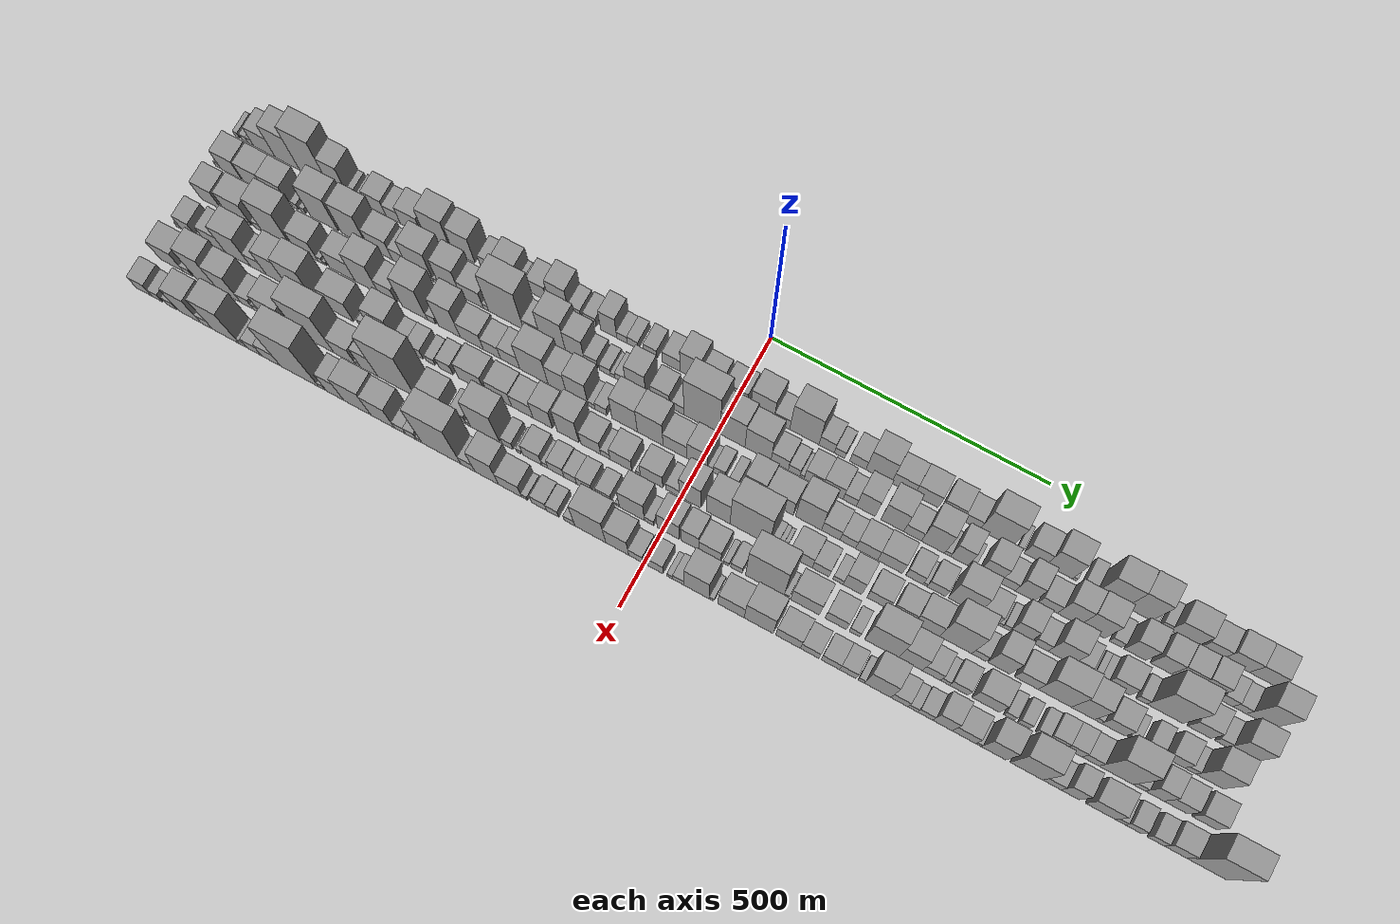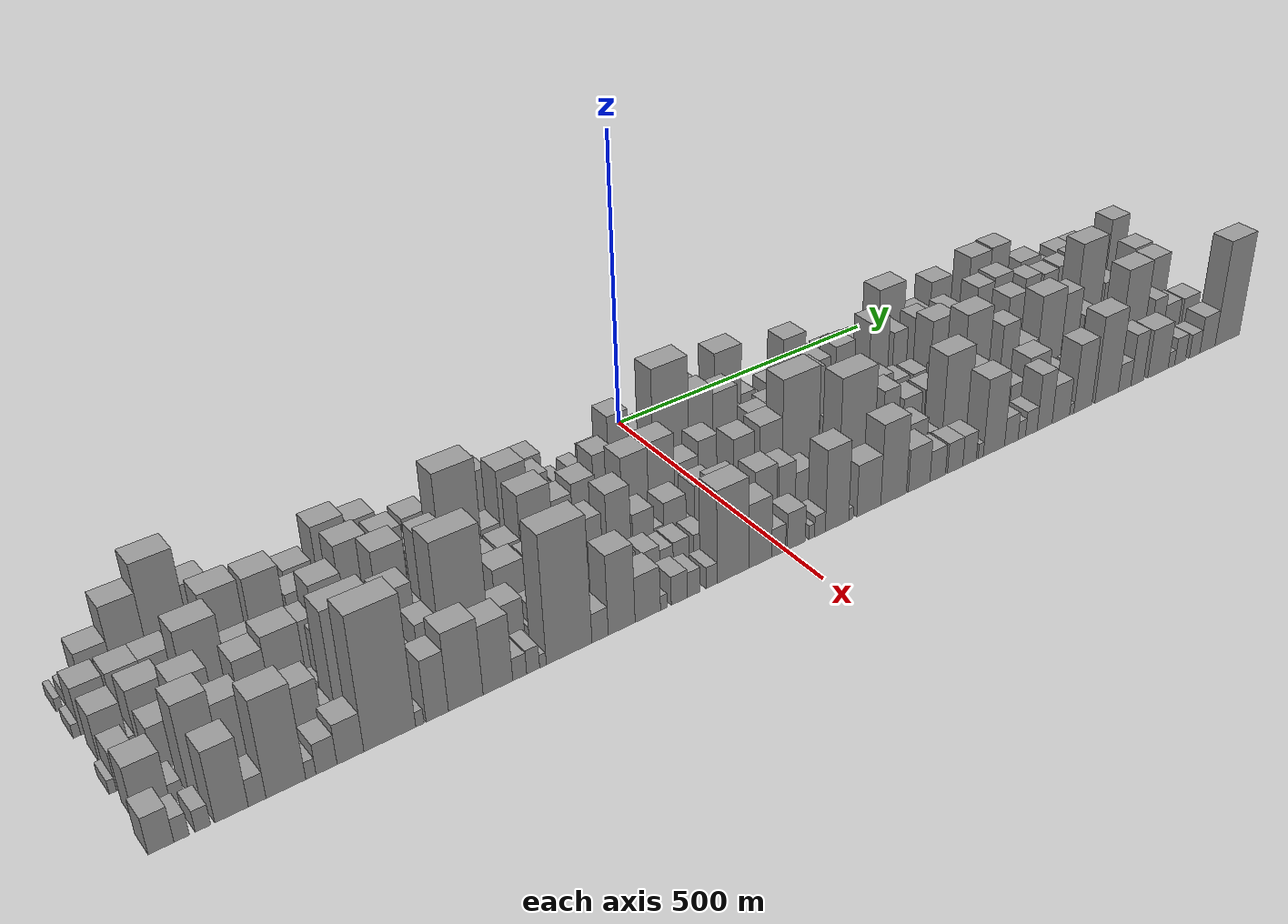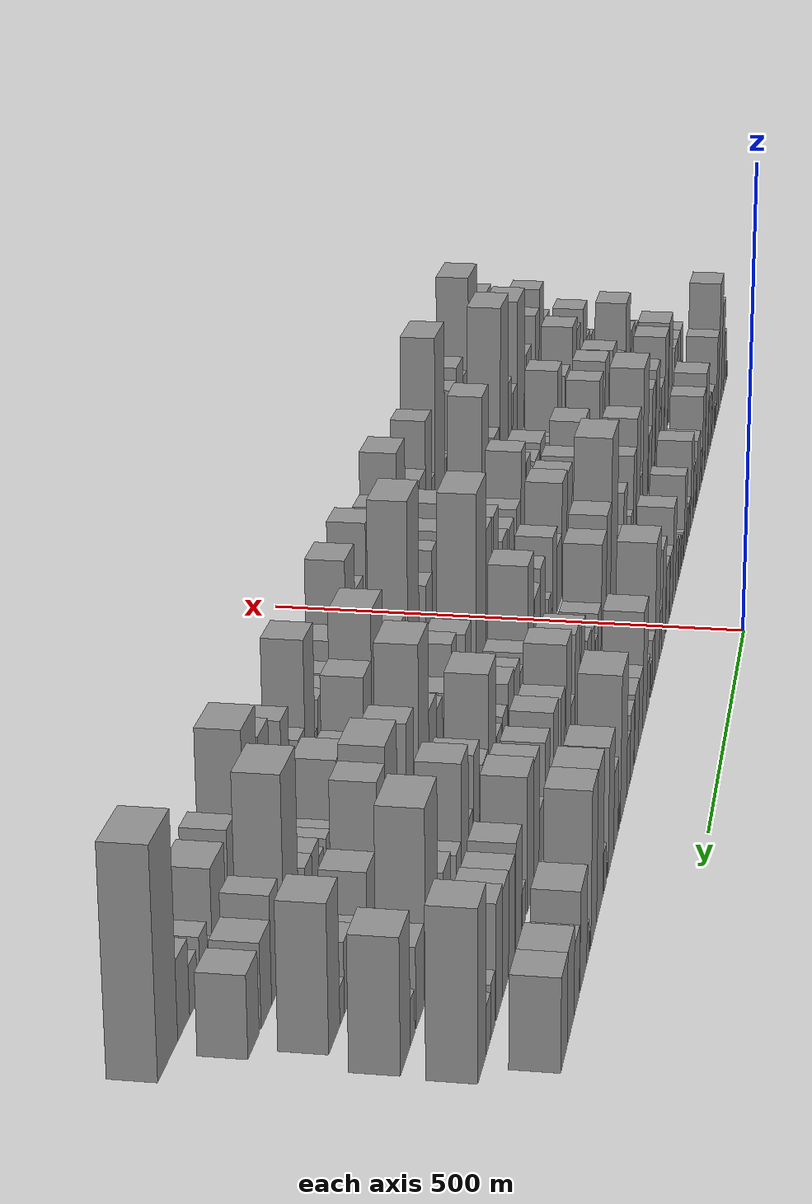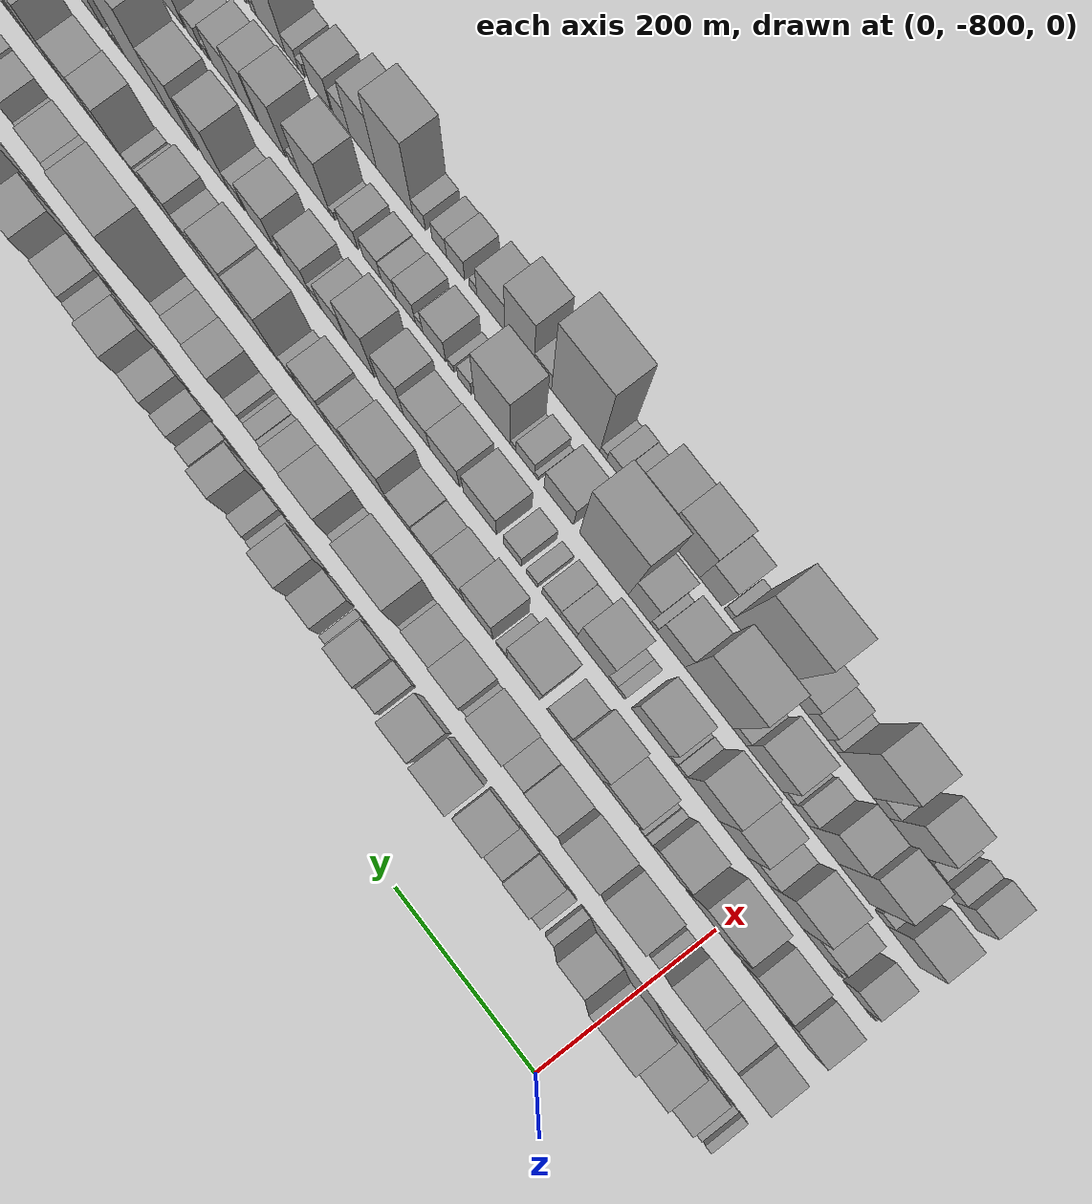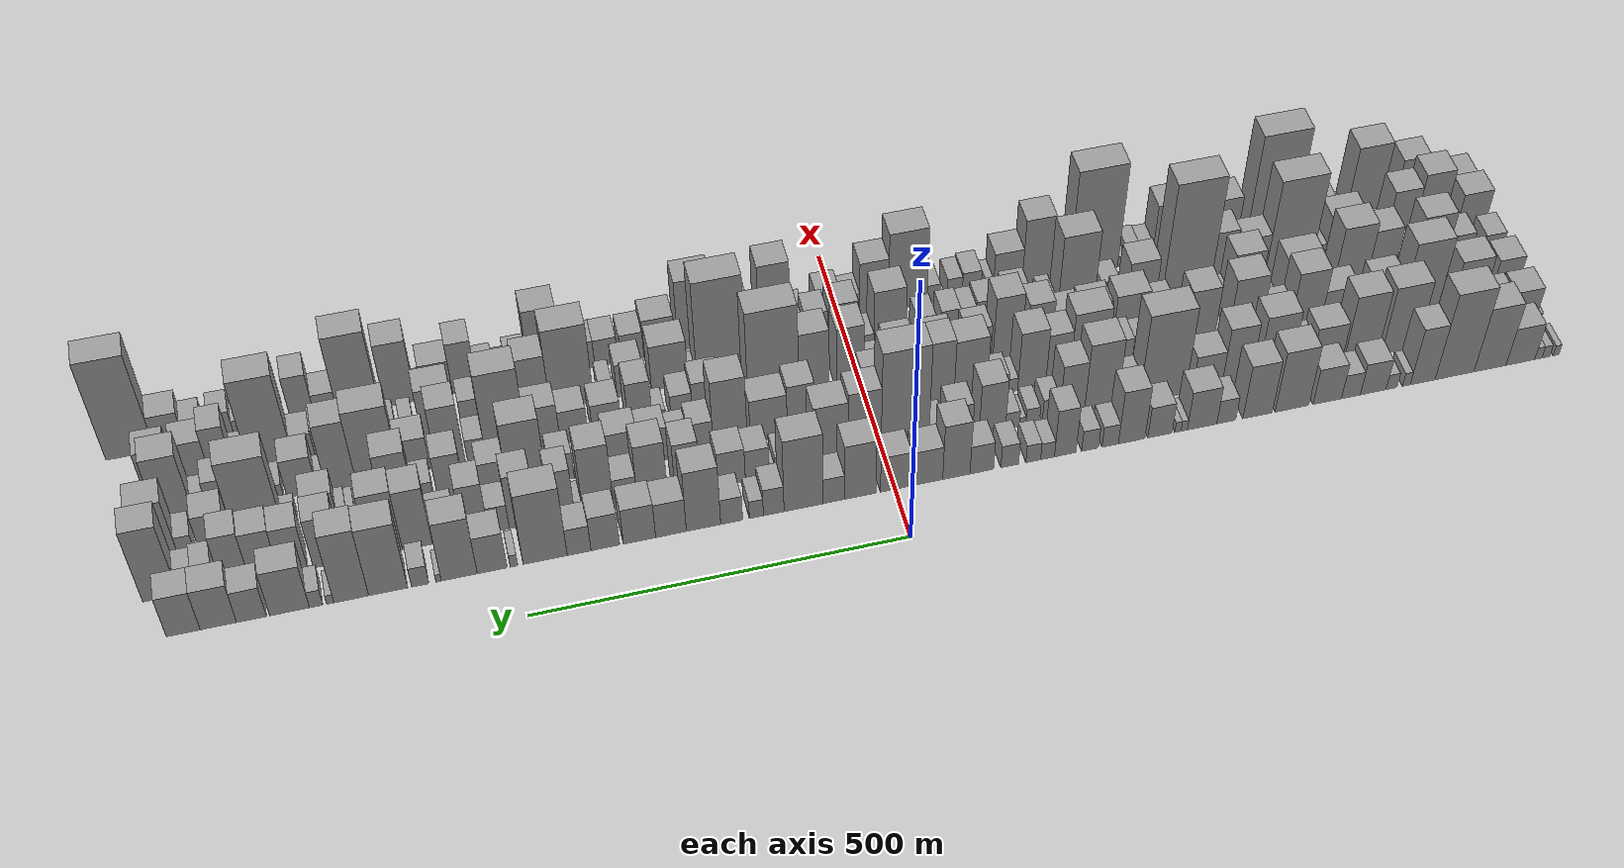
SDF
<sdf version="1.6">
 <world name="default">
  <scene>
   <sky><clouds><speed>12</speed></clouds></sky>
   <ambient>0.4 0.4 0.4 1</ambient>
   <background>0.7 0.7 0.7 1</background>
   <shadows>1</shadows>
  </scene>
  <gravity>0 0 -9.8066</gravity>
  <magnetic_field>6e-06 2.3e-05 -4.2e-05</magnetic_field>
  <physics default="0" name="default_physics" type="ode">
   <ode>
    <solver>
     <type>quick</type>
     <iters>10</iters>
     <sor>1.0</sor>
     <use_dynamic_moi_rescaling>0</use_dynamic_moi_rescaling>
    </solver>
    <constraints>
     <cfm>0</cfm>
     <erp>0.2</erp>
     <contact_max_correcting_vel>100</contact_max_correcting_vel>
     <contact_surface_layer>0.001</contact_surface_layer>
    </constraints>
   </ode>
   <max_step_size>0.004</max_step_size>
   <real_time_factor>1</real_time_factor>
   <real_time_update_rate>250</real_time_update_rate>
  </physics>
  <light name="sun" type="directional">
   <pose>0 0 10 0 0 0</pose>
   <diffuse>0.8 0.8 0.8 1</diffuse>
   <specular>0.2 0.2 0.2 1</specular>
   <attenuation>
    <range>1000</range>
    <constant>0.9</constant>
    <linear>0.01</linear>
    <quadratic>0.001</quadratic>
   </attenuation>
   <direction>-0.5 0.1 -0.9</direction>
  </light>
  <model name="building_1">
   <static>1</static>
   <pose>100.0000 -935.7430 0 0.000000 0.000000 0.000000</pose>
   <link name="link">
    <pose>0 0 10.50 0 0 0</pose>
    <collision name="collision"><geometry><box><size>40.0000 8.5141 21.0000</size></box></geometry></collision>
    <visual name="visual">
     <cast_shadows>0</cast_shadows>
     <geometry><box><size>40.0000 8.5141 21.0000</size></box></geometry>
     <material>
      <script>
       <uri>model://grey_wall/materials/scripts</uri>
       <uri>model://grey_wall/materials/textures</uri>
       <name>vrc/grey_wall</name>
      </script>
     </material>
    </visual>
   </link>
  </model>
  <model name="building_2">
   <static>1</static>
   <pose>100.0000 -920.8416 0 0.000000 0.000000 0.000000</pose>
   <link name="link">
    <pose>0 0 12.00 0 0 0</pose>
    <collision name="collision"><geometry><box><size>40.0000 11.2887 24.0000</size></box></geometry></collision>
    <visual name="visual">
     <cast_shadows>0</cast_shadows>
     <geometry><box><size>40.0000 11.2887 24.0000</size></box></geometry>
     <material>
      <script>
       <uri>model://grey_wall/materials/scripts</uri>
       <uri>model://grey_wall/materials/textures</uri>
       <name>vrc/grey_wall</name>
      </script>
     </material>
    </visual>
   </link>
  </model>
  <model name="building_3">
   <static>1</static>
   <pose>100.0000 -909.7827 0 0.000000 0.000000 0.000000</pose>
   <link name="link">
    <pose>0 0 12.00 0 0 0</pose>
    <collision name="collision"><geometry><box><size>40.0000 10.8289 24.0000</size></box></geometry></collision>
    <visual name="visual">
     <cast_shadows>0</cast_shadows>
     <geometry><box><size>40.0000 10.8289 24.0000</size></box></geometry>
     <material>
      <script>
       <uri>model://grey_wall/materials/scripts</uri>
       <uri>model://grey_wall/materials/textures</uri>
       <name>vrc/grey_wall</name>
      </script>
     </material>
    </visual>
   </link>
  </model>
  <model name="building_4">
   <static>1</static>
   <pose>100.0000 -883.2671 0 0.000000 0.000000 0.000000</pose>
   <link name="link">
    <pose>0 0 37.50 0 0 0</pose>
    <collision name="collision"><geometry><box><size>40.0000 42.2023 75.0000</size></box></geometry></collision>
    <visual name="visual">
     <cast_shadows>0</cast_shadows>
     <geometry><box><size>40.0000 42.2023 75.0000</size></box></geometry>
     <material>
      <script>
       <uri>model://grey_wall/materials/scripts</uri>
       <uri>model://grey_wall/materials/textures</uri>
       <name>vrc/grey_wall</name>
      </script>
     </material>
    </visual>
   </link>
  </model>
  <model name="building_5">
   <static>1</static>
   <pose>100.0000 -838.5047 0 0.000000 0.000000 0.000000</pose>
   <link name="link">
    <pose>0 0 64.50 0 0 0</pose>
    <collision name="collision"><geometry><box><size>40.0000 47.3226 129.0000</size></box></geometry></collision>
    <visual name="visual">
     <cast_shadows>0</cast_shadows>
     <geometry><box><size>40.0000 47.3226 129.0000</size></box></geometry>
     <material>
      <script>
       <uri>model://grey_wall/materials/scripts</uri>
       <uri>model://grey_wall/materials/textures</uri>
       <name>vrc/grey_wall</name>
      </script>
     </material>
    </visual>
   </link>
  </model>
  <model name="building_6">
   <static>1</static>
   <pose>100.0000 -786.4899 0 0.000000 0.000000 0.000000</pose>
   <link name="link">
    <pose>0 0 87.00 0 0 0</pose>
    <collision name="collision"><geometry><box><size>40.0000 56.7071 174.0000</size></box></geometry></collision>
    <visual name="visual">
     <cast_shadows>0</cast_shadows>
     <geometry><box><size>40.0000 56.7071 174.0000</size></box></geometry>
     <material>
      <script>
       <uri>model://grey_wall/materials/scripts</uri>
       <uri>model://grey_wall/materials/textures</uri>
       <name>vrc/grey_wall</name>
      </script>
     </material>
    </visual>
   </link>
  </model>
  <model name="building_7">
   <static>1</static>
   <pose>100.0000 -740.0152 0 0.000000 0.000000 0.000000</pose>
   <link name="link">
    <pose>0 0 57.00 0 0 0</pose>
    <collision name="collision"><geometry><box><size>40.0000 36.2424 114.0000</size></box></geometry></collision>
    <visual name="visual">
     <cast_shadows>0</cast_shadows>
     <geometry><box><size>40.0000 36.2424 114.0000</size></box></geometry>
     <material>
      <script>
       <uri>model://grey_wall/materials/scripts</uri>
       <uri>model://grey_wall/materials/textures</uri>
       <name>vrc/grey_wall</name>
      </script>
     </material>
    </visual>
   </link>
  </model>
  <model name="building_8">
   <static>1</static>
   <pose>100.0000 -716.3524 0 0.000000 0.000000 0.000000</pose>
   <link name="link">
    <pose>0 0 13.50 0 0 0</pose>
    <collision name="collision"><geometry><box><size>40.0000 11.0833 27.0000</size></box></geometry></collision>
    <visual name="visual">
     <cast_shadows>0</cast_shadows>
     <geometry><box><size>40.0000 11.0833 27.0000</size></box></geometry>
     <material>
      <script>
       <uri>model://grey_wall/materials/scripts</uri>
       <uri>model://grey_wall/materials/textures</uri>
       <name>vrc/grey_wall</name>
      </script>
     </material>
    </visual>
   </link>
  </model>
  <model name="building_9">
   <static>1</static>
   <pose>100.0000 -694.8102 0 0.000000 0.000000 0.000000</pose>
   <link name="link">
    <pose>0 0 15.00 0 0 0</pose>
    <collision name="collision"><geometry><box><size>40.0000 16.0010 30.0000</size></box></geometry></collision>
    <visual name="visual">
     <cast_shadows>0</cast_shadows>
     <geometry><box><size>40.0000 16.0010 30.0000</size></box></geometry>
     <material>
      <script>
       <uri>model://grey_wall/materials/scripts</uri>
       <uri>model://grey_wall/materials/textures</uri>
       <name>vrc/grey_wall</name>
      </script>
     </material>
    </visual>
   </link>
  </model>
  <model name="building_10">
   <static>1</static>
   <pose>100.0000 -668.3069 0 0.000000 0.000000 0.000000</pose>
   <link name="link">
    <pose>0 0 31.50 0 0 0</pose>
    <collision name="collision"><geometry><box><size>40.0000 37.0057 63.0000</size></box></geometry></collision>
    <visual name="visual">
     <cast_shadows>0</cast_shadows>
     <geometry><box><size>40.0000 37.0057 63.0000</size></box></geometry>
     <material>
      <script>
       <uri>model://grey_wall/materials/scripts</uri>
       <uri>model://grey_wall/materials/textures</uri>
       <name>vrc/grey_wall</name>
      </script>
     </material>
    </visual>
   </link>
  </model>
  <model name="building_11">
   <static>1</static>
   <pose>100.0000 -636.1477 0 0.000000 0.000000 0.000000</pose>
   <link name="link">
    <pose>0 0 24.00 0 0 0</pose>
    <collision name="collision"><geometry><box><size>40.0000 27.3127 48.0000</size></box></geometry></collision>
    <visual name="visual">
     <cast_shadows>0</cast_shadows>
     <geometry><box><size>40.0000 27.3127 48.0000</size></box></geometry>
     <material>
      <script>
       <uri>model://grey_wall/materials/scripts</uri>
       <uri>model://grey_wall/materials/textures</uri>
       <name>vrc/grey_wall</name>
      </script>
     </material>
    </visual>
   </link>
  </model>
  <model name="building_12">
   <static>1</static>
   <pose>100.0000 -602.0599 0 0.000000 0.000000 0.000000</pose>
   <link name="link">
    <pose>0 0 36.00 0 0 0</pose>
    <collision name="collision"><geometry><box><size>40.0000 40.8630 72.0000</size></box></geometry></collision>
    <visual name="visual">
     <cast_shadows>0</cast_shadows>
     <geometry><box><size>40.0000 40.8630 72.0000</size></box></geometry>
     <material>
      <script>
       <uri>model://grey_wall/materials/scripts</uri>
       <uri>model://grey_wall/materials/textures</uri>
       <name>vrc/grey_wall</name>
      </script>
     </material>
    </visual>
   </link>
  </model>
  <model name="building_13">
   <static>1</static>
   <pose>100.0000 -551.4606 0 0.000000 0.000000 0.000000</pose>
   <link name="link">
    <pose>0 0 61.50 0 0 0</pose>
    <collision name="collision"><geometry><box><size>40.0000 48.3356 123.0000</size></box></geometry></collision>
    <visual name="visual">
     <cast_shadows>0</cast_shadows>
     <geometry><box><size>40.0000 48.3356 123.0000</size></box></geometry>
     <material>
      <script>
       <uri>model://grey_wall/materials/scripts</uri>
       <uri>model://grey_wall/materials/textures</uri>
       <name>vrc/grey_wall</name>
      </script>
     </material>
    </visual>
   </link>
  </model>
  <model name="building_14">
   <static>1</static>
   <pose>100.0000 -502.3555 0 0.000000 0.000000 0.000000</pose>
   <link name="link">
    <pose>0 0 54.00 0 0 0</pose>
    <collision name="collision"><geometry><box><size>40.0000 41.8745 108.0000</size></box></geometry></collision>
    <visual name="visual">
     <cast_shadows>0</cast_shadows>
     <geometry><box><size>40.0000 41.8745 108.0000</size></box></geometry>
     <material>
      <script>
       <uri>model://grey_wall/materials/scripts</uri>
       <uri>model://grey_wall/materials/textures</uri>
       <name>vrc/grey_wall</name>
      </script>
     </material>
    </visual>
   </link>
  </model>
  <model name="building_15">
   <static>1</static>
   <pose>100.0000 -457.9913 0 0.000000 0.000000 0.000000</pose>
   <link name="link">
    <pose>0 0 24.00 0 0 0</pose>
    <collision name="collision"><geometry><box><size>40.0000 26.8540 48.0000</size></box></geometry></collision>
    <visual name="visual">
     <cast_shadows>0</cast_shadows>
     <geometry><box><size>40.0000 26.8540 48.0000</size></box></geometry>
     <material>
      <script>
       <uri>model://grey_wall/materials/scripts</uri>
       <uri>model://grey_wall/materials/textures</uri>
       <name>vrc/grey_wall</name>
      </script>
     </material>
    </visual>
   </link>
  </model>
  <model name="building_16">
   <static>1</static>
   <pose>100.0000 -423.7549 0 0.000000 0.000000 0.000000</pose>
   <link name="link">
    <pose>0 0 39.00 0 0 0</pose>
    <collision name="collision"><geometry><box><size>40.0000 41.6187 78.0000</size></box></geometry></collision>
    <visual name="visual">
     <cast_shadows>0</cast_shadows>
     <geometry><box><size>40.0000 41.6187 78.0000</size></box></geometry>
     <material>
      <script>
       <uri>model://grey_wall/materials/scripts</uri>
       <uri>model://grey_wall/materials/textures</uri>
       <name>vrc/grey_wall</name>
      </script>
     </material>
    </visual>
   </link>
  </model>
  <model name="building_17">
   <static>1</static>
   <pose>100.0000 -398.5500 0 0.000000 0.000000 0.000000</pose>
   <link name="link">
    <pose>0 0 10.50 0 0 0</pose>
    <collision name="collision"><geometry><box><size>40.0000 8.7912 21.0000</size></box></geometry></collision>
    <visual name="visual">
     <cast_shadows>0</cast_shadows>
     <geometry><box><size>40.0000 8.7912 21.0000</size></box></geometry>
     <material>
      <script>
       <uri>model://grey_wall/materials/scripts</uri>
       <uri>model://grey_wall/materials/textures</uri>
       <name>vrc/grey_wall</name>
      </script>
     </material>
    </visual>
   </link>
  </model>
  <model name="building_18">
   <static>1</static>
   <pose>100.0000 -389.7173 0 0.000000 0.000000 0.000000</pose>
   <link name="link">
    <pose>0 0 10.50 0 0 0</pose>
    <collision name="collision"><geometry><box><size>40.0000 8.8742 21.0000</size></box></geometry></collision>
    <visual name="visual">
     <cast_shadows>0</cast_shadows>
     <geometry><box><size>40.0000 8.8742 21.0000</size></box></geometry>
     <material>
      <script>
       <uri>model://grey_wall/materials/scripts</uri>
       <uri>model://grey_wall/materials/textures</uri>
       <name>vrc/grey_wall</name>
      </script>
     </material>
    </visual>
   </link>
  </model>
  <model name="building_19">
   <static>1</static>
   <pose>100.0000 -364.3057 0 0.000000 0.000000 0.000000</pose>
   <link name="link">
    <pose>0 0 31.50 0 0 0</pose>
    <collision name="collision"><geometry><box><size>40.0000 33.9490 63.0000</size></box></geometry></collision>
    <visual name="visual">
     <cast_shadows>0</cast_shadows>
     <geometry><box><size>40.0000 33.9490 63.0000</size></box></geometry>
     <material>
      <script>
       <uri>model://grey_wall/materials/scripts</uri>
       <uri>model://grey_wall/materials/textures</uri>
       <name>vrc/grey_wall</name>
      </script>
     </material>
    </visual>
   </link>
  </model>
  <model name="building_20">
   <static>1</static>
   <pose>100.0000 -324.7479 0 0.000000 0.000000 0.000000</pose>
   <link name="link">
    <pose>0 0 54.00 0 0 0</pose>
    <collision name="collision"><geometry><box><size>40.0000 37.1666 108.0000</size></box></geometry></collision>
    <visual name="visual">
     <cast_shadows>0</cast_shadows>
     <geometry><box><size>40.0000 37.1666 108.0000</size></box></geometry>
     <material>
      <script>
       <uri>model://grey_wall/materials/scripts</uri>
       <uri>model://grey_wall/materials/textures</uri>
       <name>vrc/grey_wall</name>
      </script>
     </material>
    </visual>
   </link>
  </model>
  <model name="building_21">
   <static>1</static>
   <pose>100.0000 -294.7719 0 0.000000 0.000000 0.000000</pose>
   <link name="link">
    <pose>0 0 21.00 0 0 0</pose>
    <collision name="collision"><geometry><box><size>40.0000 22.7853 42.0000</size></box></geometry></collision>
    <visual name="visual">
     <cast_shadows>0</cast_shadows>
     <geometry><box><size>40.0000 22.7853 42.0000</size></box></geometry>
     <material>
      <script>
       <uri>model://grey_wall/materials/scripts</uri>
       <uri>model://grey_wall/materials/textures</uri>
       <name>vrc/grey_wall</name>
      </script>
     </material>
    </visual>
   </link>
  </model>
  <model name="building_22">
   <static>1</static>
   <pose>100.0000 -266.7475 0 0.000000 0.000000 0.000000</pose>
   <link name="link">
    <pose>0 0 21.00 0 0 0</pose>
    <collision name="collision"><geometry><box><size>40.0000 23.2634 42.0000</size></box></geometry></collision>
    <visual name="visual">
     <cast_shadows>0</cast_shadows>
     <geometry><box><size>40.0000 23.2634 42.0000</size></box></geometry>
     <material>
      <script>
       <uri>model://grey_wall/materials/scripts</uri>
       <uri>model://grey_wall/materials/textures</uri>
       <name>vrc/grey_wall</name>
      </script>
     </material>
    </visual>
   </link>
  </model>
  <model name="building_23">
   <static>1</static>
   <pose>100.0000 -232.1879 0 0.000000 0.000000 0.000000</pose>
   <link name="link">
    <pose>0 0 48.00 0 0 0</pose>
    <collision name="collision"><geometry><box><size>40.0000 29.8558 96.0000</size></box></geometry></collision>
    <visual name="visual">
     <cast_shadows>0</cast_shadows>
     <geometry><box><size>40.0000 29.8558 96.0000</size></box></geometry>
     <material>
      <script>
       <uri>model://grey_wall/materials/scripts</uri>
       <uri>model://grey_wall/materials/textures</uri>
       <name>vrc/grey_wall</name>
      </script>
     </material>
    </visual>
   </link>
  </model>
  <model name="building_24">
   <static>1</static>
   <pose>100.0000 -207.7419 0 0.000000 0.000000 0.000000</pose>
   <link name="link">
    <pose>0 0 16.50 0 0 0</pose>
    <collision name="collision"><geometry><box><size>40.0000 19.0362 33.0000</size></box></geometry></collision>
    <visual name="visual">
     <cast_shadows>0</cast_shadows>
     <geometry><box><size>40.0000 19.0362 33.0000</size></box></geometry>
     <material>
      <script>
       <uri>model://grey_wall/materials/scripts</uri>
       <uri>model://grey_wall/materials/textures</uri>
       <name>vrc/grey_wall</name>
      </script>
     </material>
    </visual>
   </link>
  </model>
  <model name="building_25">
   <static>1</static>
   <pose>100.0000 -188.0473 0 0.000000 0.000000 0.000000</pose>
   <link name="link">
    <pose>0 0 18.00 0 0 0</pose>
    <collision name="collision"><geometry><box><size>40.0000 20.3529 36.0000</size></box></geometry></collision>
    <visual name="visual">
     <cast_shadows>0</cast_shadows>
     <geometry><box><size>40.0000 20.3529 36.0000</size></box></geometry>
     <material>
      <script>
       <uri>model://grey_wall/materials/scripts</uri>
       <uri>model://grey_wall/materials/textures</uri>
       <name>vrc/grey_wall</name>
      </script>
     </material>
    </visual>
   </link>
  </model>
  <model name="building_26">
   <static>1</static>
   <pose>100.0000 -155.6790 0 0.000000 0.000000 0.000000</pose>
   <link name="link">
    <pose>0 0 22.50 0 0 0</pose>
    <collision name="collision"><geometry><box><size>40.0000 24.3837 45.0000</size></box></geometry></collision>
    <visual name="visual">
     <cast_shadows>0</cast_shadows>
     <geometry><box><size>40.0000 24.3837 45.0000</size></box></geometry>
     <material>
      <script>
       <uri>model://grey_wall/materials/scripts</uri>
       <uri>model://grey_wall/materials/textures</uri>
       <name>vrc/grey_wall</name>
      </script>
     </material>
    </visual>
   </link>
  </model>
  <model name="building_27">
   <static>1</static>
   <pose>100.0000 -117.2809 0 0.000000 0.000000 0.000000</pose>
   <link name="link">
    <pose>0 0 28.50 0 0 0</pose>
    <collision name="collision"><geometry><box><size>40.0000 32.4126 57.0000</size></box></geometry></collision>
    <visual name="visual">
     <cast_shadows>0</cast_shadows>
     <geometry><box><size>40.0000 32.4126 57.0000</size></box></geometry>
     <material>
      <script>
       <uri>model://grey_wall/materials/scripts</uri>
       <uri>model://grey_wall/materials/textures</uri>
       <name>vrc/grey_wall</name>
      </script>
     </material>
    </visual>
   </link>
  </model>
  <model name="building_28">
   <static>1</static>
   <pose>100.0000 -82.4573 0 0.000000 0.000000 0.000000</pose>
   <link name="link">
    <pose>0 0 55.50 0 0 0</pose>
    <collision name="collision"><geometry><box><size>40.0000 37.2345 111.0000</size></box></geometry></collision>
    <visual name="visual">
     <cast_shadows>0</cast_shadows>
     <geometry><box><size>40.0000 37.2345 111.0000</size></box></geometry>
     <material>
      <script>
       <uri>model://grey_wall/materials/scripts</uri>
       <uri>model://grey_wall/materials/textures</uri>
       <name>vrc/grey_wall</name>
      </script>
     </material>
    </visual>
   </link>
  </model>
  <model name="building_29">
   <static>1</static>
   <pose>100.0000 -44.9028 0 0.000000 0.000000 0.000000</pose>
   <link name="link">
    <pose>0 0 34.50 0 0 0</pose>
    <collision name="collision"><geometry><box><size>40.0000 37.8745 69.0000</size></box></geometry></collision>
    <visual name="visual">
     <cast_shadows>0</cast_shadows>
     <geometry><box><size>40.0000 37.8745 69.0000</size></box></geometry>
     <material>
      <script>
       <uri>model://grey_wall/materials/scripts</uri>
       <uri>model://grey_wall/materials/textures</uri>
       <name>vrc/grey_wall</name>
      </script>
     </material>
    </visual>
   </link>
  </model>
  <model name="building_30">
   <static>1</static>
   <pose>100.0000 -0.0820 0 0.000000 0.000000 0.000000</pose>
   <link name="link">
    <pose>0 0 36.00 0 0 0</pose>
    <collision name="collision"><geometry><box><size>40.0000 41.7672 72.0000</size></box></geometry></collision>
    <visual name="visual">
     <cast_shadows>0</cast_shadows>
     <geometry><box><size>40.0000 41.7672 72.0000</size></box></geometry>
     <material>
      <script>
       <uri>model://grey_wall/materials/scripts</uri>
       <uri>model://grey_wall/materials/textures</uri>
       <name>vrc/grey_wall</name>
      </script>
     </material>
    </visual>
   </link>
  </model>
  <model name="building_31">
   <static>1</static>
   <pose>100.0000 47.9381 0 0.000000 0.000000 0.000000</pose>
   <link name="link">
    <pose>0 0 55.50 0 0 0</pose>
    <collision name="collision"><geometry><box><size>40.0000 42.2730 111.0000</size></box></geometry></collision>
    <visual name="visual">
     <cast_shadows>0</cast_shadows>
     <geometry><box><size>40.0000 42.2730 111.0000</size></box></geometry>
     <material>
      <script>
       <uri>model://grey_wall/materials/scripts</uri>
       <uri>model://grey_wall/materials/textures</uri>
       <name>vrc/grey_wall</name>
      </script>
     </material>
    </visual>
   </link>
  </model>
  <model name="building_32">
   <static>1</static>
   <pose>100.0000 83.3769 0 0.000000 0.000000 0.000000</pose>
   <link name="link">
    <pose>0 0 25.50 0 0 0</pose>
    <collision name="collision"><geometry><box><size>40.0000 28.6046 51.0000</size></box></geometry></collision>
    <visual name="visual">
     <cast_shadows>0</cast_shadows>
     <geometry><box><size>40.0000 28.6046 51.0000</size></box></geometry>
     <material>
      <script>
       <uri>model://grey_wall/materials/scripts</uri>
       <uri>model://grey_wall/materials/textures</uri>
       <name>vrc/grey_wall</name>
      </script>
     </material>
    </visual>
   </link>
  </model>
  <model name="building_33">
   <static>1</static>
   <pose>100.0000 124.0069 0 0.000000 0.000000 0.000000</pose>
   <link name="link">
    <pose>0 0 73.50 0 0 0</pose>
    <collision name="collision"><geometry><box><size>40.0000 52.6554 147.0000</size></box></geometry></collision>
    <visual name="visual">
     <cast_shadows>0</cast_shadows>
     <geometry><box><size>40.0000 52.6554 147.0000</size></box></geometry>
     <material>
      <script>
       <uri>model://grey_wall/materials/scripts</uri>
       <uri>model://grey_wall/materials/textures</uri>
       <name>vrc/grey_wall</name>
      </script>
     </material>
    </visual>
   </link>
  </model>
  <model name="building_34">
   <static>1</static>
   <pose>100.0000 164.1204 0 0.000000 0.000000 0.000000</pose>
   <link name="link">
    <pose>0 0 27.00 0 0 0</pose>
    <collision name="collision"><geometry><box><size>40.0000 27.5714 54.0000</size></box></geometry></collision>
    <visual name="visual">
     <cast_shadows>0</cast_shadows>
     <geometry><box><size>40.0000 27.5714 54.0000</size></box></geometry>
     <material>
      <script>
       <uri>model://grey_wall/materials/scripts</uri>
       <uri>model://grey_wall/materials/textures</uri>
       <name>vrc/grey_wall</name>
      </script>
     </material>
    </visual>
   </link>
  </model>
  <model name="building_35">
   <static>1</static>
   <pose>100.0000 187.2246 0 0.000000 0.000000 0.000000</pose>
   <link name="link">
    <pose>0 0 18.00 0 0 0</pose>
    <collision name="collision"><geometry><box><size>40.0000 18.6371 36.0000</size></box></geometry></collision>
    <visual name="visual">
     <cast_shadows>0</cast_shadows>
     <geometry><box><size>40.0000 18.6371 36.0000</size></box></geometry>
     <material>
      <script>
       <uri>model://grey_wall/materials/scripts</uri>
       <uri>model://grey_wall/materials/textures</uri>
       <name>vrc/grey_wall</name>
      </script>
     </material>
    </visual>
   </link>
  </model>
  <model name="building_36">
   <static>1</static>
   <pose>100.0000 220.0283 0 0.000000 0.000000 0.000000</pose>
   <link name="link">
    <pose>0 0 25.50 0 0 0</pose>
    <collision name="collision"><geometry><box><size>40.0000 28.9701 51.0000</size></box></geometry></collision>
    <visual name="visual">
     <cast_shadows>0</cast_shadows>
     <geometry><box><size>40.0000 28.9701 51.0000</size></box></geometry>
     <material>
      <script>
       <uri>model://grey_wall/materials/scripts</uri>
       <uri>model://grey_wall/materials/textures</uri>
       <name>vrc/grey_wall</name>
      </script>
     </material>
    </visual>
   </link>
  </model>
  <model name="building_37">
   <static>1</static>
   <pose>100.0000 257.2133 0 0.000000 0.000000 0.000000</pose>
   <link name="link">
    <pose>0 0 61.50 0 0 0</pose>
    <collision name="collision"><geometry><box><size>40.0000 45.3998 123.0000</size></box></geometry></collision>
    <visual name="visual">
     <cast_shadows>0</cast_shadows>
     <geometry><box><size>40.0000 45.3998 123.0000</size></box></geometry>
     <material>
      <script>
       <uri>model://grey_wall/materials/scripts</uri>
       <uri>model://grey_wall/materials/textures</uri>
       <name>vrc/grey_wall</name>
      </script>
     </material>
    </visual>
   </link>
  </model>
  <model name="building_38">
   <static>1</static>
   <pose>100.0000 300.1819 0 0.000000 0.000000 0.000000</pose>
   <link name="link">
    <pose>0 0 34.50 0 0 0</pose>
    <collision name="collision"><geometry><box><size>40.0000 40.5374 69.0000</size></box></geometry></collision>
    <visual name="visual">
     <cast_shadows>0</cast_shadows>
     <geometry><box><size>40.0000 40.5374 69.0000</size></box></geometry>
     <material>
      <script>
       <uri>model://grey_wall/materials/scripts</uri>
       <uri>model://grey_wall/materials/textures</uri>
       <name>vrc/grey_wall</name>
      </script>
     </material>
    </visual>
   </link>
  </model>
  <model name="building_39">
   <static>1</static>
   <pose>100.0000 341.5283 0 0.000000 0.000000 0.000000</pose>
   <link name="link">
    <pose>0 0 36.00 0 0 0</pose>
    <collision name="collision"><geometry><box><size>40.0000 42.1555 72.0000</size></box></geometry></collision>
    <visual name="visual">
     <cast_shadows>0</cast_shadows>
     <geometry><box><size>40.0000 42.1555 72.0000</size></box></geometry>
     <material>
      <script>
       <uri>model://grey_wall/materials/scripts</uri>
       <uri>model://grey_wall/materials/textures</uri>
       <name>vrc/grey_wall</name>
      </script>
     </material>
    </visual>
   </link>
  </model>
  <model name="building_40">
   <static>1</static>
   <pose>100.0000 386.2594 0 0.000000 0.000000 0.000000</pose>
   <link name="link">
    <pose>0 0 34.50 0 0 0</pose>
    <collision name="collision"><geometry><box><size>40.0000 37.3066 69.0000</size></box></geometry></collision>
    <visual name="visual">
     <cast_shadows>0</cast_shadows>
     <geometry><box><size>40.0000 37.3066 69.0000</size></box></geometry>
     <material>
      <script>
       <uri>model://grey_wall/materials/scripts</uri>
       <uri>model://grey_wall/materials/textures</uri>
       <name>vrc/grey_wall</name>
      </script>
     </material>
    </visual>
   </link>
  </model>
  <model name="building_41">
   <static>1</static>
   <pose>100.0000 420.3842 0 0.000000 0.000000 0.000000</pose>
   <link name="link">
    <pose>0 0 27.00 0 0 0</pose>
    <collision name="collision"><geometry><box><size>40.0000 30.9430 54.0000</size></box></geometry></collision>
    <visual name="visual">
     <cast_shadows>0</cast_shadows>
     <geometry><box><size>40.0000 30.9430 54.0000</size></box></geometry>
     <material>
      <script>
       <uri>model://grey_wall/materials/scripts</uri>
       <uri>model://grey_wall/materials/textures</uri>
       <name>vrc/grey_wall</name>
      </script>
     </material>
    </visual>
   </link>
  </model>
  <model name="building_42">
   <static>1</static>
   <pose>100.0000 464.3916 0 0.000000 0.000000 0.000000</pose>
   <link name="link">
    <pose>0 0 72.00 0 0 0</pose>
    <collision name="collision"><geometry><box><size>40.0000 57.0718 144.0000</size></box></geometry></collision>
    <visual name="visual">
     <cast_shadows>0</cast_shadows>
     <geometry><box><size>40.0000 57.0718 144.0000</size></box></geometry>
     <material>
      <script>
       <uri>model://grey_wall/materials/scripts</uri>
       <uri>model://grey_wall/materials/textures</uri>
       <name>vrc/grey_wall</name>
      </script>
     </material>
    </visual>
   </link>
  </model>
  <model name="building_43">
   <static>1</static>
   <pose>100.0000 504.8027 0 0.000000 0.000000 0.000000</pose>
   <link name="link">
    <pose>0 0 12.00 0 0 0</pose>
    <collision name="collision"><geometry><box><size>40.0000 9.7504 24.0000</size></box></geometry></collision>
    <visual name="visual">
     <cast_shadows>0</cast_shadows>
     <geometry><box><size>40.0000 9.7504 24.0000</size></box></geometry>
     <material>
      <script>
       <uri>model://grey_wall/materials/scripts</uri>
       <uri>model://grey_wall/materials/textures</uri>
       <name>vrc/grey_wall</name>
      </script>
     </material>
    </visual>
   </link>
  </model>
  <model name="building_44">
   <static>1</static>
   <pose>100.0000 532.8715 0 0.000000 0.000000 0.000000</pose>
   <link name="link">
    <pose>0 0 37.50 0 0 0</pose>
    <collision name="collision"><geometry><box><size>40.0000 38.3871 75.0000</size></box></geometry></collision>
    <visual name="visual">
     <cast_shadows>0</cast_shadows>
     <geometry><box><size>40.0000 38.3871 75.0000</size></box></geometry>
     <material>
      <script>
       <uri>model://grey_wall/materials/scripts</uri>
       <uri>model://grey_wall/materials/textures</uri>
       <name>vrc/grey_wall</name>
      </script>
     </material>
    </visual>
   </link>
  </model>
  <model name="building_45">
   <static>1</static>
   <pose>100.0000 575.0505 0 0.000000 0.000000 0.000000</pose>
   <link name="link">
    <pose>0 0 60.00 0 0 0</pose>
    <collision name="collision"><geometry><box><size>40.0000 45.9709 120.0000</size></box></geometry></collision>
    <visual name="visual">
     <cast_shadows>0</cast_shadows>
     <geometry><box><size>40.0000 45.9709 120.0000</size></box></geometry>
     <material>
      <script>
       <uri>model://grey_wall/materials/scripts</uri>
       <uri>model://grey_wall/materials/textures</uri>
       <name>vrc/grey_wall</name>
      </script>
     </material>
    </visual>
   </link>
  </model>
  <model name="building_46">
   <static>1</static>
   <pose>100.0000 601.5586 0 0.000000 0.000000 0.000000</pose>
   <link name="link">
    <pose>0 0 7.50 0 0 0</pose>
    <collision name="collision"><geometry><box><size>40.0000 7.0453 15.0000</size></box></geometry></collision>
    <visual name="visual">
     <cast_shadows>0</cast_shadows>
     <geometry><box><size>40.0000 7.0453 15.0000</size></box></geometry>
     <material>
      <script>
       <uri>model://grey_wall/materials/scripts</uri>
       <uri>model://grey_wall/materials/textures</uri>
       <name>vrc/grey_wall</name>
      </script>
     </material>
    </visual>
   </link>
  </model>
  <model name="building_47">
   <static>1</static>
   <pose>100.0000 625.0130 0 0.000000 0.000000 0.000000</pose>
   <link name="link">
    <pose>0 0 19.50 0 0 0</pose>
    <collision name="collision"><geometry><box><size>40.0000 21.8635 39.0000</size></box></geometry></collision>
    <visual name="visual">
     <cast_shadows>0</cast_shadows>
     <geometry><box><size>40.0000 21.8635 39.0000</size></box></geometry>
     <material>
      <script>
       <uri>model://grey_wall/materials/scripts</uri>
       <uri>model://grey_wall/materials/textures</uri>
       <name>vrc/grey_wall</name>
      </script>
     </material>
    </visual>
   </link>
  </model>
  <model name="building_48">
   <static>1</static>
   <pose>100.0000 665.7464 0 0.000000 0.000000 0.000000</pose>
   <link name="link">
    <pose>0 0 69.00 0 0 0</pose>
    <collision name="collision"><geometry><box><size>40.0000 49.6033 138.0000</size></box></geometry></collision>
    <visual name="visual">
     <cast_shadows>0</cast_shadows>
     <geometry><box><size>40.0000 49.6033 138.0000</size></box></geometry>
     <material>
      <script>
       <uri>model://grey_wall/materials/scripts</uri>
       <uri>model://grey_wall/materials/textures</uri>
       <name>vrc/grey_wall</name>
      </script>
     </material>
    </visual>
   </link>
  </model>
  <model name="building_49">
   <static>1</static>
   <pose>100.0000 712.5473 0 0.000000 0.000000 0.000000</pose>
   <link name="link">
    <pose>0 0 70.50 0 0 0</pose>
    <collision name="collision"><geometry><box><size>40.0000 43.9984 141.0000</size></box></geometry></collision>
    <visual name="visual">
     <cast_shadows>0</cast_shadows>
     <geometry><box><size>40.0000 43.9984 141.0000</size></box></geometry>
     <material>
      <script>
       <uri>model://grey_wall/materials/scripts</uri>
       <uri>model://grey_wall/materials/textures</uri>
       <name>vrc/grey_wall</name>
      </script>
     </material>
    </visual>
   </link>
  </model>
  <model name="building_50">
   <static>1</static>
   <pose>100.0000 739.0284 0 0.000000 0.000000 0.000000</pose>
   <link name="link">
    <pose>0 0 9.00 0 0 0</pose>
    <collision name="collision"><geometry><box><size>40.0000 8.9638 18.0000</size></box></geometry></collision>
    <visual name="visual">
     <cast_shadows>0</cast_shadows>
     <geometry><box><size>40.0000 8.9638 18.0000</size></box></geometry>
     <material>
      <script>
       <uri>model://grey_wall/materials/scripts</uri>
       <uri>model://grey_wall/materials/textures</uri>
       <name>vrc/grey_wall</name>
      </script>
     </material>
    </visual>
   </link>
  </model>
  <model name="building_51">
   <static>1</static>
   <pose>100.0000 756.8381 0 0.000000 0.000000 0.000000</pose>
   <link name="link">
    <pose>0 0 16.50 0 0 0</pose>
    <collision name="collision"><geometry><box><size>40.0000 16.6556 33.0000</size></box></geometry></collision>
    <visual name="visual">
     <cast_shadows>0</cast_shadows>
     <geometry><box><size>40.0000 16.6556 33.0000</size></box></geometry>
     <material>
      <script>
       <uri>model://grey_wall/materials/scripts</uri>
       <uri>model://grey_wall/materials/textures</uri>
       <name>vrc/grey_wall</name>
      </script>
     </material>
    </visual>
   </link>
  </model>
  <model name="building_52">
   <static>1</static>
   <pose>100.0000 790.1409 0 0.000000 0.000000 0.000000</pose>
   <link name="link">
    <pose>0 0 45.00 0 0 0</pose>
    <collision name="collision"><geometry><box><size>40.0000 49.9500 90.0000</size></box></geometry></collision>
    <visual name="visual">
     <cast_shadows>0</cast_shadows>
     <geometry><box><size>40.0000 49.9500 90.0000</size></box></geometry>
     <material>
      <script>
       <uri>model://grey_wall/materials/scripts</uri>
       <uri>model://grey_wall/materials/textures</uri>
       <name>vrc/grey_wall</name>
      </script>
     </material>
    </visual>
   </link>
  </model>
  <model name="building_53">
   <static>1</static>
   <pose>100.0000 837.7092 0 0.000000 0.000000 0.000000</pose>
   <link name="link">
    <pose>0 0 31.50 0 0 0</pose>
    <collision name="collision"><geometry><box><size>40.0000 37.1866 63.0000</size></box></geometry></collision>
    <visual name="visual">
     <cast_shadows>0</cast_shadows>
     <geometry><box><size>40.0000 37.1866 63.0000</size></box></geometry>
     <material>
      <script>
       <uri>model://grey_wall/materials/scripts</uri>
       <uri>model://grey_wall/materials/textures</uri>
       <name>vrc/grey_wall</name>
      </script>
     </material>
    </visual>
   </link>
  </model>
  <model name="building_54">
   <static>1</static>
   <pose>100.0000 878.9409 0 0.000000 0.000000 0.000000</pose>
   <link name="link">
    <pose>0 0 40.50 0 0 0</pose>
    <collision name="collision"><geometry><box><size>40.0000 45.2768 81.0000</size></box></geometry></collision>
    <visual name="visual">
     <cast_shadows>0</cast_shadows>
     <geometry><box><size>40.0000 45.2768 81.0000</size></box></geometry>
     <material>
      <script>
       <uri>model://grey_wall/materials/scripts</uri>
       <uri>model://grey_wall/materials/textures</uri>
       <name>vrc/grey_wall</name>
      </script>
     </material>
    </visual>
   </link>
  </model>
  <model name="building_55">
   <static>1</static>
   <pose>100.0000 922.5653 0 0.000000 0.000000 0.000000</pose>
   <link name="link">
    <pose>0 0 40.50 0 0 0</pose>
    <collision name="collision"><geometry><box><size>40.0000 41.9720 81.0000</size></box></geometry></collision>
    <visual name="visual">
     <cast_shadows>0</cast_shadows>
     <geometry><box><size>40.0000 41.9720 81.0000</size></box></geometry>
     <material>
      <script>
       <uri>model://grey_wall/materials/scripts</uri>
       <uri>model://grey_wall/materials/textures</uri>
       <name>vrc/grey_wall</name>
      </script>
     </material>
    </visual>
   </link>
  </model>
  <model name="building_56">
   <static>1</static>
   <pose>160.0000 -935.2326 0 0.000000 0.000000 0.000000</pose>
   <link name="link">
    <pose>0 0 10.50 0 0 0</pose>
    <collision name="collision"><geometry><box><size>40.0000 9.5348 21.0000</size></box></geometry></collision>
    <visual name="visual">
     <cast_shadows>0</cast_shadows>
     <geometry><box><size>40.0000 9.5348 21.0000</size></box></geometry>
     <material>
      <script>
       <uri>model://grey_wall/materials/scripts</uri>
       <uri>model://grey_wall/materials/textures</uri>
       <name>vrc/grey_wall</name>
      </script>
     </material>
    </visual>
   </link>
  </model>
  <model name="building_57">
   <static>1</static>
   <pose>160.0000 -910.1573 0 0.000000 0.000000 0.000000</pose>
   <link name="link">
    <pose>0 0 37.50 0 0 0</pose>
    <collision name="collision"><geometry><box><size>40.0000 40.6156 75.0000</size></box></geometry></collision>
    <visual name="visual">
     <cast_shadows>0</cast_shadows>
     <geometry><box><size>40.0000 40.6156 75.0000</size></box></geometry>
     <material>
      <script>
       <uri>model://grey_wall/materials/scripts</uri>
       <uri>model://grey_wall/materials/textures</uri>
       <name>vrc/grey_wall</name>
      </script>
     </material>
    </visual>
   </link>
  </model>
  <model name="building_58">
   <static>1</static>
   <pose>160.0000 -865.3514 0 0.000000 0.000000 0.000000</pose>
   <link name="link">
    <pose>0 0 37.50 0 0 0</pose>
    <collision name="collision"><geometry><box><size>40.0000 42.9962 75.0000</size></box></geometry></collision>
    <visual name="visual">
     <cast_shadows>0</cast_shadows>
     <geometry><box><size>40.0000 42.9962 75.0000</size></box></geometry>
     <material>
      <script>
       <uri>model://grey_wall/materials/scripts</uri>
       <uri>model://grey_wall/materials/textures</uri>
       <name>vrc/grey_wall</name>
      </script>
     </material>
    </visual>
   </link>
  </model>
  <model name="building_59">
   <static>1</static>
   <pose>160.0000 -821.9235 0 0.000000 0.000000 0.000000</pose>
   <link name="link">
    <pose>0 0 37.50 0 0 0</pose>
    <collision name="collision"><geometry><box><size>40.0000 43.8597 75.0000</size></box></geometry></collision>
    <visual name="visual">
     <cast_shadows>0</cast_shadows>
     <geometry><box><size>40.0000 43.8597 75.0000</size></box></geometry>
     <material>
      <script>
       <uri>model://grey_wall/materials/scripts</uri>
       <uri>model://grey_wall/materials/textures</uri>
       <name>vrc/grey_wall</name>
      </script>
     </material>
    </visual>
   </link>
  </model>
  <model name="building_60">
   <static>1</static>
   <pose>160.0000 -786.2253 0 0.000000 0.000000 0.000000</pose>
   <link name="link">
    <pose>0 0 12.00 0 0 0</pose>
    <collision name="collision"><geometry><box><size>40.0000 11.5367 24.0000</size></box></geometry></collision>
    <visual name="visual">
     <cast_shadows>0</cast_shadows>
     <geometry><box><size>40.0000 11.5367 24.0000</size></box></geometry>
     <material>
      <script>
       <uri>model://grey_wall/materials/scripts</uri>
       <uri>model://grey_wall/materials/textures</uri>
       <name>vrc/grey_wall</name>
      </script>
     </material>
    </visual>
   </link>
  </model>
  <model name="building_61">
   <static>1</static>
   <pose>160.0000 -770.8223 0 0.000000 0.000000 0.000000</pose>
   <link name="link">
    <pose>0 0 10.50 0 0 0</pose>
    <collision name="collision"><geometry><box><size>40.0000 9.2693 21.0000</size></box></geometry></collision>
    <visual name="visual">
     <cast_shadows>0</cast_shadows>
     <geometry><box><size>40.0000 9.2693 21.0000</size></box></geometry>
     <material>
      <script>
       <uri>model://grey_wall/materials/scripts</uri>
       <uri>model://grey_wall/materials/textures</uri>
       <name>vrc/grey_wall</name>
      </script>
     </material>
    </visual>
   </link>
  </model>
  <model name="building_62">
   <static>1</static>
   <pose>160.0000 -730.7916 0 0.000000 0.000000 0.000000</pose>
   <link name="link">
    <pose>0 0 67.50 0 0 0</pose>
    <collision name="collision"><geometry><box><size>40.0000 52.7921 135.0000</size></box></geometry></collision>
    <visual name="visual">
     <cast_shadows>0</cast_shadows>
     <geometry><box><size>40.0000 52.7921 135.0000</size></box></geometry>
     <material>
      <script>
       <uri>model://grey_wall/materials/scripts</uri>
       <uri>model://grey_wall/materials/textures</uri>
       <name>vrc/grey_wall</name>
      </script>
     </material>
    </visual>
   </link>
  </model>
  <model name="building_63">
   <static>1</static>
   <pose>160.0000 -673.8231 0 0.000000 0.000000 0.000000</pose>
   <link name="link">
    <pose>0 0 66.00 0 0 0</pose>
    <collision name="collision"><geometry><box><size>40.0000 49.1448 132.0000</size></box></geometry></collision>
    <visual name="visual">
     <cast_shadows>0</cast_shadows>
     <geometry><box><size>40.0000 49.1448 132.0000</size></box></geometry>
     <material>
      <script>
       <uri>model://grey_wall/materials/scripts</uri>
       <uri>model://grey_wall/materials/textures</uri>
       <name>vrc/grey_wall</name>
      </script>
     </material>
    </visual>
   </link>
  </model>
  <model name="building_64">
   <static>1</static>
   <pose>160.0000 -623.9301 0 0.000000 0.000000 0.000000</pose>
   <link name="link">
    <pose>0 0 40.50 0 0 0</pose>
    <collision name="collision"><geometry><box><size>40.0000 44.6413 81.0000</size></box></geometry></collision>
    <visual name="visual">
     <cast_shadows>0</cast_shadows>
     <geometry><box><size>40.0000 44.6413 81.0000</size></box></geometry>
     <material>
      <script>
       <uri>model://grey_wall/materials/scripts</uri>
       <uri>model://grey_wall/materials/textures</uri>
       <name>vrc/grey_wall</name>
      </script>
     </material>
    </visual>
   </link>
  </model>
  <model name="building_65">
   <static>1</static>
   <pose>160.0000 -586.8522 0 0.000000 0.000000 0.000000</pose>
   <link name="link">
    <pose>0 0 28.50 0 0 0</pose>
    <collision name="collision"><geometry><box><size>40.0000 29.5145 57.0000</size></box></geometry></collision>
    <visual name="visual">
     <cast_shadows>0</cast_shadows>
     <geometry><box><size>40.0000 29.5145 57.0000</size></box></geometry>
     <material>
      <script>
       <uri>model://grey_wall/materials/scripts</uri>
       <uri>model://grey_wall/materials/textures</uri>
       <name>vrc/grey_wall</name>
      </script>
     </material>
    </visual>
   </link>
  </model>
  <model name="building_66">
   <static>1</static>
   <pose>160.0000 -547.9017 0 0.000000 0.000000 0.000000</pose>
   <link name="link">
    <pose>0 0 63.00 0 0 0</pose>
    <collision name="collision"><geometry><box><size>40.0000 48.3866 126.0000</size></box></geometry></collision>
    <visual name="visual">
     <cast_shadows>0</cast_shadows>
     <geometry><box><size>40.0000 48.3866 126.0000</size></box></geometry>
     <material>
      <script>
       <uri>model://grey_wall/materials/scripts</uri>
       <uri>model://grey_wall/materials/textures</uri>
       <name>vrc/grey_wall</name>
      </script>
     </material>
    </visual>
   </link>
  </model>
  <model name="building_67">
   <static>1</static>
   <pose>160.0000 -519.0007 0 0.000000 0.000000 0.000000</pose>
   <link name="link">
    <pose>0 0 10.50 0 0 0</pose>
    <collision name="collision"><geometry><box><size>40.0000 9.4153 21.0000</size></box></geometry></collision>
    <visual name="visual">
     <cast_shadows>0</cast_shadows>
     <geometry><box><size>40.0000 9.4153 21.0000</size></box></geometry>
     <material>
      <script>
       <uri>model://grey_wall/materials/scripts</uri>
       <uri>model://grey_wall/materials/textures</uri>
       <name>vrc/grey_wall</name>
      </script>
     </material>
    </visual>
   </link>
  </model>
  <model name="building_68">
   <static>1</static>
   <pose>160.0000 -493.6589 0 0.000000 0.000000 0.000000</pose>
   <link name="link">
    <pose>0 0 58.50 0 0 0</pose>
    <collision name="collision"><geometry><box><size>40.0000 41.2683 117.0000</size></box></geometry></collision>
    <visual name="visual">
     <cast_shadows>0</cast_shadows>
     <geometry><box><size>40.0000 41.2683 117.0000</size></box></geometry>
     <material>
      <script>
       <uri>model://grey_wall/materials/scripts</uri>
       <uri>model://grey_wall/materials/textures</uri>
       <name>vrc/grey_wall</name>
      </script>
     </material>
    </visual>
   </link>
  </model>
  <model name="building_69">
   <static>1</static>
   <pose>160.0000 -452.0006 0 0.000000 0.000000 0.000000</pose>
   <link name="link">
    <pose>0 0 36.00 0 0 0</pose>
    <collision name="collision"><geometry><box><size>40.0000 42.0482 72.0000</size></box></geometry></collision>
    <visual name="visual">
     <cast_shadows>0</cast_shadows>
     <geometry><box><size>40.0000 42.0482 72.0000</size></box></geometry>
     <material>
      <script>
       <uri>model://grey_wall/materials/scripts</uri>
       <uri>model://grey_wall/materials/textures</uri>
       <name>vrc/grey_wall</name>
      </script>
     </material>
    </visual>
   </link>
  </model>
  <model name="building_70">
   <static>1</static>
   <pose>160.0000 -425.9590 0 0.000000 0.000000 0.000000</pose>
   <link name="link">
    <pose>0 0 12.00 0 0 0</pose>
    <collision name="collision"><geometry><box><size>40.0000 10.0351 24.0000</size></box></geometry></collision>
    <visual name="visual">
     <cast_shadows>0</cast_shadows>
     <geometry><box><size>40.0000 10.0351 24.0000</size></box></geometry>
     <material>
      <script>
       <uri>model://grey_wall/materials/scripts</uri>
       <uri>model://grey_wall/materials/textures</uri>
       <name>vrc/grey_wall</name>
      </script>
     </material>
    </visual>
   </link>
  </model>
  <model name="building_71">
   <static>1</static>
   <pose>160.0000 -388.1285 0 0.000000 0.000000 0.000000</pose>
   <link name="link">
    <pose>0 0 88.50 0 0 0</pose>
    <collision name="collision"><geometry><box><size>40.0000 65.6257 177.0000</size></box></geometry></collision>
    <visual name="visual">
     <cast_shadows>0</cast_shadows>
     <geometry><box><size>40.0000 65.6257 177.0000</size></box></geometry>
     <material>
      <script>
       <uri>model://grey_wall/materials/scripts</uri>
       <uri>model://grey_wall/materials/textures</uri>
       <name>vrc/grey_wall</name>
      </script>
     </material>
    </visual>
   </link>
  </model>
  <model name="building_72">
   <static>1</static>
   <pose>160.0000 -339.8309 0 0.000000 0.000000 0.000000</pose>
   <link name="link">
    <pose>0 0 27.00 0 0 0</pose>
    <collision name="collision"><geometry><box><size>40.0000 30.9695 54.0000</size></box></geometry></collision>
    <visual name="visual">
     <cast_shadows>0</cast_shadows>
     <geometry><box><size>40.0000 30.9695 54.0000</size></box></geometry>
     <material>
      <script>
       <uri>model://grey_wall/materials/scripts</uri>
       <uri>model://grey_wall/materials/textures</uri>
       <name>vrc/grey_wall</name>
      </script>
     </material>
    </visual>
   </link>
  </model>
  <model name="building_73">
   <static>1</static>
   <pose>160.0000 -300.9477 0 0.000000 0.000000 0.000000</pose>
   <link name="link">
    <pose>0 0 70.50 0 0 0</pose>
    <collision name="collision"><geometry><box><size>40.0000 46.7970 141.0000</size></box></geometry></collision>
    <visual name="visual">
     <cast_shadows>0</cast_shadows>
     <geometry><box><size>40.0000 46.7970 141.0000</size></box></geometry>
     <material>
      <script>
       <uri>model://grey_wall/materials/scripts</uri>
       <uri>model://grey_wall/materials/textures</uri>
       <name>vrc/grey_wall</name>
      </script>
     </material>
    </visual>
   </link>
  </model>
  <model name="building_74">
   <static>1</static>
   <pose>160.0000 -260.0227 0 0.000000 0.000000 0.000000</pose>
   <link name="link">
    <pose>0 0 54.00 0 0 0</pose>
    <collision name="collision"><geometry><box><size>40.0000 35.0530 108.0000</size></box></geometry></collision>
    <visual name="visual">
     <cast_shadows>0</cast_shadows>
     <geometry><box><size>40.0000 35.0530 108.0000</size></box></geometry>
     <material>
      <script>
       <uri>model://grey_wall/materials/scripts</uri>
       <uri>model://grey_wall/materials/textures</uri>
       <name>vrc/grey_wall</name>
      </script>
     </material>
    </visual>
   </link>
  </model>
  <model name="building_75">
   <static>1</static>
   <pose>160.0000 -230.6805 0 0.000000 0.000000 0.000000</pose>
   <link name="link">
    <pose>0 0 22.50 0 0 0</pose>
    <collision name="collision"><geometry><box><size>40.0000 23.6315 45.0000</size></box></geometry></collision>
    <visual name="visual">
     <cast_shadows>0</cast_shadows>
     <geometry><box><size>40.0000 23.6315 45.0000</size></box></geometry>
     <material>
      <script>
       <uri>model://grey_wall/materials/scripts</uri>
       <uri>model://grey_wall/materials/textures</uri>
       <name>vrc/grey_wall</name>
      </script>
     </material>
    </visual>
   </link>
  </model>
  <model name="building_76">
   <static>1</static>
   <pose>160.0000 -205.2966 0 0.000000 0.000000 0.000000</pose>
   <link name="link">
    <pose>0 0 16.50 0 0 0</pose>
    <collision name="collision"><geometry><box><size>40.0000 19.1364 33.0000</size></box></geometry></collision>
    <visual name="visual">
     <cast_shadows>0</cast_shadows>
     <geometry><box><size>40.0000 19.1364 33.0000</size></box></geometry>
     <material>
      <script>
       <uri>model://grey_wall/materials/scripts</uri>
       <uri>model://grey_wall/materials/textures</uri>
       <name>vrc/grey_wall</name>
      </script>
     </material>
    </visual>
   </link>
  </model>
  <model name="building_77">
   <static>1</static>
   <pose>160.0000 -191.3199 0 0.000000 0.000000 0.000000</pose>
   <link name="link">
    <pose>0 0 9.00 0 0 0</pose>
    <collision name="collision"><geometry><box><size>40.0000 8.8171 18.0000</size></box></geometry></collision>
    <visual name="visual">
     <cast_shadows>0</cast_shadows>
     <geometry><box><size>40.0000 8.8171 18.0000</size></box></geometry>
     <material>
      <script>
       <uri>model://grey_wall/materials/scripts</uri>
       <uri>model://grey_wall/materials/textures</uri>
       <name>vrc/grey_wall</name>
      </script>
     </material>
    </visual>
   </link>
  </model>
  <model name="building_78">
   <static>1</static>
   <pose>160.0000 -177.2058 0 0.000000 0.000000 0.000000</pose>
   <link name="link">
    <pose>0 0 16.50 0 0 0</pose>
    <collision name="collision"><geometry><box><size>40.0000 19.4111 33.0000</size></box></geometry></collision>
    <visual name="visual">
     <cast_shadows>0</cast_shadows>
     <geometry><box><size>40.0000 19.4111 33.0000</size></box></geometry>
     <material>
      <script>
       <uri>model://grey_wall/materials/scripts</uri>
       <uri>model://grey_wall/materials/textures</uri>
       <name>vrc/grey_wall</name>
      </script>
     </material>
    </visual>
   </link>
  </model>
  <model name="building_79">
   <static>1</static>
   <pose>160.0000 -149.1552 0 0.000000 0.000000 0.000000</pose>
   <link name="link">
    <pose>0 0 51.00 0 0 0</pose>
    <collision name="collision"><geometry><box><size>40.0000 36.6900 102.0000</size></box></geometry></collision>
    <visual name="visual">
     <cast_shadows>0</cast_shadows>
     <geometry><box><size>40.0000 36.6900 102.0000</size></box></geometry>
     <material>
      <script>
       <uri>model://grey_wall/materials/scripts</uri>
       <uri>model://grey_wall/materials/textures</uri>
       <name>vrc/grey_wall</name>
      </script>
     </material>
    </visual>
   </link>
  </model>
  <model name="building_80">
   <static>1</static>
   <pose>160.0000 -104.5322 0 0.000000 0.000000 0.000000</pose>
   <link name="link">
    <pose>0 0 34.50 0 0 0</pose>
    <collision name="collision"><geometry><box><size>40.0000 34.5561 69.0000</size></box></geometry></collision>
    <visual name="visual">
     <cast_shadows>0</cast_shadows>
     <geometry><box><size>40.0000 34.5561 69.0000</size></box></geometry>
     <material>
      <script>
       <uri>model://grey_wall/materials/scripts</uri>
       <uri>model://grey_wall/materials/textures</uri>
       <name>vrc/grey_wall</name>
      </script>
     </material>
    </visual>
   </link>
  </model>
  <model name="building_81">
   <static>1</static>
   <pose>160.0000 -72.2438 0 0.000000 0.000000 0.000000</pose>
   <link name="link">
    <pose>0 0 21.00 0 0 0</pose>
    <collision name="collision"><geometry><box><size>40.0000 22.0208 42.0000</size></box></geometry></collision>
    <visual name="visual">
     <cast_shadows>0</cast_shadows>
     <geometry><box><size>40.0000 22.0208 42.0000</size></box></geometry>
     <material>
      <script>
       <uri>model://grey_wall/materials/scripts</uri>
       <uri>model://grey_wall/materials/textures</uri>
       <name>vrc/grey_wall</name>
      </script>
     </material>
    </visual>
   </link>
  </model>
  <model name="building_82">
   <static>1</static>
   <pose>160.0000 -28.4740 0 0.000000 0.000000 0.000000</pose>
   <link name="link">
    <pose>0 0 103.50 0 0 0</pose>
    <collision name="collision"><geometry><box><size>40.0000 65.5187 207.0000</size></box></geometry></collision>
    <visual name="visual">
     <cast_shadows>0</cast_shadows>
     <geometry><box><size>40.0000 65.5187 207.0000</size></box></geometry>
     <material>
      <script>
       <uri>model://grey_wall/materials/scripts</uri>
       <uri>model://grey_wall/materials/textures</uri>
       <name>vrc/grey_wall</name>
      </script>
     </material>
    </visual>
   </link>
  </model>
  <model name="building_83">
   <static>1</static>
   <pose>160.0000 26.7133 0 0.000000 0.000000 0.000000</pose>
   <link name="link">
    <pose>0 0 69.00 0 0 0</pose>
    <collision name="collision"><geometry><box><size>40.0000 44.8558 138.0000</size></box></geometry></collision>
    <visual name="visual">
     <cast_shadows>0</cast_shadows>
     <geometry><box><size>40.0000 44.8558 138.0000</size></box></geometry>
     <material>
      <script>
       <uri>model://grey_wall/materials/scripts</uri>
       <uri>model://grey_wall/materials/textures</uri>
       <name>vrc/grey_wall</name>
      </script>
     </material>
    </visual>
   </link>
  </model>
  <model name="building_84">
   <static>1</static>
   <pose>160.0000 72.5643 0 0.000000 0.000000 0.000000</pose>
   <link name="link">
    <pose>0 0 61.50 0 0 0</pose>
    <collision name="collision"><geometry><box><size>40.0000 46.8463 123.0000</size></box></geometry></collision>
    <visual name="visual">
     <cast_shadows>0</cast_shadows>
     <geometry><box><size>40.0000 46.8463 123.0000</size></box></geometry>
     <material>
      <script>
       <uri>model://grey_wall/materials/scripts</uri>
       <uri>model://grey_wall/materials/textures</uri>
       <name>vrc/grey_wall</name>
      </script>
     </material>
    </visual>
   </link>
  </model>
  <model name="building_85">
   <static>1</static>
   <pose>160.0000 111.5400 0 0.000000 0.000000 0.000000</pose>
   <link name="link">
    <pose>0 0 30.00 0 0 0</pose>
    <collision name="collision"><geometry><box><size>40.0000 31.1051 60.0000</size></box></geometry></collision>
    <visual name="visual">
     <cast_shadows>0</cast_shadows>
     <geometry><box><size>40.0000 31.1051 60.0000</size></box></geometry>
     <material>
      <script>
       <uri>model://grey_wall/materials/scripts</uri>
       <uri>model://grey_wall/materials/textures</uri>
       <name>vrc/grey_wall</name>
      </script>
     </material>
    </visual>
   </link>
  </model>
  <model name="building_86">
   <static>1</static>
   <pose>160.0000 137.5677 0 0.000000 0.000000 0.000000</pose>
   <link name="link">
    <pose>0 0 19.50 0 0 0</pose>
    <collision name="collision"><geometry><box><size>40.0000 20.9502 39.0000</size></box></geometry></collision>
    <visual name="visual">
     <cast_shadows>0</cast_shadows>
     <geometry><box><size>40.0000 20.9502 39.0000</size></box></geometry>
     <material>
      <script>
       <uri>model://grey_wall/materials/scripts</uri>
       <uri>model://grey_wall/materials/textures</uri>
       <name>vrc/grey_wall</name>
      </script>
     </material>
    </visual>
   </link>
  </model>
  <model name="building_87">
   <static>1</static>
   <pose>160.0000 151.9933 0 0.000000 0.000000 0.000000</pose>
   <link name="link">
    <pose>0 0 9.00 0 0 0</pose>
    <collision name="collision"><geometry><box><size>40.0000 7.9010 18.0000</size></box></geometry></collision>
    <visual name="visual">
     <cast_shadows>0</cast_shadows>
     <geometry><box><size>40.0000 7.9010 18.0000</size></box></geometry>
     <material>
      <script>
       <uri>model://grey_wall/materials/scripts</uri>
       <uri>model://grey_wall/materials/textures</uri>
       <name>vrc/grey_wall</name>
      </script>
     </material>
    </visual>
   </link>
  </model>
  <model name="building_88">
   <static>1</static>
   <pose>160.0000 172.0946 0 0.000000 0.000000 0.000000</pose>
   <link name="link">
    <pose>0 0 31.50 0 0 0</pose>
    <collision name="collision"><geometry><box><size>40.0000 32.3016 63.0000</size></box></geometry></collision>
    <visual name="visual">
     <cast_shadows>0</cast_shadows>
     <geometry><box><size>40.0000 32.3016 63.0000</size></box></geometry>
     <material>
      <script>
       <uri>model://grey_wall/materials/scripts</uri>
       <uri>model://grey_wall/materials/textures</uri>
       <name>vrc/grey_wall</name>
      </script>
     </material>
    </visual>
   </link>
  </model>
  <model name="building_89">
   <static>1</static>
   <pose>160.0000 206.7054 0 0.000000 0.000000 0.000000</pose>
   <link name="link">
    <pose>0 0 34.50 0 0 0</pose>
    <collision name="collision"><geometry><box><size>40.0000 36.9199 69.0000</size></box></geometry></collision>
    <visual name="visual">
     <cast_shadows>0</cast_shadows>
     <geometry><box><size>40.0000 36.9199 69.0000</size></box></geometry>
     <material>
      <script>
       <uri>model://grey_wall/materials/scripts</uri>
       <uri>model://grey_wall/materials/textures</uri>
       <name>vrc/grey_wall</name>
      </script>
     </material>
    </visual>
   </link>
  </model>
  <model name="building_90">
   <static>1</static>
   <pose>160.0000 236.8410 0 0.000000 0.000000 0.000000</pose>
   <link name="link">
    <pose>0 0 22.50 0 0 0</pose>
    <collision name="collision"><geometry><box><size>40.0000 23.3513 45.0000</size></box></geometry></collision>
    <visual name="visual">
     <cast_shadows>0</cast_shadows>
     <geometry><box><size>40.0000 23.3513 45.0000</size></box></geometry>
     <material>
      <script>
       <uri>model://grey_wall/materials/scripts</uri>
       <uri>model://grey_wall/materials/textures</uri>
       <name>vrc/grey_wall</name>
      </script>
     </material>
    </visual>
   </link>
  </model>
  <model name="building_91">
   <static>1</static>
   <pose>160.0000 265.3119 0 0.000000 0.000000 0.000000</pose>
   <link name="link">
    <pose>0 0 52.50 0 0 0</pose>
    <collision name="collision"><geometry><box><size>40.0000 33.5907 105.0000</size></box></geometry></collision>
    <visual name="visual">
     <cast_shadows>0</cast_shadows>
     <geometry><box><size>40.0000 33.5907 105.0000</size></box></geometry>
     <material>
      <script>
       <uri>model://grey_wall/materials/scripts</uri>
       <uri>model://grey_wall/materials/textures</uri>
       <name>vrc/grey_wall</name>
      </script>
     </material>
    </visual>
   </link>
  </model>
  <model name="building_92">
   <static>1</static>
   <pose>160.0000 312.2336 0 0.000000 0.000000 0.000000</pose>
   <link name="link">
    <pose>0 0 58.50 0 0 0</pose>
    <collision name="collision"><geometry><box><size>40.0000 40.2525 117.0000</size></box></geometry></collision>
    <visual name="visual">
     <cast_shadows>0</cast_shadows>
     <geometry><box><size>40.0000 40.2525 117.0000</size></box></geometry>
     <material>
      <script>
       <uri>model://grey_wall/materials/scripts</uri>
       <uri>model://grey_wall/materials/textures</uri>
       <name>vrc/grey_wall</name>
      </script>
     </material>
    </visual>
   </link>
  </model>
  <model name="building_93">
   <static>1</static>
   <pose>160.0000 348.0226 0 0.000000 0.000000 0.000000</pose>
   <link name="link">
    <pose>0 0 28.50 0 0 0</pose>
    <collision name="collision"><geometry><box><size>40.0000 31.3255 57.0000</size></box></geometry></collision>
    <visual name="visual">
     <cast_shadows>0</cast_shadows>
     <geometry><box><size>40.0000 31.3255 57.0000</size></box></geometry>
     <material>
      <script>
       <uri>model://grey_wall/materials/scripts</uri>
       <uri>model://grey_wall/materials/textures</uri>
       <name>vrc/grey_wall</name>
      </script>
     </material>
    </visual>
   </link>
  </model>
  <model name="building_94">
   <static>1</static>
   <pose>160.0000 384.1607 0 0.000000 0.000000 0.000000</pose>
   <link name="link">
    <pose>0 0 67.50 0 0 0</pose>
    <collision name="collision"><geometry><box><size>40.0000 40.9507 135.0000</size></box></geometry></collision>
    <visual name="visual">
     <cast_shadows>0</cast_shadows>
     <geometry><box><size>40.0000 40.9507 135.0000</size></box></geometry>
     <material>
      <script>
       <uri>model://grey_wall/materials/scripts</uri>
       <uri>model://grey_wall/materials/textures</uri>
       <name>vrc/grey_wall</name>
      </script>
     </material>
    </visual>
   </link>
  </model>
  <model name="building_95">
   <static>1</static>
   <pose>160.0000 409.8823 0 0.000000 0.000000 0.000000</pose>
   <link name="link">
    <pose>0 0 10.50 0 0 0</pose>
    <collision name="collision"><geometry><box><size>40.0000 10.4926 21.0000</size></box></geometry></collision>
    <visual name="visual">
     <cast_shadows>0</cast_shadows>
     <geometry><box><size>40.0000 10.4926 21.0000</size></box></geometry>
     <material>
      <script>
       <uri>model://grey_wall/materials/scripts</uri>
       <uri>model://grey_wall/materials/textures</uri>
       <name>vrc/grey_wall</name>
      </script>
     </material>
    </visual>
   </link>
  </model>
  <model name="building_96">
   <static>1</static>
   <pose>160.0000 430.4873 0 0.000000 0.000000 0.000000</pose>
   <link name="link">
    <pose>0 0 49.50 0 0 0</pose>
    <collision name="collision"><geometry><box><size>40.0000 30.7174 99.0000</size></box></geometry></collision>
    <visual name="visual">
     <cast_shadows>0</cast_shadows>
     <geometry><box><size>40.0000 30.7174 99.0000</size></box></geometry>
     <material>
      <script>
       <uri>model://grey_wall/materials/scripts</uri>
       <uri>model://grey_wall/materials/textures</uri>
       <name>vrc/grey_wall</name>
      </script>
     </material>
    </visual>
   </link>
  </model>
  <model name="building_97">
   <static>1</static>
   <pose>160.0000 451.0818 0 0.000000 0.000000 0.000000</pose>
   <link name="link">
    <pose>0 0 10.50 0 0 0</pose>
    <collision name="collision"><geometry><box><size>40.0000 10.4715 21.0000</size></box></geometry></collision>
    <visual name="visual">
     <cast_shadows>0</cast_shadows>
     <geometry><box><size>40.0000 10.4715 21.0000</size></box></geometry>
     <material>
      <script>
       <uri>model://grey_wall/materials/scripts</uri>
       <uri>model://grey_wall/materials/textures</uri>
       <name>vrc/grey_wall</name>
      </script>
     </material>
    </visual>
   </link>
  </model>
  <model name="building_98">
   <static>1</static>
   <pose>160.0000 482.6066 0 0.000000 0.000000 0.000000</pose>
   <link name="link">
    <pose>0 0 54.00 0 0 0</pose>
    <collision name="collision"><geometry><box><size>40.0000 36.5779 108.0000</size></box></geometry></collision>
    <visual name="visual">
     <cast_shadows>0</cast_shadows>
     <geometry><box><size>40.0000 36.5779 108.0000</size></box></geometry>
     <material>
      <script>
       <uri>model://grey_wall/materials/scripts</uri>
       <uri>model://grey_wall/materials/textures</uri>
       <name>vrc/grey_wall</name>
      </script>
     </material>
    </visual>
   </link>
  </model>
  <model name="building_99">
   <static>1</static>
   <pose>160.0000 514.4396 0 0.000000 0.000000 0.000000</pose>
   <link name="link">
    <pose>0 0 25.50 0 0 0</pose>
    <collision name="collision"><geometry><box><size>40.0000 27.0882 51.0000</size></box></geometry></collision>
    <visual name="visual">
     <cast_shadows>0</cast_shadows>
     <geometry><box><size>40.0000 27.0882 51.0000</size></box></geometry>
     <material>
      <script>
       <uri>model://grey_wall/materials/scripts</uri>
       <uri>model://grey_wall/materials/textures</uri>
       <name>vrc/grey_wall</name>
      </script>
     </material>
    </visual>
   </link>
  </model>
  <model name="building_100">
   <static>1</static>
   <pose>160.0000 544.7363 0 0.000000 0.000000 0.000000</pose>
   <link name="link">
    <pose>0 0 52.50 0 0 0</pose>
    <collision name="collision"><geometry><box><size>40.0000 33.5051 105.0000</size></box></geometry></collision>
    <visual name="visual">
     <cast_shadows>0</cast_shadows>
     <geometry><box><size>40.0000 33.5051 105.0000</size></box></geometry>
     <material>
      <script>
       <uri>model://grey_wall/materials/scripts</uri>
       <uri>model://grey_wall/materials/textures</uri>
       <name>vrc/grey_wall</name>
      </script>
     </material>
    </visual>
   </link>
  </model>
  <model name="building_101">
   <static>1</static>
   <pose>160.0000 584.2003 0 0.000000 0.000000 0.000000</pose>
   <link name="link">
    <pose>0 0 28.50 0 0 0</pose>
    <collision name="collision"><geometry><box><size>40.0000 33.4229 57.0000</size></box></geometry></collision>
    <visual name="visual">
     <cast_shadows>0</cast_shadows>
     <geometry><box><size>40.0000 33.4229 57.0000</size></box></geometry>
     <material>
      <script>
       <uri>model://grey_wall/materials/scripts</uri>
       <uri>model://grey_wall/materials/textures</uri>
       <name>vrc/grey_wall</name>
      </script>
     </material>
    </visual>
   </link>
  </model>
  <model name="building_102">
   <static>1</static>
   <pose>160.0000 620.2321 0 0.000000 0.000000 0.000000</pose>
   <link name="link">
    <pose>0 0 60.00 0 0 0</pose>
    <collision name="collision"><geometry><box><size>40.0000 38.6406 120.0000</size></box></geometry></collision>
    <visual name="visual">
     <cast_shadows>0</cast_shadows>
     <geometry><box><size>40.0000 38.6406 120.0000</size></box></geometry>
     <material>
      <script>
       <uri>model://grey_wall/materials/scripts</uri>
       <uri>model://grey_wall/materials/textures</uri>
       <name>vrc/grey_wall</name>
      </script>
     </material>
    </visual>
   </link>
  </model>
  <model name="building_103">
   <static>1</static>
   <pose>160.0000 661.0958 0 0.000000 0.000000 0.000000</pose>
   <link name="link">
    <pose>0 0 63.00 0 0 0</pose>
    <collision name="collision"><geometry><box><size>40.0000 43.0868 126.0000</size></box></geometry></collision>
    <visual name="visual">
     <cast_shadows>0</cast_shadows>
     <geometry><box><size>40.0000 43.0868 126.0000</size></box></geometry>
     <material>
      <script>
       <uri>model://grey_wall/materials/scripts</uri>
       <uri>model://grey_wall/materials/textures</uri>
       <name>vrc/grey_wall</name>
      </script>
     </material>
    </visual>
   </link>
  </model>
  <model name="building_104">
   <static>1</static>
   <pose>160.0000 701.3302 0 0.000000 0.000000 0.000000</pose>
   <link name="link">
    <pose>0 0 18.00 0 0 0</pose>
    <collision name="collision"><geometry><box><size>40.0000 21.3820 36.0000</size></box></geometry></collision>
    <visual name="visual">
     <cast_shadows>0</cast_shadows>
     <geometry><box><size>40.0000 21.3820 36.0000</size></box></geometry>
     <material>
      <script>
       <uri>model://grey_wall/materials/scripts</uri>
       <uri>model://grey_wall/materials/textures</uri>
       <name>vrc/grey_wall</name>
      </script>
     </material>
    </visual>
   </link>
  </model>
  <model name="building_105">
   <static>1</static>
   <pose>160.0000 734.8007 0 0.000000 0.000000 0.000000</pose>
   <link name="link">
    <pose>0 0 49.50 0 0 0</pose>
    <collision name="collision"><geometry><box><size>40.0000 37.5590 99.0000</size></box></geometry></collision>
    <visual name="visual">
     <cast_shadows>0</cast_shadows>
     <geometry><box><size>40.0000 37.5590 99.0000</size></box></geometry>
     <material>
      <script>
       <uri>model://grey_wall/materials/scripts</uri>
       <uri>model://grey_wall/materials/textures</uri>
       <name>vrc/grey_wall</name>
      </script>
     </material>
    </visual>
   </link>
  </model>
  <model name="building_106">
   <static>1</static>
   <pose>160.0000 778.7399 0 0.000000 0.000000 0.000000</pose>
   <link name="link">
    <pose>0 0 46.50 0 0 0</pose>
    <collision name="collision"><geometry><box><size>40.0000 36.3193 93.0000</size></box></geometry></collision>
    <visual name="visual">
     <cast_shadows>0</cast_shadows>
     <geometry><box><size>40.0000 36.3193 93.0000</size></box></geometry>
     <material>
      <script>
       <uri>model://grey_wall/materials/scripts</uri>
       <uri>model://grey_wall/materials/textures</uri>
       <name>vrc/grey_wall</name>
      </script>
     </material>
    </visual>
   </link>
  </model>
  <model name="building_107">
   <static>1</static>
   <pose>160.0000 815.5666 0 0.000000 0.000000 0.000000</pose>
   <link name="link">
    <pose>0 0 48.00 0 0 0</pose>
    <collision name="collision"><geometry><box><size>40.0000 37.3343 96.0000</size></box></geometry></collision>
    <visual name="visual">
     <cast_shadows>0</cast_shadows>
     <geometry><box><size>40.0000 37.3343 96.0000</size></box></geometry>
     <material>
      <script>
       <uri>model://grey_wall/materials/scripts</uri>
       <uri>model://grey_wall/materials/textures</uri>
       <name>vrc/grey_wall</name>
      </script>
     </material>
    </visual>
   </link>
  </model>
  <model name="building_108">
   <static>1</static>
   <pose>160.0000 851.9119 0 0.000000 0.000000 0.000000</pose>
   <link name="link">
    <pose>0 0 51.00 0 0 0</pose>
    <collision name="collision"><geometry><box><size>40.0000 35.3563 102.0000</size></box></geometry></collision>
    <visual name="visual">
     <cast_shadows>0</cast_shadows>
     <geometry><box><size>40.0000 35.3563 102.0000</size></box></geometry>
     <material>
      <script>
       <uri>model://grey_wall/materials/scripts</uri>
       <uri>model://grey_wall/materials/textures</uri>
       <name>vrc/grey_wall</name>
      </script>
     </material>
    </visual>
   </link>
  </model>
  <model name="building_109">
   <static>1</static>
   <pose>160.0000 888.2699 0 0.000000 0.000000 0.000000</pose>
   <link name="link">
    <pose>0 0 24.00 0 0 0</pose>
    <collision name="collision"><geometry><box><size>40.0000 25.3595 48.0000</size></box></geometry></collision>
    <visual name="visual">
     <cast_shadows>0</cast_shadows>
     <geometry><box><size>40.0000 25.3595 48.0000</size></box></geometry>
     <material>
      <script>
       <uri>model://grey_wall/materials/scripts</uri>
       <uri>model://grey_wall/materials/textures</uri>
       <name>vrc/grey_wall</name>
      </script>
     </material>
    </visual>
   </link>
  </model>
  <model name="building_110">
   <static>1</static>
   <pose>160.0000 912.3625 0 0.000000 0.000000 0.000000</pose>
   <link name="link">
    <pose>0 0 21.00 0 0 0</pose>
    <collision name="collision"><geometry><box><size>40.0000 22.8259 42.0000</size></box></geometry></collision>
    <visual name="visual">
     <cast_shadows>0</cast_shadows>
     <geometry><box><size>40.0000 22.8259 42.0000</size></box></geometry>
     <material>
      <script>
       <uri>model://grey_wall/materials/scripts</uri>
       <uri>model://grey_wall/materials/textures</uri>
       <name>vrc/grey_wall</name>
      </script>
     </material>
    </visual>
   </link>
  </model>
  <model name="building_111">
   <static>1</static>
   <pose>160.0000 946.2223 0 0.000000 0.000000 0.000000</pose>
   <link name="link">
    <pose>0 0 73.50 0 0 0</pose>
    <collision name="collision"><geometry><box><size>40.0000 44.8937 147.0000</size></box></geometry></collision>
    <visual name="visual">
     <cast_shadows>0</cast_shadows>
     <geometry><box><size>40.0000 44.8937 147.0000</size></box></geometry>
     <material>
      <script>
       <uri>model://grey_wall/materials/scripts</uri>
       <uri>model://grey_wall/materials/textures</uri>
       <name>vrc/grey_wall</name>
      </script>
     </material>
    </visual>
   </link>
  </model>
  <model name="building_112">
   <static>1</static>
   <pose>220.0000 -910.6092 0 0.000000 0.000000 0.000000</pose>
   <link name="link">
    <pose>0 0 37.50 0 0 0</pose>
    <collision name="collision"><geometry><box><size>40.0000 38.7816 75.0000</size></box></geometry></collision>
    <visual name="visual">
     <cast_shadows>0</cast_shadows>
     <geometry><box><size>40.0000 38.7816 75.0000</size></box></geometry>
     <material>
      <script>
       <uri>model://grey_wall/materials/scripts</uri>
       <uri>model://grey_wall/materials/textures</uri>
       <name>vrc/grey_wall</name>
      </script>
     </material>
    </visual>
   </link>
  </model>
  <model name="building_113">
   <static>1</static>
   <pose>220.0000 -886.7845 0 0.000000 0.000000 0.000000</pose>
   <link name="link">
    <pose>0 0 9.00 0 0 0</pose>
    <collision name="collision"><geometry><box><size>40.0000 8.8679 18.0000</size></box></geometry></collision>
    <visual name="visual">
     <cast_shadows>0</cast_shadows>
     <geometry><box><size>40.0000 8.8679 18.0000</size></box></geometry>
     <material>
      <script>
       <uri>model://grey_wall/materials/scripts</uri>
       <uri>model://grey_wall/materials/textures</uri>
       <name>vrc/grey_wall</name>
      </script>
     </material>
    </visual>
   </link>
  </model>
  <model name="building_114">
   <static>1</static>
   <pose>220.0000 -858.3173 0 0.000000 0.000000 0.000000</pose>
   <link name="link">
    <pose>0 0 43.50 0 0 0</pose>
    <collision name="collision"><geometry><box><size>40.0000 48.0666 87.0000</size></box></geometry></collision>
    <visual name="visual">
     <cast_shadows>0</cast_shadows>
     <geometry><box><size>40.0000 48.0666 87.0000</size></box></geometry>
     <material>
      <script>
       <uri>model://grey_wall/materials/scripts</uri>
       <uri>model://grey_wall/materials/textures</uri>
       <name>vrc/grey_wall</name>
      </script>
     </material>
    </visual>
   </link>
  </model>
  <model name="building_115">
   <static>1</static>
   <pose>220.0000 -820.5528 0 0.000000 0.000000 0.000000</pose>
   <link name="link">
    <pose>0 0 15.00 0 0 0</pose>
    <collision name="collision"><geometry><box><size>40.0000 15.4623 30.0000</size></box></geometry></collision>
    <visual name="visual">
     <cast_shadows>0</cast_shadows>
     <geometry><box><size>40.0000 15.4623 30.0000</size></box></geometry>
     <material>
      <script>
       <uri>model://grey_wall/materials/scripts</uri>
       <uri>model://grey_wall/materials/textures</uri>
       <name>vrc/grey_wall</name>
      </script>
     </material>
    </visual>
   </link>
  </model>
  <model name="building_116">
   <static>1</static>
   <pose>220.0000 -784.8689 0 0.000000 0.000000 0.000000</pose>
   <link name="link">
    <pose>0 0 72.00 0 0 0</pose>
    <collision name="collision"><geometry><box><size>40.0000 55.9054 144.0000</size></box></geometry></collision>
    <visual name="visual">
     <cast_shadows>0</cast_shadows>
     <geometry><box><size>40.0000 55.9054 144.0000</size></box></geometry>
     <material>
      <script>
       <uri>model://grey_wall/materials/scripts</uri>
       <uri>model://grey_wall/materials/textures</uri>
       <name>vrc/grey_wall</name>
      </script>
     </material>
    </visual>
   </link>
  </model>
  <model name="building_117">
   <static>1</static>
   <pose>220.0000 -728.7462 0 0.000000 0.000000 0.000000</pose>
   <link name="link">
    <pose>0 0 42.00 0 0 0</pose>
    <collision name="collision"><geometry><box><size>40.0000 44.3400 84.0000</size></box></geometry></collision>
    <visual name="visual">
     <cast_shadows>0</cast_shadows>
     <geometry><box><size>40.0000 44.3400 84.0000</size></box></geometry>
     <material>
      <script>
       <uri>model://grey_wall/materials/scripts</uri>
       <uri>model://grey_wall/materials/textures</uri>
       <name>vrc/grey_wall</name>
      </script>
     </material>
    </visual>
   </link>
  </model>
  <model name="building_118">
   <static>1</static>
   <pose>220.0000 -701.6937 0 0.000000 0.000000 0.000000</pose>
   <link name="link">
    <pose>0 0 12.00 0 0 0</pose>
    <collision name="collision"><geometry><box><size>40.0000 9.7652 24.0000</size></box></geometry></collision>
    <visual name="visual">
     <cast_shadows>0</cast_shadows>
     <geometry><box><size>40.0000 9.7652 24.0000</size></box></geometry>
     <material>
      <script>
       <uri>model://grey_wall/materials/scripts</uri>
       <uri>model://grey_wall/materials/textures</uri>
       <name>vrc/grey_wall</name>
      </script>
     </material>
    </visual>
   </link>
  </model>
  <model name="building_119">
   <static>1</static>
   <pose>220.0000 -693.3369 0 0.000000 0.000000 0.000000</pose>
   <link name="link">
    <pose>0 0 7.50 0 0 0</pose>
    <collision name="collision"><geometry><box><size>40.0000 6.9484 15.0000</size></box></geometry></collision>
    <visual name="visual">
     <cast_shadows>0</cast_shadows>
     <geometry><box><size>40.0000 6.9484 15.0000</size></box></geometry>
     <material>
      <script>
       <uri>model://grey_wall/materials/scripts</uri>
       <uri>model://grey_wall/materials/textures</uri>
       <name>vrc/grey_wall</name>
      </script>
     </material>
    </visual>
   </link>
  </model>
  <model name="building_120">
   <static>1</static>
   <pose>220.0000 -660.5978 0 0.000000 0.000000 0.000000</pose>
   <link name="link">
    <pose>0 0 40.50 0 0 0</pose>
    <collision name="collision"><geometry><box><size>40.0000 48.5297 81.0000</size></box></geometry></collision>
    <visual name="visual">
     <cast_shadows>0</cast_shadows>
     <geometry><box><size>40.0000 48.5297 81.0000</size></box></geometry>
     <material>
      <script>
       <uri>model://grey_wall/materials/scripts</uri>
       <uri>model://grey_wall/materials/textures</uri>
       <name>vrc/grey_wall</name>
      </script>
     </material>
    </visual>
   </link>
  </model>
  <model name="building_121">
   <static>1</static>
   <pose>220.0000 -613.8296 0 0.000000 0.000000 0.000000</pose>
   <link name="link">
    <pose>0 0 64.50 0 0 0</pose>
    <collision name="collision"><geometry><box><size>40.0000 45.0068 129.0000</size></box></geometry></collision>
    <visual name="visual">
     <cast_shadows>0</cast_shadows>
     <geometry><box><size>40.0000 45.0068 129.0000</size></box></geometry>
     <material>
      <script>
       <uri>model://grey_wall/materials/scripts</uri>
       <uri>model://grey_wall/materials/textures</uri>
       <name>vrc/grey_wall</name>
      </script>
     </material>
    </visual>
   </link>
  </model>
  <model name="building_122">
   <static>1</static>
   <pose>220.0000 -574.4272 0 0.000000 0.000000 0.000000</pose>
   <link name="link">
    <pose>0 0 33.00 0 0 0</pose>
    <collision name="collision"><geometry><box><size>40.0000 33.7979 66.0000</size></box></geometry></collision>
    <visual name="visual">
     <cast_shadows>0</cast_shadows>
     <geometry><box><size>40.0000 33.7979 66.0000</size></box></geometry>
     <material>
      <script>
       <uri>model://grey_wall/materials/scripts</uri>
       <uri>model://grey_wall/materials/textures</uri>
       <name>vrc/grey_wall</name>
      </script>
     </material>
    </visual>
   </link>
  </model>
  <model name="building_123">
   <static>1</static>
   <pose>220.0000 -523.9592 0 0.000000 0.000000 0.000000</pose>
   <link name="link">
    <pose>0 0 70.50 0 0 0</pose>
    <collision name="collision"><geometry><box><size>40.0000 47.1382 141.0000</size></box></geometry></collision>
    <visual name="visual">
     <cast_shadows>0</cast_shadows>
     <geometry><box><size>40.0000 47.1382 141.0000</size></box></geometry>
     <material>
      <script>
       <uri>model://grey_wall/materials/scripts</uri>
       <uri>model://grey_wall/materials/textures</uri>
       <name>vrc/grey_wall</name>
      </script>
     </material>
    </visual>
   </link>
  </model>
  <model name="building_124">
   <static>1</static>
   <pose>220.0000 -492.1446 0 0.000000 0.000000 0.000000</pose>
   <link name="link">
    <pose>0 0 15.00 0 0 0</pose>
    <collision name="collision"><geometry><box><size>40.0000 16.4910 30.0000</size></box></geometry></collision>
    <visual name="visual">
     <cast_shadows>0</cast_shadows>
     <geometry><box><size>40.0000 16.4910 30.0000</size></box></geometry>
     <material>
      <script>
       <uri>model://grey_wall/materials/scripts</uri>
       <uri>model://grey_wall/materials/textures</uri>
       <name>vrc/grey_wall</name>
      </script>
     </material>
    </visual>
   </link>
  </model>
  <model name="building_125">
   <static>1</static>
   <pose>220.0000 -459.4548 0 0.000000 0.000000 0.000000</pose>
   <link name="link">
    <pose>0 0 67.50 0 0 0</pose>
    <collision name="collision"><geometry><box><size>40.0000 40.8887 135.0000</size></box></geometry></collision>
    <visual name="visual">
     <cast_shadows>0</cast_shadows>
     <geometry><box><size>40.0000 40.8887 135.0000</size></box></geometry>
     <material>
      <script>
       <uri>model://grey_wall/materials/scripts</uri>
       <uri>model://grey_wall/materials/textures</uri>
       <name>vrc/grey_wall</name>
      </script>
     </material>
    </visual>
   </link>
  </model>
  <model name="building_126">
   <static>1</static>
   <pose>220.0000 -417.3359 0 0.000000 0.000000 0.000000</pose>
   <link name="link">
    <pose>0 0 37.50 0 0 0</pose>
    <collision name="collision"><geometry><box><size>40.0000 43.3489 75.0000</size></box></geometry></collision>
    <visual name="visual">
     <cast_shadows>0</cast_shadows>
     <geometry><box><size>40.0000 43.3489 75.0000</size></box></geometry>
     <material>
      <script>
       <uri>model://grey_wall/materials/scripts</uri>
       <uri>model://grey_wall/materials/textures</uri>
       <name>vrc/grey_wall</name>
      </script>
     </material>
    </visual>
   </link>
  </model>
  <model name="building_127">
   <static>1</static>
   <pose>220.0000 -379.7551 0 0.000000 0.000000 0.000000</pose>
   <link name="link">
    <pose>0 0 28.50 0 0 0</pose>
    <collision name="collision"><geometry><box><size>40.0000 31.8129 57.0000</size></box></geometry></collision>
    <visual name="visual">
     <cast_shadows>0</cast_shadows>
     <geometry><box><size>40.0000 31.8129 57.0000</size></box></geometry>
     <material>
      <script>
       <uri>model://grey_wall/materials/scripts</uri>
       <uri>model://grey_wall/materials/textures</uri>
       <name>vrc/grey_wall</name>
      </script>
     </material>
    </visual>
   </link>
  </model>
  <model name="building_128">
   <static>1</static>
   <pose>220.0000 -345.9899 0 0.000000 0.000000 0.000000</pose>
   <link name="link">
    <pose>0 0 31.50 0 0 0</pose>
    <collision name="collision"><geometry><box><size>40.0000 35.7174 63.0000</size></box></geometry></collision>
    <visual name="visual">
     <cast_shadows>0</cast_shadows>
     <geometry><box><size>40.0000 35.7174 63.0000</size></box></geometry>
     <material>
      <script>
       <uri>model://grey_wall/materials/scripts</uri>
       <uri>model://grey_wall/materials/textures</uri>
       <name>vrc/grey_wall</name>
      </script>
     </material>
    </visual>
   </link>
  </model>
  <model name="building_129">
   <static>1</static>
   <pose>220.0000 -301.9533 0 0.000000 0.000000 0.000000</pose>
   <link name="link">
    <pose>0 0 67.50 0 0 0</pose>
    <collision name="collision"><geometry><box><size>40.0000 52.3559 135.0000</size></box></geometry></collision>
    <visual name="visual">
     <cast_shadows>0</cast_shadows>
     <geometry><box><size>40.0000 52.3559 135.0000</size></box></geometry>
     <material>
      <script>
       <uri>model://grey_wall/materials/scripts</uri>
       <uri>model://grey_wall/materials/textures</uri>
       <name>vrc/grey_wall</name>
      </script>
     </material>
    </visual>
   </link>
  </model>
  <model name="building_130">
   <static>1</static>
   <pose>220.0000 -258.8907 0 0.000000 0.000000 0.000000</pose>
   <link name="link">
    <pose>0 0 51.00 0 0 0</pose>
    <collision name="collision"><geometry><box><size>40.0000 33.7694 102.0000</size></box></geometry></collision>
    <visual name="visual">
     <cast_shadows>0</cast_shadows>
     <geometry><box><size>40.0000 33.7694 102.0000</size></box></geometry>
     <material>
      <script>
       <uri>model://grey_wall/materials/scripts</uri>
       <uri>model://grey_wall/materials/textures</uri>
       <name>vrc/grey_wall</name>
      </script>
     </material>
    </visual>
   </link>
  </model>
  <model name="building_131">
   <static>1</static>
   <pose>220.0000 -222.2349 0 0.000000 0.000000 0.000000</pose>
   <link name="link">
    <pose>0 0 58.50 0 0 0</pose>
    <collision name="collision"><geometry><box><size>40.0000 39.5420 117.0000</size></box></geometry></collision>
    <visual name="visual">
     <cast_shadows>0</cast_shadows>
     <geometry><box><size>40.0000 39.5420 117.0000</size></box></geometry>
     <material>
      <script>
       <uri>model://grey_wall/materials/scripts</uri>
       <uri>model://grey_wall/materials/textures</uri>
       <name>vrc/grey_wall</name>
      </script>
     </material>
    </visual>
   </link>
  </model>
  <model name="building_132">
   <static>1</static>
   <pose>220.0000 -196.1053 0 0.000000 0.000000 0.000000</pose>
   <link name="link">
    <pose>0 0 13.50 0 0 0</pose>
    <collision name="collision"><geometry><box><size>40.0000 12.7173 27.0000</size></box></geometry></collision>
    <visual name="visual">
     <cast_shadows>0</cast_shadows>
     <geometry><box><size>40.0000 12.7173 27.0000</size></box></geometry>
     <material>
      <script>
       <uri>model://grey_wall/materials/scripts</uri>
       <uri>model://grey_wall/materials/textures</uri>
       <name>vrc/grey_wall</name>
      </script>
     </material>
    </visual>
   </link>
  </model>
  <model name="building_133">
   <static>1</static>
   <pose>220.0000 -178.8278 0 0.000000 0.000000 0.000000</pose>
   <link name="link">
    <pose>0 0 19.50 0 0 0</pose>
    <collision name="collision"><geometry><box><size>40.0000 21.8377 39.0000</size></box></geometry></collision>
    <visual name="visual">
     <cast_shadows>0</cast_shadows>
     <geometry><box><size>40.0000 21.8377 39.0000</size></box></geometry>
     <material>
      <script>
       <uri>model://grey_wall/materials/scripts</uri>
       <uri>model://grey_wall/materials/textures</uri>
       <name>vrc/grey_wall</name>
      </script>
     </material>
    </visual>
   </link>
  </model>
  <model name="building_134">
   <static>1</static>
   <pose>220.0000 -135.7961 0 0.000000 0.000000 0.000000</pose>
   <link name="link">
    <pose>0 0 63.00 0 0 0</pose>
    <collision name="collision"><geometry><box><size>40.0000 46.2257 126.0000</size></box></geometry></collision>
    <visual name="visual">
     <cast_shadows>0</cast_shadows>
     <geometry><box><size>40.0000 46.2257 126.0000</size></box></geometry>
     <material>
      <script>
       <uri>model://grey_wall/materials/scripts</uri>
       <uri>model://grey_wall/materials/textures</uri>
       <name>vrc/grey_wall</name>
      </script>
     </material>
    </visual>
   </link>
  </model>
  <model name="building_135">
   <static>1</static>
   <pose>220.0000 -89.2988 0 0.000000 0.000000 0.000000</pose>
   <link name="link">
    <pose>0 0 66.00 0 0 0</pose>
    <collision name="collision"><geometry><box><size>40.0000 46.7689 132.0000</size></box></geometry></collision>
    <visual name="visual">
     <cast_shadows>0</cast_shadows>
     <geometry><box><size>40.0000 46.7689 132.0000</size></box></geometry>
     <material>
      <script>
       <uri>model://grey_wall/materials/scripts</uri>
       <uri>model://grey_wall/materials/textures</uri>
       <name>vrc/grey_wall</name>
      </script>
     </material>
    </visual>
   </link>
  </model>
  <model name="building_136">
   <static>1</static>
   <pose>220.0000 -44.2200 0 0.000000 0.000000 0.000000</pose>
   <link name="link">
    <pose>0 0 37.50 0 0 0</pose>
    <collision name="collision"><geometry><box><size>40.0000 43.3888 75.0000</size></box></geometry></collision>
    <visual name="visual">
     <cast_shadows>0</cast_shadows>
     <geometry><box><size>40.0000 43.3888 75.0000</size></box></geometry>
     <material>
      <script>
       <uri>model://grey_wall/materials/scripts</uri>
       <uri>model://grey_wall/materials/textures</uri>
       <name>vrc/grey_wall</name>
      </script>
     </material>
    </visual>
   </link>
  </model>
  <model name="building_137">
   <static>1</static>
   <pose>220.0000 -4.0990 0 0.000000 0.000000 0.000000</pose>
   <link name="link">
    <pose>0 0 49.50 0 0 0</pose>
    <collision name="collision"><geometry><box><size>40.0000 36.8533 99.0000</size></box></geometry></collision>
    <visual name="visual">
     <cast_shadows>0</cast_shadows>
     <geometry><box><size>40.0000 36.8533 99.0000</size></box></geometry>
     <material>
      <script>
       <uri>model://grey_wall/materials/scripts</uri>
       <uri>model://grey_wall/materials/textures</uri>
       <name>vrc/grey_wall</name>
      </script>
     </material>
    </visual>
   </link>
  </model>
  <model name="building_138">
   <static>1</static>
   <pose>220.0000 19.5194 0 0.000000 0.000000 0.000000</pose>
   <link name="link">
    <pose>0 0 10.50 0 0 0</pose>
    <collision name="collision"><geometry><box><size>40.0000 10.3836 21.0000</size></box></geometry></collision>
    <visual name="visual">
     <cast_shadows>0</cast_shadows>
     <geometry><box><size>40.0000 10.3836 21.0000</size></box></geometry>
     <material>
      <script>
       <uri>model://grey_wall/materials/scripts</uri>
       <uri>model://grey_wall/materials/textures</uri>
       <name>vrc/grey_wall</name>
      </script>
     </material>
    </visual>
   </link>
  </model>
  <model name="building_139">
   <static>1</static>
   <pose>220.0000 35.3768 0 0.000000 0.000000 0.000000</pose>
   <link name="link">
    <pose>0 0 21.00 0 0 0</pose>
    <collision name="collision"><geometry><box><size>40.0000 21.3311 42.0000</size></box></geometry></collision>
    <visual name="visual">
     <cast_shadows>0</cast_shadows>
     <geometry><box><size>40.0000 21.3311 42.0000</size></box></geometry>
     <material>
      <script>
       <uri>model://grey_wall/materials/scripts</uri>
       <uri>model://grey_wall/materials/textures</uri>
       <name>vrc/grey_wall</name>
      </script>
     </material>
    </visual>
   </link>
  </model>
  <model name="building_140">
   <static>1</static>
   <pose>220.0000 62.4443 0 0.000000 0.000000 0.000000</pose>
   <link name="link">
    <pose>0 0 15.00 0 0 0</pose>
    <collision name="collision"><geometry><box><size>40.0000 16.8039 30.0000</size></box></geometry></collision>
    <visual name="visual">
     <cast_shadows>0</cast_shadows>
     <geometry><box><size>40.0000 16.8039 30.0000</size></box></geometry>
     <material>
      <script>
       <uri>model://grey_wall/materials/scripts</uri>
       <uri>model://grey_wall/materials/textures</uri>
       <name>vrc/grey_wall</name>
      </script>
     </material>
    </visual>
   </link>
  </model>
  <model name="building_141">
   <static>1</static>
   <pose>220.0000 98.6002 0 0.000000 0.000000 0.000000</pose>
   <link name="link">
    <pose>0 0 51.00 0 0 0</pose>
    <collision name="collision"><geometry><box><size>40.0000 37.5079 102.0000</size></box></geometry></collision>
    <visual name="visual">
     <cast_shadows>0</cast_shadows>
     <geometry><box><size>40.0000 37.5079 102.0000</size></box></geometry>
     <material>
      <script>
       <uri>model://grey_wall/materials/scripts</uri>
       <uri>model://grey_wall/materials/textures</uri>
       <name>vrc/grey_wall</name>
      </script>
     </material>
    </visual>
   </link>
  </model>
  <model name="building_142">
   <static>1</static>
   <pose>220.0000 142.7027 0 0.000000 0.000000 0.000000</pose>
   <link name="link">
    <pose>0 0 43.50 0 0 0</pose>
    <collision name="collision"><geometry><box><size>40.0000 50.6970 87.0000</size></box></geometry></collision>
    <visual name="visual">
     <cast_shadows>0</cast_shadows>
     <geometry><box><size>40.0000 50.6970 87.0000</size></box></geometry>
     <material>
      <script>
       <uri>model://grey_wall/materials/scripts</uri>
       <uri>model://grey_wall/materials/textures</uri>
       <name>vrc/grey_wall</name>
      </script>
     </material>
    </visual>
   </link>
  </model>
  <model name="building_143">
   <static>1</static>
   <pose>220.0000 195.1564 0 0.000000 0.000000 0.000000</pose>
   <link name="link">
    <pose>0 0 70.50 0 0 0</pose>
    <collision name="collision"><geometry><box><size>40.0000 46.2103 141.0000</size></box></geometry></collision>
    <visual name="visual">
     <cast_shadows>0</cast_shadows>
     <geometry><box><size>40.0000 46.2103 141.0000</size></box></geometry>
     <material>
      <script>
       <uri>model://grey_wall/materials/scripts</uri>
       <uri>model://grey_wall/materials/textures</uri>
       <name>vrc/grey_wall</name>
      </script>
     </material>
    </visual>
   </link>
  </model>
  <model name="building_144">
   <static>1</static>
   <pose>220.0000 234.6394 0 0.000000 0.000000 0.000000</pose>
   <link name="link">
    <pose>0 0 31.50 0 0 0</pose>
    <collision name="collision"><geometry><box><size>40.0000 32.7558 63.0000</size></box></geometry></collision>
    <visual name="visual">
     <cast_shadows>0</cast_shadows>
     <geometry><box><size>40.0000 32.7558 63.0000</size></box></geometry>
     <material>
      <script>
       <uri>model://grey_wall/materials/scripts</uri>
       <uri>model://grey_wall/materials/textures</uri>
       <name>vrc/grey_wall</name>
      </script>
     </material>
    </visual>
   </link>
  </model>
  <model name="building_145">
   <static>1</static>
   <pose>220.0000 264.9543 0 0.000000 0.000000 0.000000</pose>
   <link name="link">
    <pose>0 0 25.50 0 0 0</pose>
    <collision name="collision"><geometry><box><size>40.0000 27.8740 51.0000</size></box></geometry></collision>
    <visual name="visual">
     <cast_shadows>0</cast_shadows>
     <geometry><box><size>40.0000 27.8740 51.0000</size></box></geometry>
     <material>
      <script>
       <uri>model://grey_wall/materials/scripts</uri>
       <uri>model://grey_wall/materials/textures</uri>
       <name>vrc/grey_wall</name>
      </script>
     </material>
    </visual>
   </link>
  </model>
  <model name="building_146">
   <static>1</static>
   <pose>220.0000 298.1488 0 0.000000 0.000000 0.000000</pose>
   <link name="link">
    <pose>0 0 34.50 0 0 0</pose>
    <collision name="collision"><geometry><box><size>40.0000 38.5150 69.0000</size></box></geometry></collision>
    <visual name="visual">
     <cast_shadows>0</cast_shadows>
     <geometry><box><size>40.0000 38.5150 69.0000</size></box></geometry>
     <material>
      <script>
       <uri>model://grey_wall/materials/scripts</uri>
       <uri>model://grey_wall/materials/textures</uri>
       <name>vrc/grey_wall</name>
      </script>
     </material>
    </visual>
   </link>
  </model>
  <model name="building_147">
   <static>1</static>
   <pose>220.0000 339.2752 0 0.000000 0.000000 0.000000</pose>
   <link name="link">
    <pose>0 0 37.50 0 0 0</pose>
    <collision name="collision"><geometry><box><size>40.0000 43.7378 75.0000</size></box></geometry></collision>
    <visual name="visual">
     <cast_shadows>0</cast_shadows>
     <geometry><box><size>40.0000 43.7378 75.0000</size></box></geometry>
     <material>
      <script>
       <uri>model://grey_wall/materials/scripts</uri>
       <uri>model://grey_wall/materials/textures</uri>
       <name>vrc/grey_wall</name>
      </script>
     </material>
    </visual>
   </link>
  </model>
  <model name="building_148">
   <static>1</static>
   <pose>220.0000 382.0590 0 0.000000 0.000000 0.000000</pose>
   <link name="link">
    <pose>0 0 28.50 0 0 0</pose>
    <collision name="collision"><geometry><box><size>40.0000 29.8298 57.0000</size></box></geometry></collision>
    <visual name="visual">
     <cast_shadows>0</cast_shadows>
     <geometry><box><size>40.0000 29.8298 57.0000</size></box></geometry>
     <material>
      <script>
       <uri>model://grey_wall/materials/scripts</uri>
       <uri>model://grey_wall/materials/textures</uri>
       <name>vrc/grey_wall</name>
      </script>
     </material>
    </visual>
   </link>
  </model>
  <model name="building_149">
   <static>1</static>
   <pose>220.0000 400.9778 0 0.000000 0.000000 0.000000</pose>
   <link name="link">
    <pose>0 0 9.00 0 0 0</pose>
    <collision name="collision"><geometry><box><size>40.0000 8.0078 18.0000</size></box></geometry></collision>
    <visual name="visual">
     <cast_shadows>0</cast_shadows>
     <geometry><box><size>40.0000 8.0078 18.0000</size></box></geometry>
     <material>
      <script>
       <uri>model://grey_wall/materials/scripts</uri>
       <uri>model://grey_wall/materials/textures</uri>
       <name>vrc/grey_wall</name>
      </script>
     </material>
    </visual>
   </link>
  </model>
  <model name="building_150">
   <static>1</static>
   <pose>220.0000 420.7544 0 0.000000 0.000000 0.000000</pose>
   <link name="link">
    <pose>0 0 27.00 0 0 0</pose>
    <collision name="collision"><geometry><box><size>40.0000 31.5453 54.0000</size></box></geometry></collision>
    <visual name="visual">
     <cast_shadows>0</cast_shadows>
     <geometry><box><size>40.0000 31.5453 54.0000</size></box></geometry>
     <material>
      <script>
       <uri>model://grey_wall/materials/scripts</uri>
       <uri>model://grey_wall/materials/textures</uri>
       <name>vrc/grey_wall</name>
      </script>
     </material>
    </visual>
   </link>
  </model>
  <model name="building_151">
   <static>1</static>
   <pose>220.0000 467.1917 0 0.000000 0.000000 0.000000</pose>
   <link name="link">
    <pose>0 0 69.00 0 0 0</pose>
    <collision name="collision"><geometry><box><size>40.0000 51.3293 138.0000</size></box></geometry></collision>
    <visual name="visual">
     <cast_shadows>0</cast_shadows>
     <geometry><box><size>40.0000 51.3293 138.0000</size></box></geometry>
     <material>
      <script>
       <uri>model://grey_wall/materials/scripts</uri>
       <uri>model://grey_wall/materials/textures</uri>
       <name>vrc/grey_wall</name>
      </script>
     </material>
    </visual>
   </link>
  </model>
  <model name="building_152">
   <static>1</static>
   <pose>220.0000 510.5554 0 0.000000 0.000000 0.000000</pose>
   <link name="link">
    <pose>0 0 33.00 0 0 0</pose>
    <collision name="collision"><geometry><box><size>40.0000 35.3980 66.0000</size></box></geometry></collision>
    <visual name="visual">
     <cast_shadows>0</cast_shadows>
     <geometry><box><size>40.0000 35.3980 66.0000</size></box></geometry>
     <material>
      <script>
       <uri>model://grey_wall/materials/scripts</uri>
       <uri>model://grey_wall/materials/textures</uri>
       <name>vrc/grey_wall</name>
      </script>
     </material>
    </visual>
   </link>
  </model>
  <model name="building_153">
   <static>1</static>
   <pose>220.0000 532.0405 0 0.000000 0.000000 0.000000</pose>
   <link name="link">
    <pose>0 0 9.00 0 0 0</pose>
    <collision name="collision"><geometry><box><size>40.0000 7.5722 18.0000</size></box></geometry></collision>
    <visual name="visual">
     <cast_shadows>0</cast_shadows>
     <geometry><box><size>40.0000 7.5722 18.0000</size></box></geometry>
     <material>
      <script>
       <uri>model://grey_wall/materials/scripts</uri>
       <uri>model://grey_wall/materials/textures</uri>
       <name>vrc/grey_wall</name>
      </script>
     </material>
    </visual>
   </link>
  </model>
  <model name="building_154">
   <static>1</static>
   <pose>220.0000 542.1291 0 0.000000 0.000000 0.000000</pose>
   <link name="link">
    <pose>0 0 13.50 0 0 0</pose>
    <collision name="collision"><geometry><box><size>40.0000 12.6051 27.0000</size></box></geometry></collision>
    <visual name="visual">
     <cast_shadows>0</cast_shadows>
     <geometry><box><size>40.0000 12.6051 27.0000</size></box></geometry>
     <material>
      <script>
       <uri>model://grey_wall/materials/scripts</uri>
       <uri>model://grey_wall/materials/textures</uri>
       <name>vrc/grey_wall</name>
      </script>
     </material>
    </visual>
   </link>
  </model>
  <model name="building_155">
   <static>1</static>
   <pose>220.0000 565.9052 0 0.000000 0.000000 0.000000</pose>
   <link name="link">
    <pose>0 0 49.50 0 0 0</pose>
    <collision name="collision"><geometry><box><size>40.0000 34.9470 99.0000</size></box></geometry></collision>
    <visual name="visual">
     <cast_shadows>0</cast_shadows>
     <geometry><box><size>40.0000 34.9470 99.0000</size></box></geometry>
     <material>
      <script>
       <uri>model://grey_wall/materials/scripts</uri>
       <uri>model://grey_wall/materials/textures</uri>
       <name>vrc/grey_wall</name>
      </script>
     </material>
    </visual>
   </link>
  </model>
  <model name="building_156">
   <static>1</static>
   <pose>220.0000 601.2476 0 0.000000 0.000000 0.000000</pose>
   <link name="link">
    <pose>0 0 25.50 0 0 0</pose>
    <collision name="collision"><geometry><box><size>40.0000 25.7378 51.0000</size></box></geometry></collision>
    <visual name="visual">
     <cast_shadows>0</cast_shadows>
     <geometry><box><size>40.0000 25.7378 51.0000</size></box></geometry>
     <material>
      <script>
       <uri>model://grey_wall/materials/scripts</uri>
       <uri>model://grey_wall/materials/textures</uri>
       <name>vrc/grey_wall</name>
      </script>
     </material>
    </visual>
   </link>
  </model>
  <model name="building_157">
   <static>1</static>
   <pose>220.0000 635.1200 0 0.000000 0.000000 0.000000</pose>
   <link name="link">
    <pose>0 0 61.50 0 0 0</pose>
    <collision name="collision"><geometry><box><size>40.0000 42.0071 123.0000</size></box></geometry></collision>
    <visual name="visual">
     <cast_shadows>0</cast_shadows>
     <geometry><box><size>40.0000 42.0071 123.0000</size></box></geometry>
     <material>
      <script>
       <uri>model://grey_wall/materials/scripts</uri>
       <uri>model://grey_wall/materials/textures</uri>
       <name>vrc/grey_wall</name>
      </script>
     </material>
    </visual>
   </link>
  </model>
  <model name="building_158">
   <static>1</static>
   <pose>220.0000 669.6927 0 0.000000 0.000000 0.000000</pose>
   <link name="link">
    <pose>0 0 25.50 0 0 0</pose>
    <collision name="collision"><geometry><box><size>40.0000 27.1383 51.0000</size></box></geometry></collision>
    <visual name="visual">
     <cast_shadows>0</cast_shadows>
     <geometry><box><size>40.0000 27.1383 51.0000</size></box></geometry>
     <material>
      <script>
       <uri>model://grey_wall/materials/scripts</uri>
       <uri>model://grey_wall/materials/textures</uri>
       <name>vrc/grey_wall</name>
      </script>
     </material>
    </visual>
   </link>
  </model>
  <model name="building_159">
   <static>1</static>
   <pose>220.0000 687.0467 0 0.000000 0.000000 0.000000</pose>
   <link name="link">
    <pose>0 0 9.00 0 0 0</pose>
    <collision name="collision"><geometry><box><size>40.0000 7.5697 18.0000</size></box></geometry></collision>
    <visual name="visual">
     <cast_shadows>0</cast_shadows>
     <geometry><box><size>40.0000 7.5697 18.0000</size></box></geometry>
     <material>
      <script>
       <uri>model://grey_wall/materials/scripts</uri>
       <uri>model://grey_wall/materials/textures</uri>
       <name>vrc/grey_wall</name>
      </script>
     </material>
    </visual>
   </link>
  </model>
  <model name="building_160">
   <static>1</static>
   <pose>220.0000 696.1943 0 0.000000 0.000000 0.000000</pose>
   <link name="link">
    <pose>0 0 12.00 0 0 0</pose>
    <collision name="collision"><geometry><box><size>40.0000 10.7255 24.0000</size></box></geometry></collision>
    <visual name="visual">
     <cast_shadows>0</cast_shadows>
     <geometry><box><size>40.0000 10.7255 24.0000</size></box></geometry>
     <material>
      <script>
       <uri>model://grey_wall/materials/scripts</uri>
       <uri>model://grey_wall/materials/textures</uri>
       <name>vrc/grey_wall</name>
      </script>
     </material>
    </visual>
   </link>
  </model>
  <model name="building_161">
   <static>1</static>
   <pose>220.0000 707.7963 0 0.000000 0.000000 0.000000</pose>
   <link name="link">
    <pose>0 0 13.50 0 0 0</pose>
    <collision name="collision"><geometry><box><size>40.0000 12.4785 27.0000</size></box></geometry></collision>
    <visual name="visual">
     <cast_shadows>0</cast_shadows>
     <geometry><box><size>40.0000 12.4785 27.0000</size></box></geometry>
     <material>
      <script>
       <uri>model://grey_wall/materials/scripts</uri>
       <uri>model://grey_wall/materials/textures</uri>
       <name>vrc/grey_wall</name>
      </script>
     </material>
    </visual>
   </link>
  </model>
  <model name="building_162">
   <static>1</static>
   <pose>220.0000 734.5098 0 0.000000 0.000000 0.000000</pose>
   <link name="link">
    <pose>0 0 34.50 0 0 0</pose>
    <collision name="collision"><geometry><box><size>40.0000 40.9485 69.0000</size></box></geometry></collision>
    <visual name="visual">
     <cast_shadows>0</cast_shadows>
     <geometry><box><size>40.0000 40.9485 69.0000</size></box></geometry>
     <material>
      <script>
       <uri>model://grey_wall/materials/scripts</uri>
       <uri>model://grey_wall/materials/textures</uri>
       <name>vrc/grey_wall</name>
      </script>
     </material>
    </visual>
   </link>
  </model>
  <model name="building_163">
   <static>1</static>
   <pose>220.0000 774.1803 0 0.000000 0.000000 0.000000</pose>
   <link name="link">
    <pose>0 0 16.50 0 0 0</pose>
    <collision name="collision"><geometry><box><size>40.0000 18.3925 33.0000</size></box></geometry></collision>
    <visual name="visual">
     <cast_shadows>0</cast_shadows>
     <geometry><box><size>40.0000 18.3925 33.0000</size></box></geometry>
     <material>
      <script>
       <uri>model://grey_wall/materials/scripts</uri>
       <uri>model://grey_wall/materials/textures</uri>
       <name>vrc/grey_wall</name>
      </script>
     </material>
    </visual>
   </link>
  </model>
  <model name="building_164">
   <static>1</static>
   <pose>220.0000 814.2406 0 0.000000 0.000000 0.000000</pose>
   <link name="link">
    <pose>0 0 84.00 0 0 0</pose>
    <collision name="collision"><geometry><box><size>40.0000 61.7280 168.0000</size></box></geometry></collision>
    <visual name="visual">
     <cast_shadows>0</cast_shadows>
     <geometry><box><size>40.0000 61.7280 168.0000</size></box></geometry>
     <material>
      <script>
       <uri>model://grey_wall/materials/scripts</uri>
       <uri>model://grey_wall/materials/textures</uri>
       <name>vrc/grey_wall</name>
      </script>
     </material>
    </visual>
   </link>
  </model>
  <model name="building_165">
   <static>1</static>
   <pose>220.0000 872.2952 0 0.000000 0.000000 0.000000</pose>
   <link name="link">
    <pose>0 0 36.00 0 0 0</pose>
    <collision name="collision"><geometry><box><size>40.0000 40.3812 72.0000</size></box></geometry></collision>
    <visual name="visual">
     <cast_shadows>0</cast_shadows>
     <geometry><box><size>40.0000 40.3812 72.0000</size></box></geometry>
     <material>
      <script>
       <uri>model://grey_wall/materials/scripts</uri>
       <uri>model://grey_wall/materials/textures</uri>
       <name>vrc/grey_wall</name>
      </script>
     </material>
    </visual>
   </link>
  </model>
  <model name="building_166">
   <static>1</static>
   <pose>220.0000 908.9685 0 0.000000 0.000000 0.000000</pose>
   <link name="link">
    <pose>0 0 19.50 0 0 0</pose>
    <collision name="collision"><geometry><box><size>40.0000 20.9654 39.0000</size></box></geometry></collision>
    <visual name="visual">
     <cast_shadows>0</cast_shadows>
     <geometry><box><size>40.0000 20.9654 39.0000</size></box></geometry>
     <material>
      <script>
       <uri>model://grey_wall/materials/scripts</uri>
       <uri>model://grey_wall/materials/textures</uri>
       <name>vrc/grey_wall</name>
      </script>
     </material>
    </visual>
   </link>
  </model>
  <model name="building_167">
   <static>1</static>
   <pose>220.0000 942.3035 0 0.000000 0.000000 0.000000</pose>
   <link name="link">
    <pose>0 0 58.50 0 0 0</pose>
    <collision name="collision"><geometry><box><size>40.0000 45.7048 117.0000</size></box></geometry></collision>
    <visual name="visual">
     <cast_shadows>0</cast_shadows>
     <geometry><box><size>40.0000 45.7048 117.0000</size></box></geometry>
     <material>
      <script>
       <uri>model://grey_wall/materials/scripts</uri>
       <uri>model://grey_wall/materials/textures</uri>
       <name>vrc/grey_wall</name>
      </script>
     </material>
    </visual>
   </link>
  </model>
  <model name="building_168">
   <static>1</static>
   <pose>280.0000 -935.4823 0 0.000000 0.000000 0.000000</pose>
   <link name="link">
    <pose>0 0 10.50 0 0 0</pose>
    <collision name="collision"><geometry><box><size>40.0000 9.0355 21.0000</size></box></geometry></collision>
    <visual name="visual">
     <cast_shadows>0</cast_shadows>
     <geometry><box><size>40.0000 9.0355 21.0000</size></box></geometry>
     <material>
      <script>
       <uri>model://grey_wall/materials/scripts</uri>
       <uri>model://grey_wall/materials/textures</uri>
       <name>vrc/grey_wall</name>
      </script>
     </material>
    </visual>
   </link>
  </model>
  <model name="building_169">
   <static>1</static>
   <pose>280.0000 -915.9203 0 0.000000 0.000000 0.000000</pose>
   <link name="link">
    <pose>0 0 30.00 0 0 0</pose>
    <collision name="collision"><geometry><box><size>40.0000 30.0885 60.0000</size></box></geometry></collision>
    <visual name="visual">
     <cast_shadows>0</cast_shadows>
     <geometry><box><size>40.0000 30.0885 60.0000</size></box></geometry>
     <material>
      <script>
       <uri>model://grey_wall/materials/scripts</uri>
       <uri>model://grey_wall/materials/textures</uri>
       <name>vrc/grey_wall</name>
      </script>
     </material>
    </visual>
   </link>
  </model>
  <model name="building_170">
   <static>1</static>
   <pose>280.0000 -888.9317 0 0.000000 0.000000 0.000000</pose>
   <link name="link">
    <pose>0 0 12.00 0 0 0</pose>
    <collision name="collision"><geometry><box><size>40.0000 11.8885 24.0000</size></box></geometry></collision>
    <visual name="visual">
     <cast_shadows>0</cast_shadows>
     <geometry><box><size>40.0000 11.8885 24.0000</size></box></geometry>
     <material>
      <script>
       <uri>model://grey_wall/materials/scripts</uri>
       <uri>model://grey_wall/materials/textures</uri>
       <name>vrc/grey_wall</name>
      </script>
     </material>
    </visual>
   </link>
  </model>
  <model name="building_171">
   <static>1</static>
   <pose>280.0000 -864.0076 0 0.000000 0.000000 0.000000</pose>
   <link name="link">
    <pose>0 0 36.00 0 0 0</pose>
    <collision name="collision"><geometry><box><size>40.0000 37.9596 72.0000</size></box></geometry></collision>
    <visual name="visual">
     <cast_shadows>0</cast_shadows>
     <geometry><box><size>40.0000 37.9596 72.0000</size></box></geometry>
     <material>
      <script>
       <uri>model://grey_wall/materials/scripts</uri>
       <uri>model://grey_wall/materials/textures</uri>
       <name>vrc/grey_wall</name>
      </script>
     </material>
    </visual>
   </link>
  </model>
  <model name="building_172">
   <static>1</static>
   <pose>280.0000 -821.5757 0 0.000000 0.000000 0.000000</pose>
   <link name="link">
    <pose>0 0 61.50 0 0 0</pose>
    <collision name="collision"><geometry><box><size>40.0000 46.9043 123.0000</size></box></geometry></collision>
    <visual name="visual">
     <cast_shadows>0</cast_shadows>
     <geometry><box><size>40.0000 46.9043 123.0000</size></box></geometry>
     <material>
      <script>
       <uri>model://grey_wall/materials/scripts</uri>
       <uri>model://grey_wall/materials/textures</uri>
       <name>vrc/grey_wall</name>
      </script>
     </material>
    </visual>
   </link>
  </model>
  <model name="building_173">
   <static>1</static>
   <pose>280.0000 -782.9356 0 0.000000 0.000000 0.000000</pose>
   <link name="link">
    <pose>0 0 30.00 0 0 0</pose>
    <collision name="collision"><geometry><box><size>40.0000 30.3758 60.0000</size></box></geometry></collision>
    <visual name="visual">
     <cast_shadows>0</cast_shadows>
     <geometry><box><size>40.0000 30.3758 60.0000</size></box></geometry>
     <material>
      <script>
       <uri>model://grey_wall/materials/scripts</uri>
       <uri>model://grey_wall/materials/textures</uri>
       <name>vrc/grey_wall</name>
      </script>
     </material>
    </visual>
   </link>
  </model>
  <model name="building_174">
   <static>1</static>
   <pose>280.0000 -747.9070 0 0.000000 0.000000 0.000000</pose>
   <link name="link">
    <pose>0 0 57.00 0 0 0</pose>
    <collision name="collision"><geometry><box><size>40.0000 39.6814 114.0000</size></box></geometry></collision>
    <visual name="visual">
     <cast_shadows>0</cast_shadows>
     <geometry><box><size>40.0000 39.6814 114.0000</size></box></geometry>
     <material>
      <script>
       <uri>model://grey_wall/materials/scripts</uri>
       <uri>model://grey_wall/materials/textures</uri>
       <name>vrc/grey_wall</name>
      </script>
     </material>
    </visual>
   </link>
  </model>
  <model name="building_175">
   <static>1</static>
   <pose>280.0000 -703.3502 0 0.000000 0.000000 0.000000</pose>
   <link name="link">
    <pose>0 0 66.00 0 0 0</pose>
    <collision name="collision"><geometry><box><size>40.0000 49.4321 132.0000</size></box></geometry></collision>
    <visual name="visual">
     <cast_shadows>0</cast_shadows>
     <geometry><box><size>40.0000 49.4321 132.0000</size></box></geometry>
     <material>
      <script>
       <uri>model://grey_wall/materials/scripts</uri>
       <uri>model://grey_wall/materials/textures</uri>
       <name>vrc/grey_wall</name>
      </script>
     </material>
    </visual>
   </link>
  </model>
  <model name="building_176">
   <static>1</static>
   <pose>280.0000 -672.2558 0 0.000000 0.000000 0.000000</pose>
   <link name="link">
    <pose>0 0 13.50 0 0 0</pose>
    <collision name="collision"><geometry><box><size>40.0000 12.7568 27.0000</size></box></geometry></collision>
    <visual name="visual">
     <cast_shadows>0</cast_shadows>
     <geometry><box><size>40.0000 12.7568 27.0000</size></box></geometry>
     <material>
      <script>
       <uri>model://grey_wall/materials/scripts</uri>
       <uri>model://grey_wall/materials/textures</uri>
       <name>vrc/grey_wall</name>
      </script>
     </material>
    </visual>
   </link>
  </model>
  <model name="building_177">
   <static>1</static>
   <pose>280.0000 -660.8832 0 0.000000 0.000000 0.000000</pose>
   <link name="link">
    <pose>0 0 10.50 0 0 0</pose>
    <collision name="collision"><geometry><box><size>40.0000 9.9884 21.0000</size></box></geometry></collision>
    <visual name="visual">
     <cast_shadows>0</cast_shadows>
     <geometry><box><size>40.0000 9.9884 21.0000</size></box></geometry>
     <material>
      <script>
       <uri>model://grey_wall/materials/scripts</uri>
       <uri>model://grey_wall/materials/textures</uri>
       <name>vrc/grey_wall</name>
      </script>
     </material>
    </visual>
   </link>
  </model>
  <model name="building_178">
   <static>1</static>
   <pose>280.0000 -629.3214 0 0.000000 0.000000 0.000000</pose>
   <link name="link">
    <pose>0 0 45.00 0 0 0</pose>
    <collision name="collision"><geometry><box><size>40.0000 53.1353 90.0000</size></box></geometry></collision>
    <visual name="visual">
     <cast_shadows>0</cast_shadows>
     <geometry><box><size>40.0000 53.1353 90.0000</size></box></geometry>
     <material>
      <script>
       <uri>model://grey_wall/materials/scripts</uri>
       <uri>model://grey_wall/materials/textures</uri>
       <name>vrc/grey_wall</name>
      </script>
     </material>
    </visual>
   </link>
  </model>
  <model name="building_179">
   <static>1</static>
   <pose>280.0000 -586.7234 0 0.000000 0.000000 0.000000</pose>
   <link name="link">
    <pose>0 0 13.50 0 0 0</pose>
    <collision name="collision"><geometry><box><size>40.0000 12.0607 27.0000</size></box></geometry></collision>
    <visual name="visual">
     <cast_shadows>0</cast_shadows>
     <geometry><box><size>40.0000 12.0607 27.0000</size></box></geometry>
     <material>
      <script>
       <uri>model://grey_wall/materials/scripts</uri>
       <uri>model://grey_wall/materials/textures</uri>
       <name>vrc/grey_wall</name>
      </script>
     </material>
    </visual>
   </link>
  </model>
  <model name="building_180">
   <static>1</static>
   <pose>280.0000 -574.4092 0 0.000000 0.000000 0.000000</pose>
   <link name="link">
    <pose>0 0 13.50 0 0 0</pose>
    <collision name="collision"><geometry><box><size>40.0000 12.5677 27.0000</size></box></geometry></collision>
    <visual name="visual">
     <cast_shadows>0</cast_shadows>
     <geometry><box><size>40.0000 12.5677 27.0000</size></box></geometry>
     <material>
      <script>
       <uri>model://grey_wall/materials/scripts</uri>
       <uri>model://grey_wall/materials/textures</uri>
       <name>vrc/grey_wall</name>
      </script>
     </material>
    </visual>
   </link>
  </model>
  <model name="building_181">
   <static>1</static>
   <pose>280.0000 -545.8828 0 0.000000 0.000000 0.000000</pose>
   <link name="link">
    <pose>0 0 60.00 0 0 0</pose>
    <collision name="collision"><geometry><box><size>40.0000 44.4851 120.0000</size></box></geometry></collision>
    <visual name="visual">
     <cast_shadows>0</cast_shadows>
     <geometry><box><size>40.0000 44.4851 120.0000</size></box></geometry>
     <material>
      <script>
       <uri>model://grey_wall/materials/scripts</uri>
       <uri>model://grey_wall/materials/textures</uri>
       <name>vrc/grey_wall</name>
      </script>
     </material>
    </visual>
   </link>
  </model>
  <model name="building_182">
   <static>1</static>
   <pose>280.0000 -511.6819 0 0.000000 0.000000 0.000000</pose>
   <link name="link">
    <pose>0 0 21.00 0 0 0</pose>
    <collision name="collision"><geometry><box><size>40.0000 23.9166 42.0000</size></box></geometry></collision>
    <visual name="visual">
     <cast_shadows>0</cast_shadows>
     <geometry><box><size>40.0000 23.9166 42.0000</size></box></geometry>
     <material>
      <script>
       <uri>model://grey_wall/materials/scripts</uri>
       <uri>model://grey_wall/materials/textures</uri>
       <name>vrc/grey_wall</name>
      </script>
     </material>
    </visual>
   </link>
  </model>
  <model name="building_183">
   <static>1</static>
   <pose>280.0000 -486.2730 0 0.000000 0.000000 0.000000</pose>
   <link name="link">
    <pose>0 0 22.50 0 0 0</pose>
    <collision name="collision"><geometry><box><size>40.0000 26.9013 45.0000</size></box></geometry></collision>
    <visual name="visual">
     <cast_shadows>0</cast_shadows>
     <geometry><box><size>40.0000 26.9013 45.0000</size></box></geometry>
     <material>
      <script>
       <uri>model://grey_wall/materials/scripts</uri>
       <uri>model://grey_wall/materials/textures</uri>
       <name>vrc/grey_wall</name>
      </script>
     </material>
    </visual>
   </link>
  </model>
  <model name="building_184">
   <static>1</static>
   <pose>280.0000 -458.4223 0 0.000000 0.000000 0.000000</pose>
   <link name="link">
    <pose>0 0 15.00 0 0 0</pose>
    <collision name="collision"><geometry><box><size>40.0000 16.8002 30.0000</size></box></geometry></collision>
    <visual name="visual">
     <cast_shadows>0</cast_shadows>
     <geometry><box><size>40.0000 16.8002 30.0000</size></box></geometry>
     <material>
      <script>
       <uri>model://grey_wall/materials/scripts</uri>
       <uri>model://grey_wall/materials/textures</uri>
       <name>vrc/grey_wall</name>
      </script>
     </material>
    </visual>
   </link>
  </model>
  <model name="building_185">
   <static>1</static>
   <pose>280.0000 -429.8823 0 0.000000 0.000000 0.000000</pose>
   <link name="link">
    <pose>0 0 25.50 0 0 0</pose>
    <collision name="collision"><geometry><box><size>40.0000 26.2797 51.0000</size></box></geometry></collision>
    <visual name="visual">
     <cast_shadows>0</cast_shadows>
     <geometry><box><size>40.0000 26.2797 51.0000</size></box></geometry>
     <material>
      <script>
       <uri>model://grey_wall/materials/scripts</uri>
       <uri>model://grey_wall/materials/textures</uri>
       <name>vrc/grey_wall</name>
      </script>
     </material>
    </visual>
   </link>
  </model>
  <model name="building_186">
   <static>1</static>
   <pose>280.0000 -382.4695 0 0.000000 0.000000 0.000000</pose>
   <link name="link">
    <pose>0 0 40.50 0 0 0</pose>
    <collision name="collision"><geometry><box><size>40.0000 48.5461 81.0000</size></box></geometry></collision>
    <visual name="visual">
     <cast_shadows>0</cast_shadows>
     <geometry><box><size>40.0000 48.5461 81.0000</size></box></geometry>
     <material>
      <script>
       <uri>model://grey_wall/materials/scripts</uri>
       <uri>model://grey_wall/materials/textures</uri>
       <name>vrc/grey_wall</name>
      </script>
     </material>
    </visual>
   </link>
  </model>
  <model name="building_187">
   <static>1</static>
   <pose>280.0000 -330.3315 0 0.000000 0.000000 0.000000</pose>
   <link name="link">
    <pose>0 0 37.50 0 0 0</pose>
    <collision name="collision"><geometry><box><size>40.0000 43.7299 75.0000</size></box></geometry></collision>
    <visual name="visual">
     <cast_shadows>0</cast_shadows>
     <geometry><box><size>40.0000 43.7299 75.0000</size></box></geometry>
     <material>
      <script>
       <uri>model://grey_wall/materials/scripts</uri>
       <uri>model://grey_wall/materials/textures</uri>
       <name>vrc/grey_wall</name>
      </script>
     </material>
    </visual>
   </link>
  </model>
  <model name="building_188">
   <static>1</static>
   <pose>280.0000 -288.8863 0 0.000000 0.000000 0.000000</pose>
   <link name="link">
    <pose>0 0 34.50 0 0 0</pose>
    <collision name="collision"><geometry><box><size>40.0000 39.1605 69.0000</size></box></geometry></collision>
    <visual name="visual">
     <cast_shadows>0</cast_shadows>
     <geometry><box><size>40.0000 39.1605 69.0000</size></box></geometry>
     <material>
      <script>
       <uri>model://grey_wall/materials/scripts</uri>
       <uri>model://grey_wall/materials/textures</uri>
       <name>vrc/grey_wall</name>
      </script>
     </material>
    </visual>
   </link>
  </model>
  <model name="building_189">
   <static>1</static>
   <pose>280.0000 -251.3114 0 0.000000 0.000000 0.000000</pose>
   <link name="link">
    <pose>0 0 49.50 0 0 0</pose>
    <collision name="collision"><geometry><box><size>40.0000 35.9893 99.0000</size></box></geometry></collision>
    <visual name="visual">
     <cast_shadows>0</cast_shadows>
     <geometry><box><size>40.0000 35.9893 99.0000</size></box></geometry>
     <material>
      <script>
       <uri>model://grey_wall/materials/scripts</uri>
       <uri>model://grey_wall/materials/textures</uri>
       <name>vrc/grey_wall</name>
      </script>
     </material>
    </visual>
   </link>
  </model>
  <model name="building_190">
   <static>1</static>
   <pose>280.0000 -205.2002 0 0.000000 0.000000 0.000000</pose>
   <link name="link">
    <pose>0 0 63.00 0 0 0</pose>
    <collision name="collision"><geometry><box><size>40.0000 40.2331 126.0000</size></box></geometry></collision>
    <visual name="visual">
     <cast_shadows>0</cast_shadows>
     <geometry><box><size>40.0000 40.2331 126.0000</size></box></geometry>
     <material>
      <script>
       <uri>model://grey_wall/materials/scripts</uri>
       <uri>model://grey_wall/materials/textures</uri>
       <name>vrc/grey_wall</name>
      </script>
     </material>
    </visual>
   </link>
  </model>
  <model name="building_191">
   <static>1</static>
   <pose>280.0000 -163.8399 0 0.000000 0.000000 0.000000</pose>
   <link name="link">
    <pose>0 0 36.00 0 0 0</pose>
    <collision name="collision"><geometry><box><size>40.0000 36.4874 72.0000</size></box></geometry></collision>
    <visual name="visual">
     <cast_shadows>0</cast_shadows>
     <geometry><box><size>40.0000 36.4874 72.0000</size></box></geometry>
     <material>
      <script>
       <uri>model://grey_wall/materials/scripts</uri>
       <uri>model://grey_wall/materials/textures</uri>
       <name>vrc/grey_wall</name>
      </script>
     </material>
    </visual>
   </link>
  </model>
  <model name="building_192">
   <static>1</static>
   <pose>280.0000 -137.1192 0 0.000000 0.000000 0.000000</pose>
   <link name="link">
    <pose>0 0 16.50 0 0 0</pose>
    <collision name="collision"><geometry><box><size>40.0000 16.9541 33.0000</size></box></geometry></collision>
    <visual name="visual">
     <cast_shadows>0</cast_shadows>
     <geometry><box><size>40.0000 16.9541 33.0000</size></box></geometry>
     <material>
      <script>
       <uri>model://grey_wall/materials/scripts</uri>
       <uri>model://grey_wall/materials/textures</uri>
       <name>vrc/grey_wall</name>
      </script>
     </material>
    </visual>
   </link>
  </model>
  <model name="building_193">
   <static>1</static>
   <pose>280.0000 -108.9316 0 0.000000 0.000000 0.000000</pose>
   <link name="link">
    <pose>0 0 34.50 0 0 0</pose>
    <collision name="collision"><geometry><box><size>40.0000 39.4210 69.0000</size></box></geometry></collision>
    <visual name="visual">
     <cast_shadows>0</cast_shadows>
     <geometry><box><size>40.0000 39.4210 69.0000</size></box></geometry>
     <material>
      <script>
       <uri>model://grey_wall/materials/scripts</uri>
       <uri>model://grey_wall/materials/textures</uri>
       <name>vrc/grey_wall</name>
      </script>
     </material>
    </visual>
   </link>
  </model>
  <model name="building_194">
   <static>1</static>
   <pose>280.0000 -77.9429 0 0.000000 0.000000 0.000000</pose>
   <link name="link">
    <pose>0 0 9.00 0 0 0</pose>
    <collision name="collision"><geometry><box><size>40.0000 8.5564 18.0000</size></box></geometry></collision>
    <visual name="visual">
     <cast_shadows>0</cast_shadows>
     <geometry><box><size>40.0000 8.5564 18.0000</size></box></geometry>
     <material>
      <script>
       <uri>model://grey_wall/materials/scripts</uri>
       <uri>model://grey_wall/materials/textures</uri>
       <name>vrc/grey_wall</name>
      </script>
     </material>
    </visual>
   </link>
  </model>
  <model name="building_195">
   <static>1</static>
   <pose>280.0000 -53.3676 0 0.000000 0.000000 0.000000</pose>
   <link name="link">
    <pose>0 0 37.50 0 0 0</pose>
    <collision name="collision"><geometry><box><size>40.0000 40.5941 75.0000</size></box></geometry></collision>
    <visual name="visual">
     <cast_shadows>0</cast_shadows>
     <geometry><box><size>40.0000 40.5941 75.0000</size></box></geometry>
     <material>
      <script>
       <uri>model://grey_wall/materials/scripts</uri>
       <uri>model://grey_wall/materials/textures</uri>
       <name>vrc/grey_wall</name>
      </script>
     </material>
    </visual>
   </link>
  </model>
  <model name="building_196">
   <static>1</static>
   <pose>280.0000 -15.8394 0 0.000000 0.000000 0.000000</pose>
   <link name="link">
    <pose>0 0 21.00 0 0 0</pose>
    <collision name="collision"><geometry><box><size>40.0000 24.4624 42.0000</size></box></geometry></collision>
    <visual name="visual">
     <cast_shadows>0</cast_shadows>
     <geometry><box><size>40.0000 24.4624 42.0000</size></box></geometry>
     <material>
      <script>
       <uri>model://grey_wall/materials/scripts</uri>
       <uri>model://grey_wall/materials/textures</uri>
       <name>vrc/grey_wall</name>
      </script>
     </material>
    </visual>
   </link>
  </model>
  <model name="building_197">
   <static>1</static>
   <pose>280.0000 15.7661 0 0.000000 0.000000 0.000000</pose>
   <link name="link">
    <pose>0 0 63.00 0 0 0</pose>
    <collision name="collision"><geometry><box><size>40.0000 38.7485 126.0000</size></box></geometry></collision>
    <visual name="visual">
     <cast_shadows>0</cast_shadows>
     <geometry><box><size>40.0000 38.7485 126.0000</size></box></geometry>
     <material>
      <script>
       <uri>model://grey_wall/materials/scripts</uri>
       <uri>model://grey_wall/materials/textures</uri>
       <name>vrc/grey_wall</name>
      </script>
     </material>
    </visual>
   </link>
  </model>
  <model name="building_198">
   <static>1</static>
   <pose>280.0000 66.1749 0 0.000000 0.000000 0.000000</pose>
   <link name="link">
    <pose>0 0 64.50 0 0 0</pose>
    <collision name="collision"><geometry><box><size>40.0000 42.0691 129.0000</size></box></geometry></collision>
    <visual name="visual">
     <cast_shadows>0</cast_shadows>
     <geometry><box><size>40.0000 42.0691 129.0000</size></box></geometry>
     <material>
      <script>
       <uri>model://grey_wall/materials/scripts</uri>
       <uri>model://grey_wall/materials/textures</uri>
       <name>vrc/grey_wall</name>
      </script>
     </material>
    </visual>
   </link>
  </model>
  <model name="building_199">
   <static>1</static>
   <pose>280.0000 122.4006 0 0.000000 0.000000 0.000000</pose>
   <link name="link">
    <pose>0 0 96.00 0 0 0</pose>
    <collision name="collision"><geometry><box><size>40.0000 70.3823 192.0000</size></box></geometry></collision>
    <visual name="visual">
     <cast_shadows>0</cast_shadows>
     <geometry><box><size>40.0000 70.3823 192.0000</size></box></geometry>
     <material>
      <script>
       <uri>model://grey_wall/materials/scripts</uri>
       <uri>model://grey_wall/materials/textures</uri>
       <name>vrc/grey_wall</name>
      </script>
     </material>
    </visual>
   </link>
  </model>
  <model name="building_200">
   <static>1</static>
   <pose>280.0000 163.5555 0 0.000000 0.000000 0.000000</pose>
   <link name="link">
    <pose>0 0 12.00 0 0 0</pose>
    <collision name="collision"><geometry><box><size>40.0000 11.9275 24.0000</size></box></geometry></collision>
    <visual name="visual">
     <cast_shadows>0</cast_shadows>
     <geometry><box><size>40.0000 11.9275 24.0000</size></box></geometry>
     <material>
      <script>
       <uri>model://grey_wall/materials/scripts</uri>
       <uri>model://grey_wall/materials/textures</uri>
       <name>vrc/grey_wall</name>
      </script>
     </material>
    </visual>
   </link>
  </model>
  <model name="building_201">
   <static>1</static>
   <pose>280.0000 173.4683 0 0.000000 0.000000 0.000000</pose>
   <link name="link">
    <pose>0 0 9.00 0 0 0</pose>
    <collision name="collision"><geometry><box><size>40.0000 7.8980 18.0000</size></box></geometry></collision>
    <visual name="visual">
     <cast_shadows>0</cast_shadows>
     <geometry><box><size>40.0000 7.8980 18.0000</size></box></geometry>
     <material>
      <script>
       <uri>model://grey_wall/materials/scripts</uri>
       <uri>model://grey_wall/materials/textures</uri>
       <name>vrc/grey_wall</name>
      </script>
     </material>
    </visual>
   </link>
  </model>
  <model name="building_202">
   <static>1</static>
   <pose>280.0000 180.7177 0 0.000000 0.000000 0.000000</pose>
   <link name="link">
    <pose>0 0 7.50 0 0 0</pose>
    <collision name="collision"><geometry><box><size>40.0000 6.6009 15.0000</size></box></geometry></collision>
    <visual name="visual">
     <cast_shadows>0</cast_shadows>
     <geometry><box><size>40.0000 6.6009 15.0000</size></box></geometry>
     <material>
      <script>
       <uri>model://grey_wall/materials/scripts</uri>
       <uri>model://grey_wall/materials/textures</uri>
       <name>vrc/grey_wall</name>
      </script>
     </material>
    </visual>
   </link>
  </model>
  <model name="building_203">
   <static>1</static>
   <pose>280.0000 213.2557 0 0.000000 0.000000 0.000000</pose>
   <link name="link">
    <pose>0 0 36.00 0 0 0</pose>
    <collision name="collision"><geometry><box><size>40.0000 40.4751 72.0000</size></box></geometry></collision>
    <visual name="visual">
     <cast_shadows>0</cast_shadows>
     <geometry><box><size>40.0000 40.4751 72.0000</size></box></geometry>
     <material>
      <script>
       <uri>model://grey_wall/materials/scripts</uri>
       <uri>model://grey_wall/materials/textures</uri>
       <name>vrc/grey_wall</name>
      </script>
     </material>
    </visual>
   </link>
  </model>
  <model name="building_204">
   <static>1</static>
   <pose>280.0000 248.2502 0 0.000000 0.000000 0.000000</pose>
   <link name="link">
    <pose>0 0 27.00 0 0 0</pose>
    <collision name="collision"><geometry><box><size>40.0000 29.5138 54.0000</size></box></geometry></collision>
    <visual name="visual">
     <cast_shadows>0</cast_shadows>
     <geometry><box><size>40.0000 29.5138 54.0000</size></box></geometry>
     <material>
      <script>
       <uri>model://grey_wall/materials/scripts</uri>
       <uri>model://grey_wall/materials/textures</uri>
       <name>vrc/grey_wall</name>
      </script>
     </material>
    </visual>
   </link>
  </model>
  <model name="building_205">
   <static>1</static>
   <pose>280.0000 279.0065 0 0.000000 0.000000 0.000000</pose>
   <link name="link">
    <pose>0 0 15.00 0 0 0</pose>
    <collision name="collision"><geometry><box><size>40.0000 17.9990 30.0000</size></box></geometry></collision>
    <visual name="visual">
     <cast_shadows>0</cast_shadows>
     <geometry><box><size>40.0000 17.9990 30.0000</size></box></geometry>
     <material>
      <script>
       <uri>model://grey_wall/materials/scripts</uri>
       <uri>model://grey_wall/materials/textures</uri>
       <name>vrc/grey_wall</name>
      </script>
     </material>
    </visual>
   </link>
  </model>
  <model name="building_206">
   <static>1</static>
   <pose>280.0000 304.4706 0 0.000000 0.000000 0.000000</pose>
   <link name="link">
    <pose>0 0 48.00 0 0 0</pose>
    <collision name="collision"><geometry><box><size>40.0000 32.9291 96.0000</size></box></geometry></collision>
    <visual name="visual">
     <cast_shadows>0</cast_shadows>
     <geometry><box><size>40.0000 32.9291 96.0000</size></box></geometry>
     <material>
      <script>
       <uri>model://grey_wall/materials/scripts</uri>
       <uri>model://grey_wall/materials/textures</uri>
       <name>vrc/grey_wall</name>
      </script>
     </material>
    </visual>
   </link>
  </model>
  <model name="building_207">
   <static>1</static>
   <pose>280.0000 349.5330 0 0.000000 0.000000 0.000000</pose>
   <link name="link">
    <pose>0 0 33.00 0 0 0</pose>
    <collision name="collision"><geometry><box><size>40.0000 39.1957 66.0000</size></box></geometry></collision>
    <visual name="visual">
     <cast_shadows>0</cast_shadows>
     <geometry><box><size>40.0000 39.1957 66.0000</size></box></geometry>
     <material>
      <script>
       <uri>model://grey_wall/materials/scripts</uri>
       <uri>model://grey_wall/materials/textures</uri>
       <name>vrc/grey_wall</name>
      </script>
     </material>
    </visual>
   </link>
  </model>
  <model name="building_208">
   <static>1</static>
   <pose>280.0000 394.0871 0 0.000000 0.000000 0.000000</pose>
   <link name="link">
    <pose>0 0 33.00 0 0 0</pose>
    <collision name="collision"><geometry><box><size>40.0000 37.9124 66.0000</size></box></geometry></collision>
    <visual name="visual">
     <cast_shadows>0</cast_shadows>
     <geometry><box><size>40.0000 37.9124 66.0000</size></box></geometry>
     <material>
      <script>
       <uri>model://grey_wall/materials/scripts</uri>
       <uri>model://grey_wall/materials/textures</uri>
       <name>vrc/grey_wall</name>
      </script>
     </material>
    </visual>
   </link>
  </model>
  <model name="building_209">
   <static>1</static>
   <pose>280.0000 434.7887 0 0.000000 0.000000 0.000000</pose>
   <link name="link">
    <pose>0 0 42.00 0 0 0</pose>
    <collision name="collision"><geometry><box><size>40.0000 43.4909 84.0000</size></box></geometry></collision>
    <visual name="visual">
     <cast_shadows>0</cast_shadows>
     <geometry><box><size>40.0000 43.4909 84.0000</size></box></geometry>
     <material>
      <script>
       <uri>model://grey_wall/materials/scripts</uri>
       <uri>model://grey_wall/materials/textures</uri>
       <name>vrc/grey_wall</name>
      </script>
     </material>
    </visual>
   </link>
  </model>
  <model name="building_210">
   <static>1</static>
   <pose>280.0000 484.5712 0 0.000000 0.000000 0.000000</pose>
   <link name="link">
    <pose>0 0 85.50 0 0 0</pose>
    <collision name="collision"><geometry><box><size>40.0000 56.0742 171.0000</size></box></geometry></collision>
    <visual name="visual">
     <cast_shadows>0</cast_shadows>
     <geometry><box><size>40.0000 56.0742 171.0000</size></box></geometry>
     <material>
      <script>
       <uri>model://grey_wall/materials/scripts</uri>
       <uri>model://grey_wall/materials/textures</uri>
       <name>vrc/grey_wall</name>
      </script>
     </material>
    </visual>
   </link>
  </model>
  <model name="building_211">
   <static>1</static>
   <pose>280.0000 524.9275 0 0.000000 0.000000 0.000000</pose>
   <link name="link">
    <pose>0 0 22.50 0 0 0</pose>
    <collision name="collision"><geometry><box><size>40.0000 24.6384 45.0000</size></box></geometry></collision>
    <visual name="visual">
     <cast_shadows>0</cast_shadows>
     <geometry><box><size>40.0000 24.6384 45.0000</size></box></geometry>
     <material>
      <script>
       <uri>model://grey_wall/materials/scripts</uri>
       <uri>model://grey_wall/materials/textures</uri>
       <name>vrc/grey_wall</name>
      </script>
     </material>
    </visual>
   </link>
  </model>
  <model name="building_212">
   <static>1</static>
   <pose>280.0000 559.2961 0 0.000000 0.000000 0.000000</pose>
   <link name="link">
    <pose>0 0 61.50 0 0 0</pose>
    <collision name="collision"><geometry><box><size>40.0000 38.0987 123.0000</size></box></geometry></collision>
    <visual name="visual">
     <cast_shadows>0</cast_shadows>
     <geometry><box><size>40.0000 38.0987 123.0000</size></box></geometry>
     <material>
      <script>
       <uri>model://grey_wall/materials/scripts</uri>
       <uri>model://grey_wall/materials/textures</uri>
       <name>vrc/grey_wall</name>
      </script>
     </material>
    </visual>
   </link>
  </model>
  <model name="building_213">
   <static>1</static>
   <pose>280.0000 606.4868 0 0.000000 0.000000 0.000000</pose>
   <link name="link">
    <pose>0 0 34.50 0 0 0</pose>
    <collision name="collision"><geometry><box><size>40.0000 40.2828 69.0000</size></box></geometry></collision>
    <visual name="visual">
     <cast_shadows>0</cast_shadows>
     <geometry><box><size>40.0000 40.2828 69.0000</size></box></geometry>
     <material>
      <script>
       <uri>model://grey_wall/materials/scripts</uri>
       <uri>model://grey_wall/materials/textures</uri>
       <name>vrc/grey_wall</name>
      </script>
     </material>
    </visual>
   </link>
  </model>
  <model name="building_214">
   <static>1</static>
   <pose>280.0000 655.2815 0 0.000000 0.000000 0.000000</pose>
   <link name="link">
    <pose>0 0 73.50 0 0 0</pose>
    <collision name="collision"><geometry><box><size>40.0000 57.3067 147.0000</size></box></geometry></collision>
    <visual name="visual">
     <cast_shadows>0</cast_shadows>
     <geometry><box><size>40.0000 57.3067 147.0000</size></box></geometry>
     <material>
      <script>
       <uri>model://grey_wall/materials/scripts</uri>
       <uri>model://grey_wall/materials/textures</uri>
       <name>vrc/grey_wall</name>
      </script>
     </material>
    </visual>
   </link>
  </model>
  <model name="building_215">
   <static>1</static>
   <pose>280.0000 703.7542 0 0.000000 0.000000 0.000000</pose>
   <link name="link">
    <pose>0 0 66.00 0 0 0</pose>
    <collision name="collision"><geometry><box><size>40.0000 39.6386 132.0000</size></box></geometry></collision>
    <visual name="visual">
     <cast_shadows>0</cast_shadows>
     <geometry><box><size>40.0000 39.6386 132.0000</size></box></geometry>
     <material>
      <script>
       <uri>model://grey_wall/materials/scripts</uri>
       <uri>model://grey_wall/materials/textures</uri>
       <name>vrc/grey_wall</name>
      </script>
     </material>
    </visual>
   </link>
  </model>
  <model name="building_216">
   <static>1</static>
   <pose>280.0000 729.2644 0 0.000000 0.000000 0.000000</pose>
   <link name="link">
    <pose>0 0 13.50 0 0 0</pose>
    <collision name="collision"><geometry><box><size>40.0000 11.3819 27.0000</size></box></geometry></collision>
    <visual name="visual">
     <cast_shadows>0</cast_shadows>
     <geometry><box><size>40.0000 11.3819 27.0000</size></box></geometry>
     <material>
      <script>
       <uri>model://grey_wall/materials/scripts</uri>
       <uri>model://grey_wall/materials/textures</uri>
       <name>vrc/grey_wall</name>
      </script>
     </material>
    </visual>
   </link>
  </model>
  <model name="building_217">
   <static>1</static>
   <pose>280.0000 754.8689 0 0.000000 0.000000 0.000000</pose>
   <link name="link">
    <pose>0 0 37.50 0 0 0</pose>
    <collision name="collision"><geometry><box><size>40.0000 39.8271 75.0000</size></box></geometry></collision>
    <visual name="visual">
     <cast_shadows>0</cast_shadows>
     <geometry><box><size>40.0000 39.8271 75.0000</size></box></geometry>
     <material>
      <script>
       <uri>model://grey_wall/materials/scripts</uri>
       <uri>model://grey_wall/materials/textures</uri>
       <name>vrc/grey_wall</name>
      </script>
     </material>
    </visual>
   </link>
  </model>
  <model name="building_218">
   <static>1</static>
   <pose>280.0000 786.7892 0 0.000000 0.000000 0.000000</pose>
   <link name="link">
    <pose>0 0 15.00 0 0 0</pose>
    <collision name="collision"><geometry><box><size>40.0000 16.0133 30.0000</size></box></geometry></collision>
    <visual name="visual">
     <cast_shadows>0</cast_shadows>
     <geometry><box><size>40.0000 16.0133 30.0000</size></box></geometry>
     <material>
      <script>
       <uri>model://grey_wall/materials/scripts</uri>
       <uri>model://grey_wall/materials/textures</uri>
       <name>vrc/grey_wall</name>
      </script>
     </material>
    </visual>
   </link>
  </model>
  <model name="building_219">
   <static>1</static>
   <pose>280.0000 818.2120 0 0.000000 0.000000 0.000000</pose>
   <link name="link">
    <pose>0 0 25.50 0 0 0</pose>
    <collision name="collision"><geometry><box><size>40.0000 26.8323 51.0000</size></box></geometry></collision>
    <visual name="visual">
     <cast_shadows>0</cast_shadows>
     <geometry><box><size>40.0000 26.8323 51.0000</size></box></geometry>
     <material>
      <script>
       <uri>model://grey_wall/materials/scripts</uri>
       <uri>model://grey_wall/materials/textures</uri>
       <name>vrc/grey_wall</name>
      </script>
     </material>
    </visual>
   </link>
  </model>
  <model name="building_220">
   <static>1</static>
   <pose>280.0000 858.1399 0 0.000000 0.000000 0.000000</pose>
   <link name="link">
    <pose>0 0 31.50 0 0 0</pose>
    <collision name="collision"><geometry><box><size>40.0000 35.0236 63.0000</size></box></geometry></collision>
    <visual name="visual">
     <cast_shadows>0</cast_shadows>
     <geometry><box><size>40.0000 35.0236 63.0000</size></box></geometry>
     <material>
      <script>
       <uri>model://grey_wall/materials/scripts</uri>
       <uri>model://grey_wall/materials/textures</uri>
       <name>vrc/grey_wall</name>
      </script>
     </material>
    </visual>
   </link>
  </model>
  <model name="building_221">
   <static>1</static>
   <pose>280.0000 885.3146 0 0.000000 0.000000 0.000000</pose>
   <link name="link">
    <pose>0 0 16.50 0 0 0</pose>
    <collision name="collision"><geometry><box><size>40.0000 19.3259 33.0000</size></box></geometry></collision>
    <visual name="visual">
     <cast_shadows>0</cast_shadows>
     <geometry><box><size>40.0000 19.3259 33.0000</size></box></geometry>
     <material>
      <script>
       <uri>model://grey_wall/materials/scripts</uri>
       <uri>model://grey_wall/materials/textures</uri>
       <name>vrc/grey_wall</name>
      </script>
     </material>
    </visual>
   </link>
  </model>
  <model name="building_222">
   <static>1</static>
   <pose>280.0000 917.9671 0 0.000000 0.000000 0.000000</pose>
   <link name="link">
    <pose>0 0 64.50 0 0 0</pose>
    <collision name="collision"><geometry><box><size>40.0000 45.9790 129.0000</size></box></geometry></collision>
    <visual name="visual">
     <cast_shadows>0</cast_shadows>
     <geometry><box><size>40.0000 45.9790 129.0000</size></box></geometry>
     <material>
      <script>
       <uri>model://grey_wall/materials/scripts</uri>
       <uri>model://grey_wall/materials/textures</uri>
       <name>vrc/grey_wall</name>
      </script>
     </material>
    </visual>
   </link>
  </model>
  <model name="building_223">
   <static>1</static>
   <pose>340.0000 -910.6754 0 0.000000 0.000000 0.000000</pose>
   <link name="link">
    <pose>0 0 42.00 0 0 0</pose>
    <collision name="collision"><geometry><box><size>40.0000 44.6493 84.0000</size></box></geometry></collision>
    <visual name="visual">
     <cast_shadows>0</cast_shadows>
     <geometry><box><size>40.0000 44.6493 84.0000</size></box></geometry>
     <material>
      <script>
       <uri>model://grey_wall/materials/scripts</uri>
       <uri>model://grey_wall/materials/textures</uri>
       <name>vrc/grey_wall</name>
      </script>
     </material>
    </visual>
   </link>
  </model>
  <model name="building_224">
   <static>1</static>
   <pose>340.0000 -879.7506 0 0.000000 0.000000 0.000000</pose>
   <link name="link">
    <pose>0 0 15.00 0 0 0</pose>
    <collision name="collision"><geometry><box><size>40.0000 17.2002 30.0000</size></box></geometry></collision>
    <visual name="visual">
     <cast_shadows>0</cast_shadows>
     <geometry><box><size>40.0000 17.2002 30.0000</size></box></geometry>
     <material>
      <script>
       <uri>model://grey_wall/materials/scripts</uri>
       <uri>model://grey_wall/materials/textures</uri>
       <name>vrc/grey_wall</name>
      </script>
     </material>
    </visual>
   </link>
  </model>
  <model name="building_225">
   <static>1</static>
   <pose>340.0000 -842.9800 0 0.000000 0.000000 0.000000</pose>
   <link name="link">
    <pose>0 0 70.50 0 0 0</pose>
    <collision name="collision"><geometry><box><size>40.0000 44.3410 141.0000</size></box></geometry></collision>
    <visual name="visual">
     <cast_shadows>0</cast_shadows>
     <geometry><box><size>40.0000 44.3410 141.0000</size></box></geometry>
     <material>
      <script>
       <uri>model://grey_wall/materials/scripts</uri>
       <uri>model://grey_wall/materials/textures</uri>
       <name>vrc/grey_wall</name>
      </script>
     </material>
    </visual>
   </link>
  </model>
  <model name="building_226">
   <static>1</static>
   <pose>340.0000 -800.0558 0 0.000000 0.000000 0.000000</pose>
   <link name="link">
    <pose>0 0 58.50 0 0 0</pose>
    <collision name="collision"><geometry><box><size>40.0000 41.5075 117.0000</size></box></geometry></collision>
    <visual name="visual">
     <cast_shadows>0</cast_shadows>
     <geometry><box><size>40.0000 41.5075 117.0000</size></box></geometry>
     <material>
      <script>
       <uri>model://grey_wall/materials/scripts</uri>
       <uri>model://grey_wall/materials/textures</uri>
       <name>vrc/grey_wall</name>
      </script>
     </material>
    </visual>
   </link>
  </model>
  <model name="building_227">
   <static>1</static>
   <pose>340.0000 -767.1377 0 0.000000 0.000000 0.000000</pose>
   <link name="link">
    <pose>0 0 22.50 0 0 0</pose>
    <collision name="collision"><geometry><box><size>40.0000 24.3286 45.0000</size></box></geometry></collision>
    <visual name="visual">
     <cast_shadows>0</cast_shadows>
     <geometry><box><size>40.0000 24.3286 45.0000</size></box></geometry>
     <material>
      <script>
       <uri>model://grey_wall/materials/scripts</uri>
       <uri>model://grey_wall/materials/textures</uri>
       <name>vrc/grey_wall</name>
      </script>
     </material>
    </visual>
   </link>
  </model>
  <model name="building_228">
   <static>1</static>
   <pose>340.0000 -748.3158 0 0.000000 0.000000 0.000000</pose>
   <link name="link">
    <pose>0 0 13.50 0 0 0</pose>
    <collision name="collision"><geometry><box><size>40.0000 13.3153 27.0000</size></box></geometry></collision>
    <visual name="visual">
     <cast_shadows>0</cast_shadows>
     <geometry><box><size>40.0000 13.3153 27.0000</size></box></geometry>
     <material>
      <script>
       <uri>model://grey_wall/materials/scripts</uri>
       <uri>model://grey_wall/materials/textures</uri>
       <name>vrc/grey_wall</name>
      </script>
     </material>
    </visual>
   </link>
  </model>
  <model name="building_229">
   <static>1</static>
   <pose>340.0000 -715.9794 0 0.000000 0.000000 0.000000</pose>
   <link name="link">
    <pose>0 0 45.00 0 0 0</pose>
    <collision name="collision"><geometry><box><size>40.0000 51.3574 90.0000</size></box></geometry></collision>
    <visual name="visual">
     <cast_shadows>0</cast_shadows>
     <geometry><box><size>40.0000 51.3574 90.0000</size></box></geometry>
     <material>
      <script>
       <uri>model://grey_wall/materials/scripts</uri>
       <uri>model://grey_wall/materials/textures</uri>
       <name>vrc/grey_wall</name>
      </script>
     </material>
    </visual>
   </link>
  </model>
  <model name="building_230">
   <static>1</static>
   <pose>340.0000 -681.0900 0 0.000000 0.000000 0.000000</pose>
   <link name="link">
    <pose>0 0 18.00 0 0 0</pose>
    <collision name="collision"><geometry><box><size>40.0000 18.4214 36.0000</size></box></geometry></collision>
    <visual name="visual">
     <cast_shadows>0</cast_shadows>
     <geometry><box><size>40.0000 18.4214 36.0000</size></box></geometry>
     <material>
      <script>
       <uri>model://grey_wall/materials/scripts</uri>
       <uri>model://grey_wall/materials/textures</uri>
       <name>vrc/grey_wall</name>
      </script>
     </material>
    </visual>
   </link>
  </model>
  <model name="building_231">
   <static>1</static>
   <pose>340.0000 -637.5356 0 0.000000 0.000000 0.000000</pose>
   <link name="link">
    <pose>0 0 91.50 0 0 0</pose>
    <collision name="collision"><geometry><box><size>40.0000 68.6874 183.0000</size></box></geometry></collision>
    <visual name="visual">
     <cast_shadows>0</cast_shadows>
     <geometry><box><size>40.0000 68.6874 183.0000</size></box></geometry>
     <material>
      <script>
       <uri>model://grey_wall/materials/scripts</uri>
       <uri>model://grey_wall/materials/textures</uri>
       <name>vrc/grey_wall</name>
      </script>
     </material>
    </visual>
   </link>
  </model>
  <model name="building_232">
   <static>1</static>
   <pose>340.0000 -582.9753 0 0.000000 0.000000 0.000000</pose>
   <link name="link">
    <pose>0 0 39.00 0 0 0</pose>
    <collision name="collision"><geometry><box><size>40.0000 40.4332 78.0000</size></box></geometry></collision>
    <visual name="visual">
     <cast_shadows>0</cast_shadows>
     <geometry><box><size>40.0000 40.4332 78.0000</size></box></geometry>
     <material>
      <script>
       <uri>model://grey_wall/materials/scripts</uri>
       <uri>model://grey_wall/materials/textures</uri>
       <name>vrc/grey_wall</name>
      </script>
     </material>
    </visual>
   </link>
  </model>
  <model name="building_233">
   <static>1</static>
   <pose>340.0000 -558.0632 0 0.000000 0.000000 0.000000</pose>
   <link name="link">
    <pose>0 0 10.50 0 0 0</pose>
    <collision name="collision"><geometry><box><size>40.0000 9.3909 21.0000</size></box></geometry></collision>
    <visual name="visual">
     <cast_shadows>0</cast_shadows>
     <geometry><box><size>40.0000 9.3909 21.0000</size></box></geometry>
     <material>
      <script>
       <uri>model://grey_wall/materials/scripts</uri>
       <uri>model://grey_wall/materials/textures</uri>
       <name>vrc/grey_wall</name>
      </script>
     </material>
    </visual>
   </link>
  </model>
  <model name="building_234">
   <static>1</static>
   <pose>340.0000 -537.4954 0 0.000000 0.000000 0.000000</pose>
   <link name="link">
    <pose>0 0 51.00 0 0 0</pose>
    <collision name="collision"><geometry><box><size>40.0000 31.7448 102.0000</size></box></geometry></collision>
    <visual name="visual">
     <cast_shadows>0</cast_shadows>
     <geometry><box><size>40.0000 31.7448 102.0000</size></box></geometry>
     <material>
      <script>
       <uri>model://grey_wall/materials/scripts</uri>
       <uri>model://grey_wall/materials/textures</uri>
       <name>vrc/grey_wall</name>
      </script>
     </material>
    </visual>
   </link>
  </model>
  <model name="building_235">
   <static>1</static>
   <pose>340.0000 -486.0969 0 0.000000 0.000000 0.000000</pose>
   <link name="link">
    <pose>0 0 108.00 0 0 0</pose>
    <collision name="collision"><geometry><box><size>40.0000 71.0522 216.0000</size></box></geometry></collision>
    <visual name="visual">
     <cast_shadows>0</cast_shadows>
     <geometry><box><size>40.0000 71.0522 216.0000</size></box></geometry>
     <material>
      <script>
       <uri>model://grey_wall/materials/scripts</uri>
       <uri>model://grey_wall/materials/textures</uri>
       <name>vrc/grey_wall</name>
      </script>
     </material>
    </visual>
   </link>
  </model>
  <model name="building_236">
   <static>1</static>
   <pose>340.0000 -420.0426 0 0.000000 0.000000 0.000000</pose>
   <link name="link">
    <pose>0 0 36.00 0 0 0</pose>
    <collision name="collision"><geometry><box><size>40.0000 43.0563 72.0000</size></box></geometry></collision>
    <visual name="visual">
     <cast_shadows>0</cast_shadows>
     <geometry><box><size>40.0000 43.0563 72.0000</size></box></geometry>
     <material>
      <script>
       <uri>model://grey_wall/materials/scripts</uri>
       <uri>model://grey_wall/materials/textures</uri>
       <name>vrc/grey_wall</name>
      </script>
     </material>
    </visual>
   </link>
  </model>
  <model name="building_237">
   <static>1</static>
   <pose>340.0000 -387.4865 0 0.000000 0.000000 0.000000</pose>
   <link name="link">
    <pose>0 0 7.50 0 0 0</pose>
    <collision name="collision"><geometry><box><size>40.0000 6.0560 15.0000</size></box></geometry></collision>
    <visual name="visual">
     <cast_shadows>0</cast_shadows>
     <geometry><box><size>40.0000 6.0560 15.0000</size></box></geometry>
     <material>
      <script>
       <uri>model://grey_wall/materials/scripts</uri>
       <uri>model://grey_wall/materials/textures</uri>
       <name>vrc/grey_wall</name>
      </script>
     </material>
    </visual>
   </link>
  </model>
  <model name="building_238">
   <static>1</static>
   <pose>340.0000 -371.0366 0 0.000000 0.000000 0.000000</pose>
   <link name="link">
    <pose>0 0 22.50 0 0 0</pose>
    <collision name="collision"><geometry><box><size>40.0000 26.8437 45.0000</size></box></geometry></collision>
    <visual name="visual">
     <cast_shadows>0</cast_shadows>
     <geometry><box><size>40.0000 26.8437 45.0000</size></box></geometry>
     <material>
      <script>
       <uri>model://grey_wall/materials/scripts</uri>
       <uri>model://grey_wall/materials/textures</uri>
       <name>vrc/grey_wall</name>
      </script>
     </material>
    </visual>
   </link>
  </model>
  <model name="building_239">
   <static>1</static>
   <pose>340.0000 -353.4250 0 0.000000 0.000000 0.000000</pose>
   <link name="link">
    <pose>0 0 9.00 0 0 0</pose>
    <collision name="collision"><geometry><box><size>40.0000 8.3796 18.0000</size></box></geometry></collision>
    <visual name="visual">
     <cast_shadows>0</cast_shadows>
     <geometry><box><size>40.0000 8.3796 18.0000</size></box></geometry>
     <material>
      <script>
       <uri>model://grey_wall/materials/scripts</uri>
       <uri>model://grey_wall/materials/textures</uri>
       <name>vrc/grey_wall</name>
      </script>
     </material>
    </visual>
   </link>
  </model>
  <model name="building_240">
   <static>1</static>
   <pose>340.0000 -322.7361 0 0.000000 0.000000 0.000000</pose>
   <link name="link">
    <pose>0 0 76.50 0 0 0</pose>
    <collision name="collision"><geometry><box><size>40.0000 52.9982 153.0000</size></box></geometry></collision>
    <visual name="visual">
     <cast_shadows>0</cast_shadows>
     <geometry><box><size>40.0000 52.9982 153.0000</size></box></geometry>
     <material>
      <script>
       <uri>model://grey_wall/materials/scripts</uri>
       <uri>model://grey_wall/materials/textures</uri>
       <name>vrc/grey_wall</name>
      </script>
     </material>
    </visual>
   </link>
  </model>
  <model name="building_241">
   <static>1</static>
   <pose>340.0000 -281.2713 0 0.000000 0.000000 0.000000</pose>
   <link name="link">
    <pose>0 0 19.50 0 0 0</pose>
    <collision name="collision"><geometry><box><size>40.0000 19.9313 39.0000</size></box></geometry></collision>
    <visual name="visual">
     <cast_shadows>0</cast_shadows>
     <geometry><box><size>40.0000 19.9313 39.0000</size></box></geometry>
     <material>
      <script>
       <uri>model://grey_wall/materials/scripts</uri>
       <uri>model://grey_wall/materials/textures</uri>
       <name>vrc/grey_wall</name>
      </script>
     </material>
    </visual>
   </link>
  </model>
  <model name="building_242">
   <static>1</static>
   <pose>340.0000 -260.7371 0 0.000000 0.000000 0.000000</pose>
   <link name="link">
    <pose>0 0 10.50 0 0 0</pose>
    <collision name="collision"><geometry><box><size>40.0000 9.1372 21.0000</size></box></geometry></collision>
    <visual name="visual">
     <cast_shadows>0</cast_shadows>
     <geometry><box><size>40.0000 9.1372 21.0000</size></box></geometry>
     <material>
      <script>
       <uri>model://grey_wall/materials/scripts</uri>
       <uri>model://grey_wall/materials/textures</uri>
       <name>vrc/grey_wall</name>
      </script>
     </material>
    </visual>
   </link>
  </model>
  <model name="building_243">
   <static>1</static>
   <pose>340.0000 -235.9872 0 0.000000 0.000000 0.000000</pose>
   <link name="link">
    <pose>0 0 31.50 0 0 0</pose>
    <collision name="collision"><geometry><box><size>40.0000 34.3628 63.0000</size></box></geometry></collision>
    <visual name="visual">
     <cast_shadows>0</cast_shadows>
     <geometry><box><size>40.0000 34.3628 63.0000</size></box></geometry>
     <material>
      <script>
       <uri>model://grey_wall/materials/scripts</uri>
       <uri>model://grey_wall/materials/textures</uri>
       <name>vrc/grey_wall</name>
      </script>
     </material>
    </visual>
   </link>
  </model>
  <model name="building_244">
   <static>1</static>
   <pose>340.0000 -213.2005 0 0.000000 0.000000 0.000000</pose>
   <link name="link">
    <pose>0 0 13.50 0 0 0</pose>
    <collision name="collision"><geometry><box><size>40.0000 11.2106 27.0000</size></box></geometry></collision>
    <visual name="visual">
     <cast_shadows>0</cast_shadows>
     <geometry><box><size>40.0000 11.2106 27.0000</size></box></geometry>
     <material>
      <script>
       <uri>model://grey_wall/materials/scripts</uri>
       <uri>model://grey_wall/materials/textures</uri>
       <name>vrc/grey_wall</name>
      </script>
     </material>
    </visual>
   </link>
  </model>
  <model name="building_245">
   <static>1</static>
   <pose>340.0000 -193.0794 0 0.000000 0.000000 0.000000</pose>
   <link name="link">
    <pose>0 0 27.00 0 0 0</pose>
    <collision name="collision"><geometry><box><size>40.0000 29.0316 54.0000</size></box></geometry></collision>
    <visual name="visual">
     <cast_shadows>0</cast_shadows>
     <geometry><box><size>40.0000 29.0316 54.0000</size></box></geometry>
     <material>
      <script>
       <uri>model://grey_wall/materials/scripts</uri>
       <uri>model://grey_wall/materials/textures</uri>
       <name>vrc/grey_wall</name>
      </script>
     </material>
    </visual>
   </link>
  </model>
  <model name="building_246">
   <static>1</static>
   <pose>340.0000 -167.1207 0 0.000000 0.000000 0.000000</pose>
   <link name="link">
    <pose>0 0 22.50 0 0 0</pose>
    <collision name="collision"><geometry><box><size>40.0000 22.8859 45.0000</size></box></geometry></collision>
    <visual name="visual">
     <cast_shadows>0</cast_shadows>
     <geometry><box><size>40.0000 22.8859 45.0000</size></box></geometry>
     <material>
      <script>
       <uri>model://grey_wall/materials/scripts</uri>
       <uri>model://grey_wall/materials/textures</uri>
       <name>vrc/grey_wall</name>
      </script>
     </material>
    </visual>
   </link>
  </model>
  <model name="building_247">
   <static>1</static>
   <pose>340.0000 -142.0104 0 0.000000 0.000000 0.000000</pose>
   <link name="link">
    <pose>0 0 24.00 0 0 0</pose>
    <collision name="collision"><geometry><box><size>40.0000 27.3347 48.0000</size></box></geometry></collision>
    <visual name="visual">
     <cast_shadows>0</cast_shadows>
     <geometry><box><size>40.0000 27.3347 48.0000</size></box></geometry>
     <material>
      <script>
       <uri>model://grey_wall/materials/scripts</uri>
       <uri>model://grey_wall/materials/textures</uri>
       <name>vrc/grey_wall</name>
      </script>
     </material>
    </visual>
   </link>
  </model>
  <model name="building_248">
   <static>1</static>
   <pose>340.0000 -107.0741 0 0.000000 0.000000 0.000000</pose>
   <link name="link">
    <pose>0 0 22.50 0 0 0</pose>
    <collision name="collision"><geometry><box><size>40.0000 26.5377 45.0000</size></box></geometry></collision>
    <visual name="visual">
     <cast_shadows>0</cast_shadows>
     <geometry><box><size>40.0000 26.5377 45.0000</size></box></geometry>
     <material>
      <script>
       <uri>model://grey_wall/materials/scripts</uri>
       <uri>model://grey_wall/materials/textures</uri>
       <name>vrc/grey_wall</name>
      </script>
     </material>
    </visual>
   </link>
  </model>
  <model name="building_249">
   <static>1</static>
   <pose>340.0000 -81.9437 0 0.000000 0.000000 0.000000</pose>
   <link name="link">
    <pose>0 0 9.00 0 0 0</pose>
    <collision name="collision"><geometry><box><size>40.0000 7.7231 18.0000</size></box></geometry></collision>
    <visual name="visual">
     <cast_shadows>0</cast_shadows>
     <geometry><box><size>40.0000 7.7231 18.0000</size></box></geometry>
     <material>
      <script>
       <uri>model://grey_wall/materials/scripts</uri>
       <uri>model://grey_wall/materials/textures</uri>
       <name>vrc/grey_wall</name>
      </script>
     </material>
    </visual>
   </link>
  </model>
  <model name="building_250">
   <static>1</static>
   <pose>340.0000 -55.3689 0 0.000000 0.000000 0.000000</pose>
   <link name="link">
    <pose>0 0 57.00 0 0 0</pose>
    <collision name="collision"><geometry><box><size>40.0000 45.4265 114.0000</size></box></geometry></collision>
    <visual name="visual">
     <cast_shadows>0</cast_shadows>
     <geometry><box><size>40.0000 45.4265 114.0000</size></box></geometry>
     <material>
      <script>
       <uri>model://grey_wall/materials/scripts</uri>
       <uri>model://grey_wall/materials/textures</uri>
       <name>vrc/grey_wall</name>
      </script>
     </material>
    </visual>
   </link>
  </model>
  <model name="building_251">
   <static>1</static>
   <pose>340.0000 -24.4501 0 0.000000 0.000000 0.000000</pose>
   <link name="link">
    <pose>0 0 15.00 0 0 0</pose>
    <collision name="collision"><geometry><box><size>40.0000 16.4112 30.0000</size></box></geometry></collision>
    <visual name="visual">
     <cast_shadows>0</cast_shadows>
     <geometry><box><size>40.0000 16.4112 30.0000</size></box></geometry>
     <material>
      <script>
       <uri>model://grey_wall/materials/scripts</uri>
       <uri>model://grey_wall/materials/textures</uri>
       <name>vrc/grey_wall</name>
      </script>
     </material>
    </visual>
   </link>
  </model>
  <model name="building_252">
   <static>1</static>
   <pose>340.0000 9.6430 0 0.000000 0.000000 0.000000</pose>
   <link name="link">
    <pose>0 0 52.50 0 0 0</pose>
    <collision name="collision"><geometry><box><size>40.0000 39.7749 105.0000</size></box></geometry></collision>
    <visual name="visual">
     <cast_shadows>0</cast_shadows>
     <geometry><box><size>40.0000 39.7749 105.0000</size></box></geometry>
     <material>
      <script>
       <uri>model://grey_wall/materials/scripts</uri>
       <uri>model://grey_wall/materials/textures</uri>
       <name>vrc/grey_wall</name>
      </script>
     </material>
    </visual>
   </link>
  </model>
  <model name="building_253">
   <static>1</static>
   <pose>340.0000 48.1825 0 0.000000 0.000000 0.000000</pose>
   <link name="link">
    <pose>0 0 48.00 0 0 0</pose>
    <collision name="collision"><geometry><box><size>40.0000 31.3042 96.0000</size></box></geometry></collision>
    <visual name="visual">
     <cast_shadows>0</cast_shadows>
     <geometry><box><size>40.0000 31.3042 96.0000</size></box></geometry>
     <material>
      <script>
       <uri>model://grey_wall/materials/scripts</uri>
       <uri>model://grey_wall/materials/textures</uri>
       <name>vrc/grey_wall</name>
      </script>
     </material>
    </visual>
   </link>
  </model>
  <model name="building_254">
   <static>1</static>
   <pose>340.0000 83.7827 0 0.000000 0.000000 0.000000</pose>
   <link name="link">
    <pose>0 0 36.00 0 0 0</pose>
    <collision name="collision"><geometry><box><size>40.0000 39.8962 72.0000</size></box></geometry></collision>
    <visual name="visual">
     <cast_shadows>0</cast_shadows>
     <geometry><box><size>40.0000 39.8962 72.0000</size></box></geometry>
     <material>
      <script>
       <uri>model://grey_wall/materials/scripts</uri>
       <uri>model://grey_wall/materials/textures</uri>
       <name>vrc/grey_wall</name>
      </script>
     </material>
    </visual>
   </link>
  </model>
  <model name="building_255">
   <static>1</static>
   <pose>340.0000 112.8181 0 0.000000 0.000000 0.000000</pose>
   <link name="link">
    <pose>0 0 10.50 0 0 0</pose>
    <collision name="collision"><geometry><box><size>40.0000 10.1746 21.0000</size></box></geometry></collision>
    <visual name="visual">
     <cast_shadows>0</cast_shadows>
     <geometry><box><size>40.0000 10.1746 21.0000</size></box></geometry>
     <material>
      <script>
       <uri>model://grey_wall/materials/scripts</uri>
       <uri>model://grey_wall/materials/textures</uri>
       <name>vrc/grey_wall</name>
      </script>
     </material>
    </visual>
   </link>
  </model>
  <model name="building_256">
   <static>1</static>
   <pose>340.0000 131.1864 0 0.000000 0.000000 0.000000</pose>
   <link name="link">
    <pose>0 0 19.50 0 0 0</pose>
    <collision name="collision"><geometry><box><size>40.0000 20.5619 39.0000</size></box></geometry></collision>
    <visual name="visual">
     <cast_shadows>0</cast_shadows>
     <geometry><box><size>40.0000 20.5619 39.0000</size></box></geometry>
     <material>
      <script>
       <uri>model://grey_wall/materials/scripts</uri>
       <uri>model://grey_wall/materials/textures</uri>
       <name>vrc/grey_wall</name>
      </script>
     </material>
    </visual>
   </link>
  </model>
  <model name="building_257">
   <static>1</static>
   <pose>340.0000 181.4137 0 0.000000 0.000000 0.000000</pose>
   <link name="link">
    <pose>0 0 100.50 0 0 0</pose>
    <collision name="collision"><geometry><box><size>40.0000 67.8926 201.0000</size></box></geometry></collision>
    <visual name="visual">
     <cast_shadows>0</cast_shadows>
     <geometry><box><size>40.0000 67.8926 201.0000</size></box></geometry>
     <material>
      <script>
       <uri>model://grey_wall/materials/scripts</uri>
       <uri>model://grey_wall/materials/textures</uri>
       <name>vrc/grey_wall</name>
      </script>
     </material>
    </visual>
   </link>
  </model>
  <model name="building_258">
   <static>1</static>
   <pose>340.0000 219.7786 0 0.000000 0.000000 0.000000</pose>
   <link name="link">
    <pose>0 0 10.50 0 0 0</pose>
    <collision name="collision"><geometry><box><size>40.0000 8.8373 21.0000</size></box></geometry></collision>
    <visual name="visual">
     <cast_shadows>0</cast_shadows>
     <geometry><box><size>40.0000 8.8373 21.0000</size></box></geometry>
     <material>
      <script>
       <uri>model://grey_wall/materials/scripts</uri>
       <uri>model://grey_wall/materials/textures</uri>
       <name>vrc/grey_wall</name>
      </script>
     </material>
    </visual>
   </link>
  </model>
  <model name="building_259">
   <static>1</static>
   <pose>340.0000 252.5606 0 0.000000 0.000000 0.000000</pose>
   <link name="link">
    <pose>0 0 45.00 0 0 0</pose>
    <collision name="collision"><geometry><box><size>40.0000 50.7267 90.0000</size></box></geometry></collision>
    <visual name="visual">
     <cast_shadows>0</cast_shadows>
     <geometry><box><size>40.0000 50.7267 90.0000</size></box></geometry>
     <material>
      <script>
       <uri>model://grey_wall/materials/scripts</uri>
       <uri>model://grey_wall/materials/textures</uri>
       <name>vrc/grey_wall</name>
      </script>
     </material>
    </visual>
   </link>
  </model>
  <model name="building_260">
   <static>1</static>
   <pose>340.0000 306.5453 0 0.000000 0.000000 0.000000</pose>
   <link name="link">
    <pose>0 0 33.00 0 0 0</pose>
    <collision name="collision"><geometry><box><size>40.0000 37.2428 66.0000</size></box></geometry></collision>
    <visual name="visual">
     <cast_shadows>0</cast_shadows>
     <geometry><box><size>40.0000 37.2428 66.0000</size></box></geometry>
     <material>
      <script>
       <uri>model://grey_wall/materials/scripts</uri>
       <uri>model://grey_wall/materials/textures</uri>
       <name>vrc/grey_wall</name>
      </script>
     </material>
    </visual>
   </link>
  </model>
  <model name="building_261">
   <static>1</static>
   <pose>340.0000 339.6156 0 0.000000 0.000000 0.000000</pose>
   <link name="link">
    <pose>0 0 18.00 0 0 0</pose>
    <collision name="collision"><geometry><box><size>40.0000 18.8978 36.0000</size></box></geometry></collision>
    <visual name="visual">
     <cast_shadows>0</cast_shadows>
     <geometry><box><size>40.0000 18.8978 36.0000</size></box></geometry>
     <material>
      <script>
       <uri>model://grey_wall/materials/scripts</uri>
       <uri>model://grey_wall/materials/textures</uri>
       <name>vrc/grey_wall</name>
      </script>
     </material>
    </visual>
   </link>
  </model>
  <model name="building_262">
   <static>1</static>
   <pose>340.0000 386.6657 0 0.000000 0.000000 0.000000</pose>
   <link name="link">
    <pose>0 0 81.00 0 0 0</pose>
    <collision name="collision"><geometry><box><size>40.0000 59.2025 162.0000</size></box></geometry></collision>
    <visual name="visual">
     <cast_shadows>0</cast_shadows>
     <geometry><box><size>40.0000 59.2025 162.0000</size></box></geometry>
     <material>
      <script>
       <uri>model://grey_wall/materials/scripts</uri>
       <uri>model://grey_wall/materials/textures</uri>
       <name>vrc/grey_wall</name>
      </script>
     </material>
    </visual>
   </link>
  </model>
  <model name="building_263">
   <static>1</static>
   <pose>340.0000 436.9140 0 0.000000 0.000000 0.000000</pose>
   <link name="link">
    <pose>0 0 57.00 0 0 0</pose>
    <collision name="collision"><geometry><box><size>40.0000 41.2940 114.0000</size></box></geometry></collision>
    <visual name="visual">
     <cast_shadows>0</cast_shadows>
     <geometry><box><size>40.0000 41.2940 114.0000</size></box></geometry>
     <material>
      <script>
       <uri>model://grey_wall/materials/scripts</uri>
       <uri>model://grey_wall/materials/textures</uri>
       <name>vrc/grey_wall</name>
      </script>
     </material>
    </visual>
   </link>
  </model>
  <model name="building_264">
   <static>1</static>
   <pose>340.0000 473.3008 0 0.000000 0.000000 0.000000</pose>
   <link name="link">
    <pose>0 0 30.00 0 0 0</pose>
    <collision name="collision"><geometry><box><size>40.0000 31.4795 60.0000</size></box></geometry></collision>
    <visual name="visual">
     <cast_shadows>0</cast_shadows>
     <geometry><box><size>40.0000 31.4795 60.0000</size></box></geometry>
     <material>
      <script>
       <uri>model://grey_wall/materials/scripts</uri>
       <uri>model://grey_wall/materials/textures</uri>
       <name>vrc/grey_wall</name>
      </script>
     </material>
    </visual>
   </link>
  </model>
  <model name="building_265">
   <static>1</static>
   <pose>340.0000 496.6314 0 0.000000 0.000000 0.000000</pose>
   <link name="link">
    <pose>0 0 15.00 0 0 0</pose>
    <collision name="collision"><geometry><box><size>40.0000 15.1817 30.0000</size></box></geometry></collision>
    <visual name="visual">
     <cast_shadows>0</cast_shadows>
     <geometry><box><size>40.0000 15.1817 30.0000</size></box></geometry>
     <material>
      <script>
       <uri>model://grey_wall/materials/scripts</uri>
       <uri>model://grey_wall/materials/textures</uri>
       <name>vrc/grey_wall</name>
      </script>
     </material>
    </visual>
   </link>
  </model>
  <model name="building_266">
   <static>1</static>
   <pose>340.0000 520.2109 0 0.000000 0.000000 0.000000</pose>
   <link name="link">
    <pose>0 0 27.00 0 0 0</pose>
    <collision name="collision"><geometry><box><size>40.0000 31.9773 54.0000</size></box></geometry></collision>
    <visual name="visual">
     <cast_shadows>0</cast_shadows>
     <geometry><box><size>40.0000 31.9773 54.0000</size></box></geometry>
     <material>
      <script>
       <uri>model://grey_wall/materials/scripts</uri>
       <uri>model://grey_wall/materials/textures</uri>
       <name>vrc/grey_wall</name>
      </script>
     </material>
    </visual>
   </link>
  </model>
  <model name="building_267">
   <static>1</static>
   <pose>340.0000 566.8701 0 0.000000 0.000000 0.000000</pose>
   <link name="link">
    <pose>0 0 45.00 0 0 0</pose>
    <collision name="collision"><geometry><box><size>40.0000 47.3413 90.0000</size></box></geometry></collision>
    <visual name="visual">
     <cast_shadows>0</cast_shadows>
     <geometry><box><size>40.0000 47.3413 90.0000</size></box></geometry>
     <material>
      <script>
       <uri>model://grey_wall/materials/scripts</uri>
       <uri>model://grey_wall/materials/textures</uri>
       <name>vrc/grey_wall</name>
      </script>
     </material>
    </visual>
   </link>
  </model>
  <model name="building_268">
   <static>1</static>
   <pose>340.0000 606.5884 0 0.000000 0.000000 0.000000</pose>
   <link name="link">
    <pose>0 0 18.00 0 0 0</pose>
    <collision name="collision"><geometry><box><size>40.0000 18.0953 36.0000</size></box></geometry></collision>
    <visual name="visual">
     <cast_shadows>0</cast_shadows>
     <geometry><box><size>40.0000 18.0953 36.0000</size></box></geometry>
     <material>
      <script>
       <uri>model://grey_wall/materials/scripts</uri>
       <uri>model://grey_wall/materials/textures</uri>
       <name>vrc/grey_wall</name>
      </script>
     </material>
    </visual>
   </link>
  </model>
  <model name="building_269">
   <static>1</static>
   <pose>340.0000 631.7750 0 0.000000 0.000000 0.000000</pose>
   <link name="link">
    <pose>0 0 19.50 0 0 0</pose>
    <collision name="collision"><geometry><box><size>40.0000 20.2778 39.0000</size></box></geometry></collision>
    <visual name="visual">
     <cast_shadows>0</cast_shadows>
     <geometry><box><size>40.0000 20.2778 39.0000</size></box></geometry>
     <material>
      <script>
       <uri>model://grey_wall/materials/scripts</uri>
       <uri>model://grey_wall/materials/textures</uri>
       <name>vrc/grey_wall</name>
      </script>
     </material>
    </visual>
   </link>
  </model>
  <model name="building_270">
   <static>1</static>
   <pose>340.0000 662.1217 0 0.000000 0.000000 0.000000</pose>
   <link name="link">
    <pose>0 0 18.00 0 0 0</pose>
    <collision name="collision"><geometry><box><size>40.0000 20.4158 36.0000</size></box></geometry></collision>
    <visual name="visual">
     <cast_shadows>0</cast_shadows>
     <geometry><box><size>40.0000 20.4158 36.0000</size></box></geometry>
     <material>
      <script>
       <uri>model://grey_wall/materials/scripts</uri>
       <uri>model://grey_wall/materials/textures</uri>
       <name>vrc/grey_wall</name>
      </script>
     </material>
    </visual>
   </link>
  </model>
  <model name="building_271">
   <static>1</static>
   <pose>340.0000 687.4185 0 0.000000 0.000000 0.000000</pose>
   <link name="link">
    <pose>0 0 27.00 0 0 0</pose>
    <collision name="collision"><geometry><box><size>40.0000 30.1778 54.0000</size></box></geometry></collision>
    <visual name="visual">
     <cast_shadows>0</cast_shadows>
     <geometry><box><size>40.0000 30.1778 54.0000</size></box></geometry>
     <material>
      <script>
       <uri>model://grey_wall/materials/scripts</uri>
       <uri>model://grey_wall/materials/textures</uri>
       <name>vrc/grey_wall</name>
      </script>
     </material>
    </visual>
   </link>
  </model>
  <model name="building_272">
   <static>1</static>
   <pose>340.0000 717.0819 0 0.000000 0.000000 0.000000</pose>
   <link name="link">
    <pose>0 0 27.00 0 0 0</pose>
    <collision name="collision"><geometry><box><size>40.0000 29.1489 54.0000</size></box></geometry></collision>
    <visual name="visual">
     <cast_shadows>0</cast_shadows>
     <geometry><box><size>40.0000 29.1489 54.0000</size></box></geometry>
     <material>
      <script>
       <uri>model://grey_wall/materials/scripts</uri>
       <uri>model://grey_wall/materials/textures</uri>
       <name>vrc/grey_wall</name>
      </script>
     </material>
    </visual>
   </link>
  </model>
  <model name="building_273">
   <static>1</static>
   <pose>340.0000 745.7728 0 0.000000 0.000000 0.000000</pose>
   <link name="link">
    <pose>0 0 24.00 0 0 0</pose>
    <collision name="collision"><geometry><box><size>40.0000 28.2330 48.0000</size></box></geometry></collision>
    <visual name="visual">
     <cast_shadows>0</cast_shadows>
     <geometry><box><size>40.0000 28.2330 48.0000</size></box></geometry>
     <material>
      <script>
       <uri>model://grey_wall/materials/scripts</uri>
       <uri>model://grey_wall/materials/textures</uri>
       <name>vrc/grey_wall</name>
      </script>
     </material>
    </visual>
   </link>
  </model>
  <model name="building_274">
   <static>1</static>
   <pose>340.0000 788.8894 0 0.000000 0.000000 0.000000</pose>
   <link name="link">
    <pose>0 0 88.50 0 0 0</pose>
    <collision name="collision"><geometry><box><size>40.0000 58.0000 177.0000</size></box></geometry></collision>
    <visual name="visual">
     <cast_shadows>0</cast_shadows>
     <geometry><box><size>40.0000 58.0000 177.0000</size></box></geometry>
     <material>
      <script>
       <uri>model://grey_wall/materials/scripts</uri>
       <uri>model://grey_wall/materials/textures</uri>
       <name>vrc/grey_wall</name>
      </script>
     </material>
    </visual>
   </link>
  </model>
  <model name="building_275">
   <static>1</static>
   <pose>340.0000 827.7532 0 0.000000 0.000000 0.000000</pose>
   <link name="link">
    <pose>0 0 16.50 0 0 0</pose>
    <collision name="collision"><geometry><box><size>40.0000 19.7277 33.0000</size></box></geometry></collision>
    <visual name="visual">
     <cast_shadows>0</cast_shadows>
     <geometry><box><size>40.0000 19.7277 33.0000</size></box></geometry>
     <material>
      <script>
       <uri>model://grey_wall/materials/scripts</uri>
       <uri>model://grey_wall/materials/textures</uri>
       <name>vrc/grey_wall</name>
      </script>
     </material>
    </visual>
   </link>
  </model>
  <model name="building_276">
   <static>1</static>
   <pose>340.0000 853.3518 0 0.000000 0.000000 0.000000</pose>
   <link name="link">
    <pose>0 0 48.00 0 0 0</pose>
    <collision name="collision"><geometry><box><size>40.0000 31.4696 96.0000</size></box></geometry></collision>
    <visual name="visual">
     <cast_shadows>0</cast_shadows>
     <geometry><box><size>40.0000 31.4696 96.0000</size></box></geometry>
     <material>
      <script>
       <uri>model://grey_wall/materials/scripts</uri>
       <uri>model://grey_wall/materials/textures</uri>
       <name>vrc/grey_wall</name>
      </script>
     </material>
    </visual>
   </link>
  </model>
  <model name="building_277">
   <static>1</static>
   <pose>340.0000 888.9967 0 0.000000 0.000000 0.000000</pose>
   <link name="link">
    <pose>0 0 37.50 0 0 0</pose>
    <collision name="collision"><geometry><box><size>40.0000 39.8201 75.0000</size></box></geometry></collision>
    <visual name="visual">
     <cast_shadows>0</cast_shadows>
     <geometry><box><size>40.0000 39.8201 75.0000</size></box></geometry>
     <material>
      <script>
       <uri>model://grey_wall/materials/scripts</uri>
       <uri>model://grey_wall/materials/textures</uri>
       <name>vrc/grey_wall</name>
      </script>
     </material>
    </visual>
   </link>
  </model>
  <model name="building_278">
   <static>1</static>
   <pose>340.0000 936.3727 0 0.000000 0.000000 0.000000</pose>
   <link name="link">
    <pose>0 0 36.00 0 0 0</pose>
    <collision name="collision"><geometry><box><size>40.0000 40.9318 72.0000</size></box></geometry></collision>
    <visual name="visual">
     <cast_shadows>0</cast_shadows>
     <geometry><box><size>40.0000 40.9318 72.0000</size></box></geometry>
     <material>
      <script>
       <uri>model://grey_wall/materials/scripts</uri>
       <uri>model://grey_wall/materials/textures</uri>
       <name>vrc/grey_wall</name>
      </script>
     </material>
    </visual>
   </link>
  </model>
  <model name="building_279">
   <static>1</static>
   <pose>400.0000 -924.4854 0 0.000000 0.000000 0.000000</pose>
   <link name="link">
    <pose>0 0 28.50 0 0 0</pose>
    <collision name="collision"><geometry><box><size>40.0000 31.0293 57.0000</size></box></geometry></collision>
    <visual name="visual">
     <cast_shadows>0</cast_shadows>
     <geometry><box><size>40.0000 31.0293 57.0000</size></box></geometry>
     <material>
      <script>
       <uri>model://grey_wall/materials/scripts</uri>
       <uri>model://grey_wall/materials/textures</uri>
       <name>vrc/grey_wall</name>
      </script>
     </material>
    </visual>
   </link>
  </model>
  <model name="building_280">
   <static>1</static>
   <pose>400.0000 -899.6874 0 0.000000 0.000000 0.000000</pose>
   <link name="link">
    <pose>0 0 18.00 0 0 0</pose>
    <collision name="collision"><geometry><box><size>40.0000 18.5666 36.0000</size></box></geometry></collision>
    <visual name="visual">
     <cast_shadows>0</cast_shadows>
     <geometry><box><size>40.0000 18.5666 36.0000</size></box></geometry>
     <material>
      <script>
       <uri>model://grey_wall/materials/scripts</uri>
       <uri>model://grey_wall/materials/textures</uri>
       <name>vrc/grey_wall</name>
      </script>
     </material>
    </visual>
   </link>
  </model>
  <model name="building_281">
   <static>1</static>
   <pose>400.0000 -873.9093 0 0.000000 0.000000 0.000000</pose>
   <link name="link">
    <pose>0 0 16.50 0 0 0</pose>
    <collision name="collision"><geometry><box><size>40.0000 18.9897 33.0000</size></box></geometry></collision>
    <visual name="visual">
     <cast_shadows>0</cast_shadows>
     <geometry><box><size>40.0000 18.9897 33.0000</size></box></geometry>
     <material>
      <script>
       <uri>model://grey_wall/materials/scripts</uri>
       <uri>model://grey_wall/materials/textures</uri>
       <name>vrc/grey_wall</name>
      </script>
     </material>
    </visual>
   </link>
  </model>
  <model name="building_282">
   <static>1</static>
   <pose>400.0000 -838.4660 0 0.000000 0.000000 0.000000</pose>
   <link name="link">
    <pose>0 0 55.50 0 0 0</pose>
    <collision name="collision"><geometry><box><size>40.0000 41.8969 111.0000</size></box></geometry></collision>
    <visual name="visual">
     <cast_shadows>0</cast_shadows>
     <geometry><box><size>40.0000 41.8969 111.0000</size></box></geometry>
     <material>
      <script>
       <uri>model://grey_wall/materials/scripts</uri>
       <uri>model://grey_wall/materials/textures</uri>
       <name>vrc/grey_wall</name>
      </script>
     </material>
    </visual>
   </link>
  </model>
  <model name="building_283">
   <static>1</static>
   <pose>400.0000 -806.3111 0 0.000000 0.000000 0.000000</pose>
   <link name="link">
    <pose>0 0 21.00 0 0 0</pose>
    <collision name="collision"><geometry><box><size>40.0000 22.4128 42.0000</size></box></geometry></collision>
    <visual name="visual">
     <cast_shadows>0</cast_shadows>
     <geometry><box><size>40.0000 22.4128 42.0000</size></box></geometry>
     <material>
      <script>
       <uri>model://grey_wall/materials/scripts</uri>
       <uri>model://grey_wall/materials/textures</uri>
       <name>vrc/grey_wall</name>
      </script>
     </material>
    </visual>
   </link>
  </model>
  <model name="building_284">
   <static>1</static>
   <pose>400.0000 -769.5207 0 0.000000 0.000000 0.000000</pose>
   <link name="link">
    <pose>0 0 76.50 0 0 0</pose>
    <collision name="collision"><geometry><box><size>40.0000 51.1680 153.0000</size></box></geometry></collision>
    <visual name="visual">
     <cast_shadows>0</cast_shadows>
     <geometry><box><size>40.0000 51.1680 153.0000</size></box></geometry>
     <material>
      <script>
       <uri>model://grey_wall/materials/scripts</uri>
       <uri>model://grey_wall/materials/textures</uri>
       <name>vrc/grey_wall</name>
      </script>
     </material>
    </visual>
   </link>
  </model>
  <model name="building_285">
   <static>1</static>
   <pose>400.0000 -737.2002 0 0.000000 0.000000 0.000000</pose>
   <link name="link">
    <pose>0 0 13.50 0 0 0</pose>
    <collision name="collision"><geometry><box><size>40.0000 13.4731 27.0000</size></box></geometry></collision>
    <visual name="visual">
     <cast_shadows>0</cast_shadows>
     <geometry><box><size>40.0000 13.4731 27.0000</size></box></geometry>
     <material>
      <script>
       <uri>model://grey_wall/materials/scripts</uri>
       <uri>model://grey_wall/materials/textures</uri>
       <name>vrc/grey_wall</name>
      </script>
     </material>
    </visual>
   </link>
  </model>
  <model name="building_286">
   <static>1</static>
   <pose>400.0000 -716.5175 0 0.000000 0.000000 0.000000</pose>
   <link name="link">
    <pose>0 0 24.00 0 0 0</pose>
    <collision name="collision"><geometry><box><size>40.0000 27.8922 48.0000</size></box></geometry></collision>
    <visual name="visual">
     <cast_shadows>0</cast_shadows>
     <geometry><box><size>40.0000 27.8922 48.0000</size></box></geometry>
     <material>
      <script>
       <uri>model://grey_wall/materials/scripts</uri>
       <uri>model://grey_wall/materials/textures</uri>
       <name>vrc/grey_wall</name>
      </script>
     </material>
    </visual>
   </link>
  </model>
  <model name="building_287">
   <static>1</static>
   <pose>400.0000 -684.5918 0 0.000000 0.000000 0.000000</pose>
   <link name="link">
    <pose>0 0 31.50 0 0 0</pose>
    <collision name="collision"><geometry><box><size>40.0000 35.9592 63.0000</size></box></geometry></collision>
    <visual name="visual">
     <cast_shadows>0</cast_shadows>
     <geometry><box><size>40.0000 35.9592 63.0000</size></box></geometry>
     <material>
      <script>
       <uri>model://grey_wall/materials/scripts</uri>
       <uri>model://grey_wall/materials/textures</uri>
       <name>vrc/grey_wall</name>
      </script>
     </material>
    </visual>
   </link>
  </model>
  <model name="building_288">
   <static>1</static>
   <pose>400.0000 -630.8482 0 0.000000 0.000000 0.000000</pose>
   <link name="link">
    <pose>0 0 106.50 0 0 0</pose>
    <collision name="collision"><geometry><box><size>40.0000 71.5280 213.0000</size></box></geometry></collision>
    <visual name="visual">
     <cast_shadows>0</cast_shadows>
     <geometry><box><size>40.0000 71.5280 213.0000</size></box></geometry>
     <material>
      <script>
       <uri>model://grey_wall/materials/scripts</uri>
       <uri>model://grey_wall/materials/textures</uri>
       <name>vrc/grey_wall</name>
      </script>
     </material>
    </visual>
   </link>
  </model>
  <model name="building_289">
   <static>1</static>
   <pose>400.0000 -589.3186 0 0.000000 0.000000 0.000000</pose>
   <link name="link">
    <pose>0 0 12.00 0 0 0</pose>
    <collision name="collision"><geometry><box><size>40.0000 11.5312 24.0000</size></box></geometry></collision>
    <visual name="visual">
     <cast_shadows>0</cast_shadows>
     <geometry><box><size>40.0000 11.5312 24.0000</size></box></geometry>
     <material>
      <script>
       <uri>model://grey_wall/materials/scripts</uri>
       <uri>model://grey_wall/materials/textures</uri>
       <name>vrc/grey_wall</name>
      </script>
     </material>
    </visual>
   </link>
  </model>
  <model name="building_290">
   <static>1</static>
   <pose>400.0000 -564.5562 0 0.000000 0.000000 0.000000</pose>
   <link name="link">
    <pose>0 0 49.50 0 0 0</pose>
    <collision name="collision"><geometry><box><size>40.0000 31.9935 99.0000</size></box></geometry></collision>
    <visual name="visual">
     <cast_shadows>0</cast_shadows>
     <geometry><box><size>40.0000 31.9935 99.0000</size></box></geometry>
     <material>
      <script>
       <uri>model://grey_wall/materials/scripts</uri>
       <uri>model://grey_wall/materials/textures</uri>
       <name>vrc/grey_wall</name>
      </script>
     </material>
    </visual>
   </link>
  </model>
  <model name="building_291">
   <static>1</static>
   <pose>400.0000 -523.4155 0 0.000000 0.000000 0.000000</pose>
   <link name="link">
    <pose>0 0 63.00 0 0 0</pose>
    <collision name="collision"><geometry><box><size>40.0000 50.2880 126.0000</size></box></geometry></collision>
    <visual name="visual">
     <cast_shadows>0</cast_shadows>
     <geometry><box><size>40.0000 50.2880 126.0000</size></box></geometry>
     <material>
      <script>
       <uri>model://grey_wall/materials/scripts</uri>
       <uri>model://grey_wall/materials/textures</uri>
       <name>vrc/grey_wall</name>
      </script>
     </material>
    </visual>
   </link>
  </model>
  <model name="building_292">
   <static>1</static>
   <pose>400.0000 -476.2811 0 0.000000 0.000000 0.000000</pose>
   <link name="link">
    <pose>0 0 55.50 0 0 0</pose>
    <collision name="collision"><geometry><box><size>40.0000 43.9809 111.0000</size></box></geometry></collision>
    <visual name="visual">
     <cast_shadows>0</cast_shadows>
     <geometry><box><size>40.0000 43.9809 111.0000</size></box></geometry>
     <material>
      <script>
       <uri>model://grey_wall/materials/scripts</uri>
       <uri>model://grey_wall/materials/textures</uri>
       <name>vrc/grey_wall</name>
      </script>
     </material>
    </visual>
   </link>
  </model>
  <model name="building_293">
   <static>1</static>
   <pose>400.0000 -443.8193 0 0.000000 0.000000 0.000000</pose>
   <link name="link">
    <pose>0 0 18.00 0 0 0</pose>
    <collision name="collision"><geometry><box><size>40.0000 20.9425 36.0000</size></box></geometry></collision>
    <visual name="visual">
     <cast_shadows>0</cast_shadows>
     <geometry><box><size>40.0000 20.9425 36.0000</size></box></geometry>
     <material>
      <script>
       <uri>model://grey_wall/materials/scripts</uri>
       <uri>model://grey_wall/materials/textures</uri>
       <name>vrc/grey_wall</name>
      </script>
     </material>
    </visual>
   </link>
  </model>
  <model name="building_294">
   <static>1</static>
   <pose>400.0000 -423.5048 0 0.000000 0.000000 0.000000</pose>
   <link name="link">
    <pose>0 0 19.50 0 0 0</pose>
    <collision name="collision"><geometry><box><size>40.0000 19.6865 39.0000</size></box></geometry></collision>
    <visual name="visual">
     <cast_shadows>0</cast_shadows>
     <geometry><box><size>40.0000 19.6865 39.0000</size></box></geometry>
     <material>
      <script>
       <uri>model://grey_wall/materials/scripts</uri>
       <uri>model://grey_wall/materials/textures</uri>
       <name>vrc/grey_wall</name>
      </script>
     </material>
    </visual>
   </link>
  </model>
  <model name="building_295">
   <static>1</static>
   <pose>400.0000 -408.5397 0 0.000000 0.000000 0.000000</pose>
   <link name="link">
    <pose>0 0 10.50 0 0 0</pose>
    <collision name="collision"><geometry><box><size>40.0000 10.2437 21.0000</size></box></geometry></collision>
    <visual name="visual">
     <cast_shadows>0</cast_shadows>
     <geometry><box><size>40.0000 10.2437 21.0000</size></box></geometry>
     <material>
      <script>
       <uri>model://grey_wall/materials/scripts</uri>
       <uri>model://grey_wall/materials/textures</uri>
       <name>vrc/grey_wall</name>
      </script>
     </material>
    </visual>
   </link>
  </model>
  <model name="building_296">
   <static>1</static>
   <pose>400.0000 -367.7369 0 0.000000 0.000000 0.000000</pose>
   <link name="link">
    <pose>0 0 105.00 0 0 0</pose>
    <collision name="collision"><geometry><box><size>40.0000 71.3618 210.0000</size></box></geometry></collision>
    <visual name="visual">
     <cast_shadows>0</cast_shadows>
     <geometry><box><size>40.0000 71.3618 210.0000</size></box></geometry>
     <material>
      <script>
       <uri>model://grey_wall/materials/scripts</uri>
       <uri>model://grey_wall/materials/textures</uri>
       <name>vrc/grey_wall</name>
      </script>
     </material>
    </visual>
   </link>
  </model>
  <model name="building_297">
   <static>1</static>
   <pose>400.0000 -319.0919 0 0.000000 0.000000 0.000000</pose>
   <link name="link">
    <pose>0 0 24.00 0 0 0</pose>
    <collision name="collision"><geometry><box><size>40.0000 25.9282 48.0000</size></box></geometry></collision>
    <visual name="visual">
     <cast_shadows>0</cast_shadows>
     <geometry><box><size>40.0000 25.9282 48.0000</size></box></geometry>
     <material>
      <script>
       <uri>model://grey_wall/materials/scripts</uri>
       <uri>model://grey_wall/materials/textures</uri>
       <name>vrc/grey_wall</name>
      </script>
     </material>
    </visual>
   </link>
  </model>
  <model name="building_298">
   <static>1</static>
   <pose>400.0000 -284.4276 0 0.000000 0.000000 0.000000</pose>
   <link name="link">
    <pose>0 0 66.00 0 0 0</pose>
    <collision name="collision"><geometry><box><size>40.0000 43.4004 132.0000</size></box></geometry></collision>
    <visual name="visual">
     <cast_shadows>0</cast_shadows>
     <geometry><box><size>40.0000 43.4004 132.0000</size></box></geometry>
     <material>
      <script>
       <uri>model://grey_wall/materials/scripts</uri>
       <uri>model://grey_wall/materials/textures</uri>
       <name>vrc/grey_wall</name>
      </script>
     </material>
    </visual>
   </link>
  </model>
  <model name="building_299">
   <static>1</static>
   <pose>400.0000 -241.8146 0 0.000000 0.000000 0.000000</pose>
   <link name="link">
    <pose>0 0 37.50 0 0 0</pose>
    <collision name="collision"><geometry><box><size>40.0000 41.8255 75.0000</size></box></geometry></collision>
    <visual name="visual">
     <cast_shadows>0</cast_shadows>
     <geometry><box><size>40.0000 41.8255 75.0000</size></box></geometry>
     <material>
      <script>
       <uri>model://grey_wall/materials/scripts</uri>
       <uri>model://grey_wall/materials/textures</uri>
       <name>vrc/grey_wall</name>
      </script>
     </material>
    </visual>
   </link>
  </model>
  <model name="building_300">
   <static>1</static>
   <pose>400.0000 -215.3578 0 0.000000 0.000000 0.000000</pose>
   <link name="link">
    <pose>0 0 12.00 0 0 0</pose>
    <collision name="collision"><geometry><box><size>40.0000 11.0881 24.0000</size></box></geometry></collision>
    <visual name="visual">
     <cast_shadows>0</cast_shadows>
     <geometry><box><size>40.0000 11.0881 24.0000</size></box></geometry>
     <material>
      <script>
       <uri>model://grey_wall/materials/scripts</uri>
       <uri>model://grey_wall/materials/textures</uri>
       <name>vrc/grey_wall</name>
      </script>
     </material>
    </visual>
   </link>
  </model>
  <model name="building_301">
   <static>1</static>
   <pose>400.0000 -189.2011 0 0.000000 0.000000 0.000000</pose>
   <link name="link">
    <pose>0 0 24.00 0 0 0</pose>
    <collision name="collision"><geometry><box><size>40.0000 27.2254 48.0000</size></box></geometry></collision>
    <visual name="visual">
     <cast_shadows>0</cast_shadows>
     <geometry><box><size>40.0000 27.2254 48.0000</size></box></geometry>
     <material>
      <script>
       <uri>model://grey_wall/materials/scripts</uri>
       <uri>model://grey_wall/materials/textures</uri>
       <name>vrc/grey_wall</name>
      </script>
     </material>
    </visual>
   </link>
  </model>
  <model name="building_302">
   <static>1</static>
   <pose>400.0000 -164.6538 0 0.000000 0.000000 0.000000</pose>
   <link name="link">
    <pose>0 0 21.00 0 0 0</pose>
    <collision name="collision"><geometry><box><size>40.0000 21.8691 42.0000</size></box></geometry></collision>
    <visual name="visual">
     <cast_shadows>0</cast_shadows>
     <geometry><box><size>40.0000 21.8691 42.0000</size></box></geometry>
     <material>
      <script>
       <uri>model://grey_wall/materials/scripts</uri>
       <uri>model://grey_wall/materials/textures</uri>
       <name>vrc/grey_wall</name>
      </script>
     </material>
    </visual>
   </link>
  </model>
  <model name="building_303">
   <static>1</static>
   <pose>400.0000 -134.1565 0 0.000000 0.000000 0.000000</pose>
   <link name="link">
    <pose>0 0 18.00 0 0 0</pose>
    <collision name="collision"><geometry><box><size>40.0000 19.1256 36.0000</size></box></geometry></collision>
    <visual name="visual">
     <cast_shadows>0</cast_shadows>
     <geometry><box><size>40.0000 19.1256 36.0000</size></box></geometry>
     <material>
      <script>
       <uri>model://grey_wall/materials/scripts</uri>
       <uri>model://grey_wall/materials/textures</uri>
       <name>vrc/grey_wall</name>
      </script>
     </material>
    </visual>
   </link>
  </model>
  <model name="building_304">
   <static>1</static>
   <pose>400.0000 -96.7739 0 0.000000 0.000000 0.000000</pose>
   <link name="link">
    <pose>0 0 78.00 0 0 0</pose>
    <collision name="collision"><geometry><box><size>40.0000 55.6395 156.0000</size></box></geometry></collision>
    <visual name="visual">
     <cast_shadows>0</cast_shadows>
     <geometry><box><size>40.0000 55.6395 156.0000</size></box></geometry>
     <material>
      <script>
       <uri>model://grey_wall/materials/scripts</uri>
       <uri>model://grey_wall/materials/textures</uri>
       <name>vrc/grey_wall</name>
      </script>
     </material>
    </visual>
   </link>
  </model>
  <model name="building_305">
   <static>1</static>
   <pose>400.0000 -48.3775 0 0.000000 0.000000 0.000000</pose>
   <link name="link">
    <pose>0 0 54.00 0 0 0</pose>
    <collision name="collision"><geometry><box><size>40.0000 41.1534 108.0000</size></box></geometry></collision>
    <visual name="visual">
     <cast_shadows>0</cast_shadows>
     <geometry><box><size>40.0000 41.1534 108.0000</size></box></geometry>
     <material>
      <script>
       <uri>model://grey_wall/materials/scripts</uri>
       <uri>model://grey_wall/materials/textures</uri>
       <name>vrc/grey_wall</name>
      </script>
     </material>
    </visual>
   </link>
  </model>
  <model name="building_306">
   <static>1</static>
   <pose>400.0000 -15.2167 0 0.000000 0.000000 0.000000</pose>
   <link name="link">
    <pose>0 0 24.00 0 0 0</pose>
    <collision name="collision"><geometry><box><size>40.0000 25.1681 48.0000</size></box></geometry></collision>
    <visual name="visual">
     <cast_shadows>0</cast_shadows>
     <geometry><box><size>40.0000 25.1681 48.0000</size></box></geometry>
     <material>
      <script>
       <uri>model://grey_wall/materials/scripts</uri>
       <uri>model://grey_wall/materials/textures</uri>
       <name>vrc/grey_wall</name>
      </script>
     </material>
    </visual>
   </link>
  </model>
  <model name="building_307">
   <static>1</static>
   <pose>400.0000 17.0868 0 0.000000 0.000000 0.000000</pose>
   <link name="link">
    <pose>0 0 31.50 0 0 0</pose>
    <collision name="collision"><geometry><box><size>40.0000 33.4389 63.0000</size></box></geometry></collision>
    <visual name="visual">
     <cast_shadows>0</cast_shadows>
     <geometry><box><size>40.0000 33.4389 63.0000</size></box></geometry>
     <material>
      <script>
       <uri>model://grey_wall/materials/scripts</uri>
       <uri>model://grey_wall/materials/textures</uri>
       <name>vrc/grey_wall</name>
      </script>
     </material>
    </visual>
   </link>
  </model>
  <model name="building_308">
   <static>1</static>
   <pose>400.0000 45.8418 0 0.000000 0.000000 0.000000</pose>
   <link name="link">
    <pose>0 0 12.00 0 0 0</pose>
    <collision name="collision"><geometry><box><size>40.0000 10.0711 24.0000</size></box></geometry></collision>
    <visual name="visual">
     <cast_shadows>0</cast_shadows>
     <geometry><box><size>40.0000 10.0711 24.0000</size></box></geometry>
     <material>
      <script>
       <uri>model://grey_wall/materials/scripts</uri>
       <uri>model://grey_wall/materials/textures</uri>
       <name>vrc/grey_wall</name>
      </script>
     </material>
    </visual>
   </link>
  </model>
  <model name="building_309">
   <static>1</static>
   <pose>400.0000 60.9591 0 0.000000 0.000000 0.000000</pose>
   <link name="link">
    <pose>0 0 18.00 0 0 0</pose>
    <collision name="collision"><geometry><box><size>40.0000 20.1636 36.0000</size></box></geometry></collision>
    <visual name="visual">
     <cast_shadows>0</cast_shadows>
     <geometry><box><size>40.0000 20.1636 36.0000</size></box></geometry>
     <material>
      <script>
       <uri>model://grey_wall/materials/scripts</uri>
       <uri>model://grey_wall/materials/textures</uri>
       <name>vrc/grey_wall</name>
      </script>
     </material>
    </visual>
   </link>
  </model>
  <model name="building_310">
   <static>1</static>
   <pose>400.0000 93.2893 0 0.000000 0.000000 0.000000</pose>
   <link name="link">
    <pose>0 0 70.50 0 0 0</pose>
    <collision name="collision"><geometry><box><size>40.0000 44.4968 141.0000</size></box></geometry></collision>
    <visual name="visual">
     <cast_shadows>0</cast_shadows>
     <geometry><box><size>40.0000 44.4968 141.0000</size></box></geometry>
     <material>
      <script>
       <uri>model://grey_wall/materials/scripts</uri>
       <uri>model://grey_wall/materials/textures</uri>
       <name>vrc/grey_wall</name>
      </script>
     </material>
    </visual>
   </link>
  </model>
  <model name="building_311">
   <static>1</static>
   <pose>400.0000 119.8263 0 0.000000 0.000000 0.000000</pose>
   <link name="link">
    <pose>0 0 10.50 0 0 0</pose>
    <collision name="collision"><geometry><box><size>40.0000 8.5773 21.0000</size></box></geometry></collision>
    <visual name="visual">
     <cast_shadows>0</cast_shadows>
     <geometry><box><size>40.0000 8.5773 21.0000</size></box></geometry>
     <material>
      <script>
       <uri>model://grey_wall/materials/scripts</uri>
       <uri>model://grey_wall/materials/textures</uri>
       <name>vrc/grey_wall</name>
      </script>
     </material>
    </visual>
   </link>
  </model>
  <model name="building_312">
   <static>1</static>
   <pose>400.0000 154.4203 0 0.000000 0.000000 0.000000</pose>
   <link name="link">
    <pose>0 0 45.00 0 0 0</pose>
    <collision name="collision"><geometry><box><size>40.0000 46.6106 90.0000</size></box></geometry></collision>
    <visual name="visual">
     <cast_shadows>0</cast_shadows>
     <geometry><box><size>40.0000 46.6106 90.0000</size></box></geometry>
     <material>
      <script>
       <uri>model://grey_wall/materials/scripts</uri>
       <uri>model://grey_wall/materials/textures</uri>
       <name>vrc/grey_wall</name>
      </script>
     </material>
    </visual>
   </link>
  </model>
  <model name="building_313">
   <static>1</static>
   <pose>400.0000 203.2022 0 0.000000 0.000000 0.000000</pose>
   <link name="link">
    <pose>0 0 70.50 0 0 0</pose>
    <collision name="collision"><geometry><box><size>40.0000 50.9533 141.0000</size></box></geometry></collision>
    <visual name="visual">
     <cast_shadows>0</cast_shadows>
     <geometry><box><size>40.0000 50.9533 141.0000</size></box></geometry>
     <material>
      <script>
       <uri>model://grey_wall/materials/scripts</uri>
       <uri>model://grey_wall/materials/textures</uri>
       <name>vrc/grey_wall</name>
      </script>
     </material>
    </visual>
   </link>
  </model>
  <model name="building_314">
   <static>1</static>
   <pose>400.0000 254.6489 0 0.000000 0.000000 0.000000</pose>
   <link name="link">
    <pose>0 0 37.50 0 0 0</pose>
    <collision name="collision"><geometry><box><size>40.0000 43.9401 75.0000</size></box></geometry></collision>
    <visual name="visual">
     <cast_shadows>0</cast_shadows>
     <geometry><box><size>40.0000 43.9401 75.0000</size></box></geometry>
     <material>
      <script>
       <uri>model://grey_wall/materials/scripts</uri>
       <uri>model://grey_wall/materials/textures</uri>
       <name>vrc/grey_wall</name>
      </script>
     </material>
    </visual>
   </link>
  </model>
  <model name="building_315">
   <static>1</static>
   <pose>400.0000 292.6887 0 0.000000 0.000000 0.000000</pose>
   <link name="link">
    <pose>0 0 27.00 0 0 0</pose>
    <collision name="collision"><geometry><box><size>40.0000 32.1395 54.0000</size></box></geometry></collision>
    <visual name="visual">
     <cast_shadows>0</cast_shadows>
     <geometry><box><size>40.0000 32.1395 54.0000</size></box></geometry>
     <material>
      <script>
       <uri>model://grey_wall/materials/scripts</uri>
       <uri>model://grey_wall/materials/textures</uri>
       <name>vrc/grey_wall</name>
      </script>
     </material>
    </visual>
   </link>
  </model>
  <model name="building_316">
   <static>1</static>
   <pose>400.0000 328.7437 0 0.000000 0.000000 0.000000</pose>
   <link name="link">
    <pose>0 0 27.00 0 0 0</pose>
    <collision name="collision"><geometry><box><size>40.0000 31.9705 54.0000</size></box></geometry></collision>
    <visual name="visual">
     <cast_shadows>0</cast_shadows>
     <geometry><box><size>40.0000 31.9705 54.0000</size></box></geometry>
     <material>
      <script>
       <uri>model://grey_wall/materials/scripts</uri>
       <uri>model://grey_wall/materials/textures</uri>
       <name>vrc/grey_wall</name>
      </script>
     </material>
    </visual>
   </link>
  </model>
  <model name="building_317">
   <static>1</static>
   <pose>400.0000 358.9829 0 0.000000 0.000000 0.000000</pose>
   <link name="link">
    <pose>0 0 27.00 0 0 0</pose>
    <collision name="collision"><geometry><box><size>40.0000 28.5079 54.0000</size></box></geometry></collision>
    <visual name="visual">
     <cast_shadows>0</cast_shadows>
     <geometry><box><size>40.0000 28.5079 54.0000</size></box></geometry>
     <material>
      <script>
       <uri>model://grey_wall/materials/scripts</uri>
       <uri>model://grey_wall/materials/textures</uri>
       <name>vrc/grey_wall</name>
      </script>
     </material>
    </visual>
   </link>
  </model>
  <model name="building_318">
   <static>1</static>
   <pose>400.0000 382.7478 0 0.000000 0.000000 0.000000</pose>
   <link name="link">
    <pose>0 0 13.50 0 0 0</pose>
    <collision name="collision"><geometry><box><size>40.0000 11.0219 27.0000</size></box></geometry></collision>
    <visual name="visual">
     <cast_shadows>0</cast_shadows>
     <geometry><box><size>40.0000 11.0219 27.0000</size></box></geometry>
     <material>
      <script>
       <uri>model://grey_wall/materials/scripts</uri>
       <uri>model://grey_wall/materials/textures</uri>
       <name>vrc/grey_wall</name>
      </script>
     </material>
    </visual>
   </link>
  </model>
  <model name="building_319">
   <static>1</static>
   <pose>400.0000 411.1861 0 0.000000 0.000000 0.000000</pose>
   <link name="link">
    <pose>0 0 69.00 0 0 0</pose>
    <collision name="collision"><geometry><box><size>40.0000 45.8546 138.0000</size></box></geometry></collision>
    <visual name="visual">
     <cast_shadows>0</cast_shadows>
     <geometry><box><size>40.0000 45.8546 138.0000</size></box></geometry>
     <material>
      <script>
       <uri>model://grey_wall/materials/scripts</uri>
       <uri>model://grey_wall/materials/textures</uri>
       <name>vrc/grey_wall</name>
      </script>
     </material>
    </visual>
   </link>
  </model>
  <model name="building_320">
   <static>1</static>
   <pose>400.0000 448.8803 0 0.000000 0.000000 0.000000</pose>
   <link name="link">
    <pose>0 0 25.50 0 0 0</pose>
    <collision name="collision"><geometry><box><size>40.0000 29.5339 51.0000</size></box></geometry></collision>
    <visual name="visual">
     <cast_shadows>0</cast_shadows>
     <geometry><box><size>40.0000 29.5339 51.0000</size></box></geometry>
     <material>
      <script>
       <uri>model://grey_wall/materials/scripts</uri>
       <uri>model://grey_wall/materials/textures</uri>
       <name>vrc/grey_wall</name>
      </script>
     </material>
    </visual>
   </link>
  </model>
  <model name="building_321">
   <static>1</static>
   <pose>400.0000 471.9364 0 0.000000 0.000000 0.000000</pose>
   <link name="link">
    <pose>0 0 16.50 0 0 0</pose>
    <collision name="collision"><geometry><box><size>40.0000 16.5782 33.0000</size></box></geometry></collision>
    <visual name="visual">
     <cast_shadows>0</cast_shadows>
     <geometry><box><size>40.0000 16.5782 33.0000</size></box></geometry>
     <material>
      <script>
       <uri>model://grey_wall/materials/scripts</uri>
       <uri>model://grey_wall/materials/textures</uri>
       <name>vrc/grey_wall</name>
      </script>
     </material>
    </visual>
   </link>
  </model>
  <model name="building_322">
   <static>1</static>
   <pose>400.0000 493.1234 0 0.000000 0.000000 0.000000</pose>
   <link name="link">
    <pose>0 0 22.50 0 0 0</pose>
    <collision name="collision"><geometry><box><size>40.0000 25.7958 45.0000</size></box></geometry></collision>
    <visual name="visual">
     <cast_shadows>0</cast_shadows>
     <geometry><box><size>40.0000 25.7958 45.0000</size></box></geometry>
     <material>
      <script>
       <uri>model://grey_wall/materials/scripts</uri>
       <uri>model://grey_wall/materials/textures</uri>
       <name>vrc/grey_wall</name>
      </script>
     </material>
    </visual>
   </link>
  </model>
  <model name="building_323">
   <static>1</static>
   <pose>400.0000 522.8091 0 0.000000 0.000000 0.000000</pose>
   <link name="link">
    <pose>0 0 51.00 0 0 0</pose>
    <collision name="collision"><geometry><box><size>40.0000 33.5757 102.0000</size></box></geometry></collision>
    <visual name="visual">
     <cast_shadows>0</cast_shadows>
     <geometry><box><size>40.0000 33.5757 102.0000</size></box></geometry>
     <material>
      <script>
       <uri>model://grey_wall/materials/scripts</uri>
       <uri>model://grey_wall/materials/textures</uri>
       <name>vrc/grey_wall</name>
      </script>
     </material>
    </visual>
   </link>
  </model>
  <model name="building_324">
   <static>1</static>
   <pose>400.0000 559.6740 0 0.000000 0.000000 0.000000</pose>
   <link name="link">
    <pose>0 0 34.50 0 0 0</pose>
    <collision name="collision"><geometry><box><size>40.0000 40.1541 69.0000</size></box></geometry></collision>
    <visual name="visual">
     <cast_shadows>0</cast_shadows>
     <geometry><box><size>40.0000 40.1541 69.0000</size></box></geometry>
     <material>
      <script>
       <uri>model://grey_wall/materials/scripts</uri>
       <uri>model://grey_wall/materials/textures</uri>
       <name>vrc/grey_wall</name>
      </script>
     </material>
    </visual>
   </link>
  </model>
  <model name="building_325">
   <static>1</static>
   <pose>400.0000 584.5042 0 0.000000 0.000000 0.000000</pose>
   <link name="link">
    <pose>0 0 10.50 0 0 0</pose>
    <collision name="collision"><geometry><box><size>40.0000 9.5062 21.0000</size></box></geometry></collision>
    <visual name="visual">
     <cast_shadows>0</cast_shadows>
     <geometry><box><size>40.0000 9.5062 21.0000</size></box></geometry>
     <material>
      <script>
       <uri>model://grey_wall/materials/scripts</uri>
       <uri>model://grey_wall/materials/textures</uri>
       <name>vrc/grey_wall</name>
      </script>
     </material>
    </visual>
   </link>
  </model>
  <model name="building_326">
   <static>1</static>
   <pose>400.0000 610.4098 0 0.000000 0.000000 0.000000</pose>
   <link name="link">
    <pose>0 0 63.00 0 0 0</pose>
    <collision name="collision"><geometry><box><size>40.0000 42.3051 126.0000</size></box></geometry></collision>
    <visual name="visual">
     <cast_shadows>0</cast_shadows>
     <geometry><box><size>40.0000 42.3051 126.0000</size></box></geometry>
     <material>
      <script>
       <uri>model://grey_wall/materials/scripts</uri>
       <uri>model://grey_wall/materials/textures</uri>
       <name>vrc/grey_wall</name>
      </script>
     </material>
    </visual>
   </link>
  </model>
  <model name="building_327">
   <static>1</static>
   <pose>400.0000 666.4284 0 0.000000 0.000000 0.000000</pose>
   <link name="link">
    <pose>0 0 79.50 0 0 0</pose>
    <collision name="collision"><geometry><box><size>40.0000 55.7320 159.0000</size></box></geometry></collision>
    <visual name="visual">
     <cast_shadows>0</cast_shadows>
     <geometry><box><size>40.0000 55.7320 159.0000</size></box></geometry>
     <material>
      <script>
       <uri>model://grey_wall/materials/scripts</uri>
       <uri>model://grey_wall/materials/textures</uri>
       <name>vrc/grey_wall</name>
      </script>
     </material>
    </visual>
   </link>
  </model>
  <model name="building_328">
   <static>1</static>
   <pose>400.0000 709.3993 0 0.000000 0.000000 0.000000</pose>
   <link name="link">
    <pose>0 0 25.50 0 0 0</pose>
    <collision name="collision"><geometry><box><size>40.0000 30.2098 51.0000</size></box></geometry></collision>
    <visual name="visual">
     <cast_shadows>0</cast_shadows>
     <geometry><box><size>40.0000 30.2098 51.0000</size></box></geometry>
     <material>
      <script>
       <uri>model://grey_wall/materials/scripts</uri>
       <uri>model://grey_wall/materials/textures</uri>
       <name>vrc/grey_wall</name>
      </script>
     </material>
    </visual>
   </link>
  </model>
  <model name="building_329">
   <static>1</static>
   <pose>400.0000 740.2246 0 0.000000 0.000000 0.000000</pose>
   <link name="link">
    <pose>0 0 48.00 0 0 0</pose>
    <collision name="collision"><geometry><box><size>40.0000 31.4408 96.0000</size></box></geometry></collision>
    <visual name="visual">
     <cast_shadows>0</cast_shadows>
     <geometry><box><size>40.0000 31.4408 96.0000</size></box></geometry>
     <material>
      <script>
       <uri>model://grey_wall/materials/scripts</uri>
       <uri>model://grey_wall/materials/textures</uri>
       <name>vrc/grey_wall</name>
      </script>
     </material>
    </visual>
   </link>
  </model>
  <model name="building_330">
   <static>1</static>
   <pose>400.0000 791.1634 0 0.000000 0.000000 0.000000</pose>
   <link name="link">
    <pose>0 0 45.00 0 0 0</pose>
    <collision name="collision"><geometry><box><size>40.0000 50.4367 90.0000</size></box></geometry></collision>
    <visual name="visual">
     <cast_shadows>0</cast_shadows>
     <geometry><box><size>40.0000 50.4367 90.0000</size></box></geometry>
     <material>
      <script>
       <uri>model://grey_wall/materials/scripts</uri>
       <uri>model://grey_wall/materials/textures</uri>
       <name>vrc/grey_wall</name>
      </script>
     </material>
    </visual>
   </link>
  </model>
  <model name="building_331">
   <static>1</static>
   <pose>400.0000 824.4983 0 0.000000 0.000000 0.000000</pose>
   <link name="link">
    <pose>0 0 15.00 0 0 0</pose>
    <collision name="collision"><geometry><box><size>40.0000 16.2331 30.0000</size></box></geometry></collision>
    <visual name="visual">
     <cast_shadows>0</cast_shadows>
     <geometry><box><size>40.0000 16.2331 30.0000</size></box></geometry>
     <material>
      <script>
       <uri>model://grey_wall/materials/scripts</uri>
       <uri>model://grey_wall/materials/textures</uri>
       <name>vrc/grey_wall</name>
      </script>
     </material>
    </visual>
   </link>
  </model>
  <model name="building_332">
   <static>1</static>
   <pose>400.0000 846.3669 0 0.000000 0.000000 0.000000</pose>
   <link name="link">
    <pose>0 0 25.50 0 0 0</pose>
    <collision name="collision"><geometry><box><size>40.0000 27.5040 51.0000</size></box></geometry></collision>
    <visual name="visual">
     <cast_shadows>0</cast_shadows>
     <geometry><box><size>40.0000 27.5040 51.0000</size></box></geometry>
     <material>
      <script>
       <uri>model://grey_wall/materials/scripts</uri>
       <uri>model://grey_wall/materials/textures</uri>
       <name>vrc/grey_wall</name>
      </script>
     </material>
    </visual>
   </link>
  </model>
  <model name="building_333">
   <static>1</static>
   <pose>400.0000 883.6117 0 0.000000 0.000000 0.000000</pose>
   <link name="link">
    <pose>0 0 22.50 0 0 0</pose>
    <collision name="collision"><geometry><box><size>40.0000 26.9856 45.0000</size></box></geometry></collision>
    <visual name="visual">
     <cast_shadows>0</cast_shadows>
     <geometry><box><size>40.0000 26.9856 45.0000</size></box></geometry>
     <material>
      <script>
       <uri>model://grey_wall/materials/scripts</uri>
       <uri>model://grey_wall/materials/textures</uri>
       <name>vrc/grey_wall</name>
      </script>
     </material>
    </visual>
   </link>
  </model>
  <model name="building_334">
   <static>1</static>
   <pose>400.0000 916.8536 0 0.000000 0.000000 0.000000</pose>
   <link name="link">
    <pose>0 0 34.50 0 0 0</pose>
    <collision name="collision"><geometry><box><size>40.0000 39.4980 69.0000</size></box></geometry></collision>
    <visual name="visual">
     <cast_shadows>0</cast_shadows>
     <geometry><box><size>40.0000 39.4980 69.0000</size></box></geometry>
     <material>
      <script>
       <uri>model://grey_wall/materials/scripts</uri>
       <uri>model://grey_wall/materials/textures</uri>
       <name>vrc/grey_wall</name>
      </script>
     </material>
    </visual>
   </link>
  </model>
  <model name="building_335">
   <static>1</static>
   <pose>400.0000 968.7948 0 0.000000 0.000000 0.000000</pose>
   <link name="link">
    <pose>0 0 99.00 0 0 0</pose>
    <collision name="collision"><geometry><box><size>40.0000 64.3844 198.0000</size></box></geometry></collision>
    <visual name="visual">
     <cast_shadows>0</cast_shadows>
     <geometry><box><size>40.0000 64.3844 198.0000</size></box></geometry>
     <material>
      <script>
       <uri>model://grey_wall/materials/scripts</uri>
       <uri>model://grey_wall/materials/textures</uri>
       <name>vrc/grey_wall</name>
      </script>
     </material>
    </visual>
   </link>
  </model>
 </world>
</sdf>
